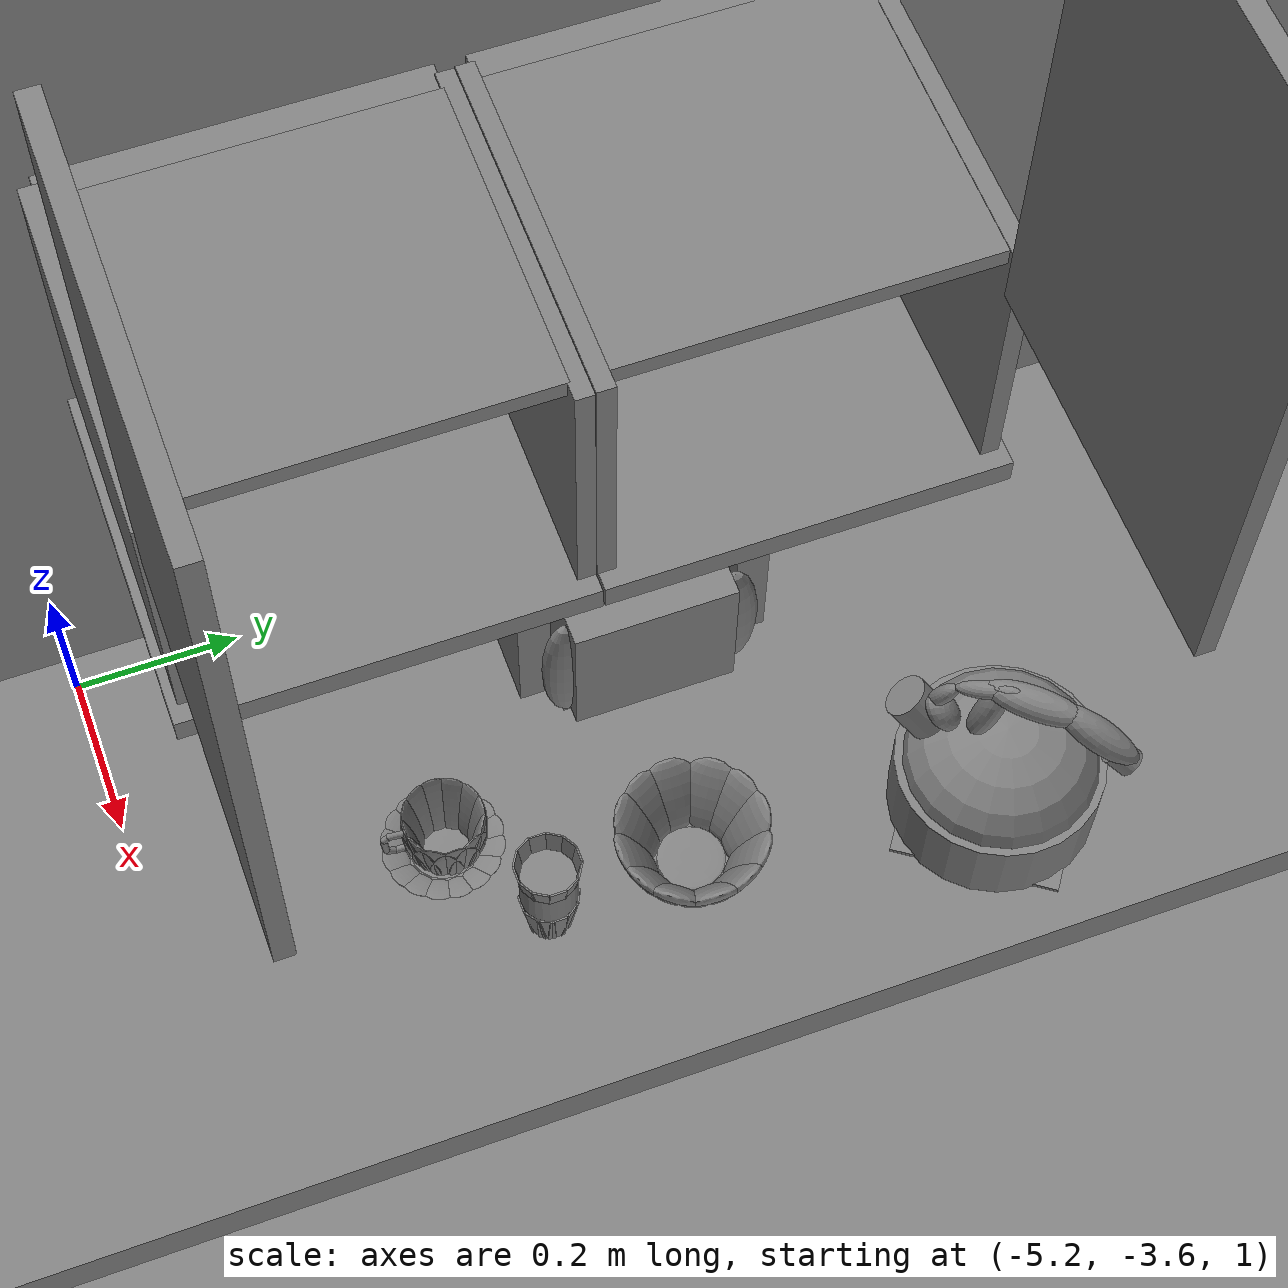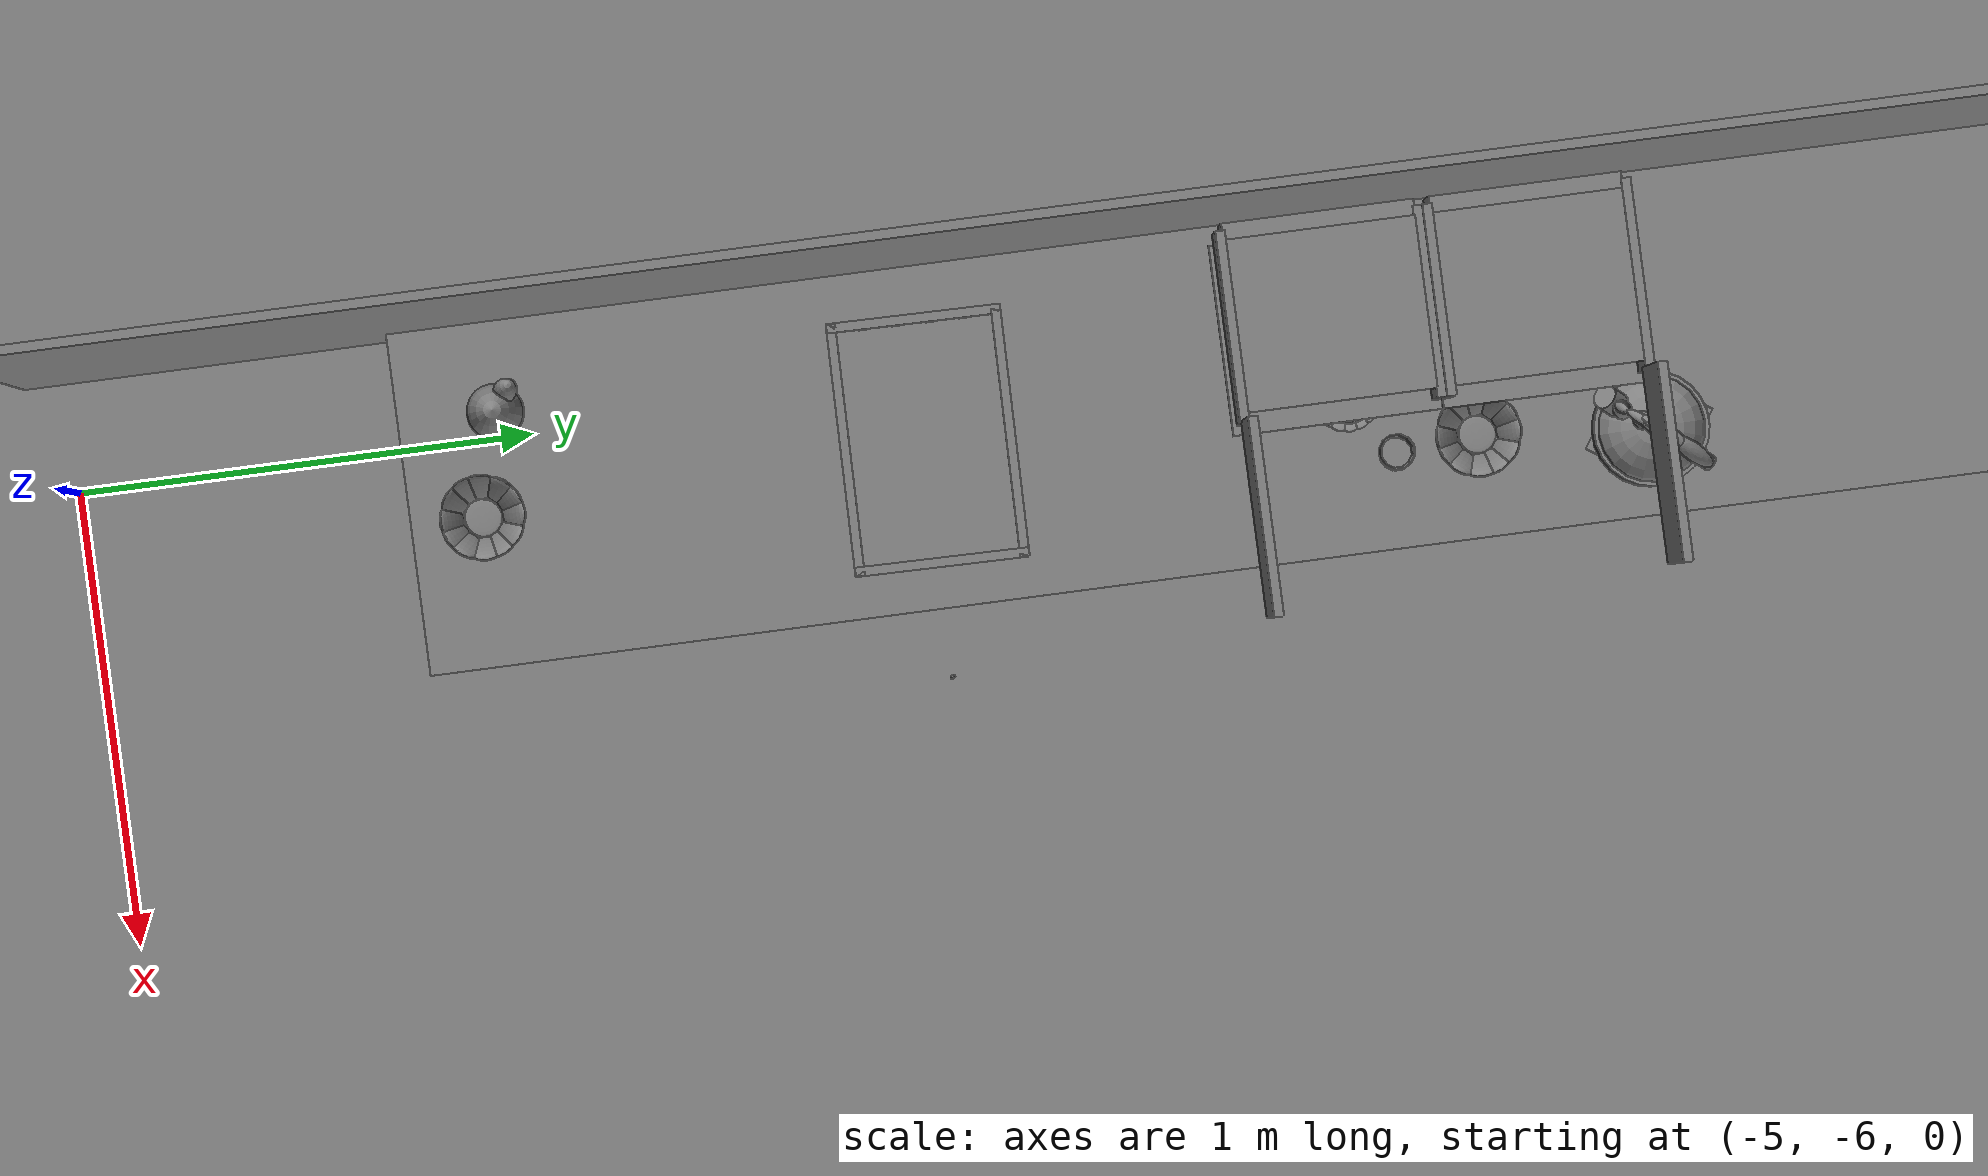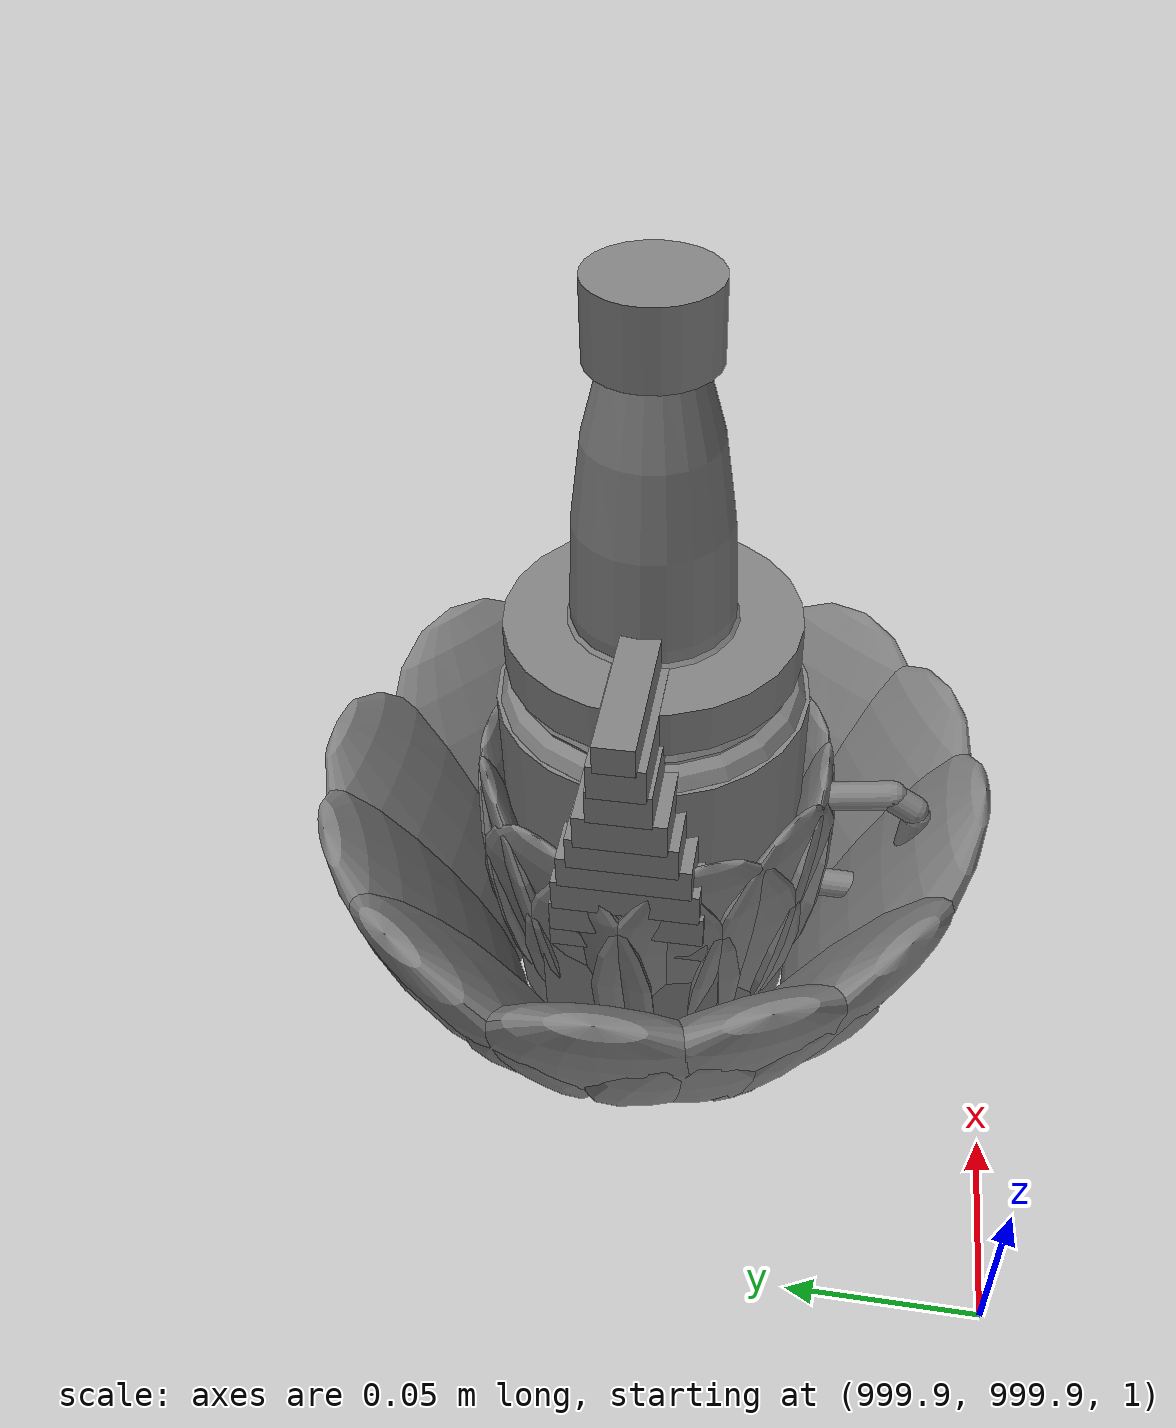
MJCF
<mujoco>
    <option gravity="0.000000000 0.000000000 -9.810000420" timestep="0.0049999999" integrator="implicitfast" density="9.8000002" viscosity="1.8000001e-05" noslip_iterations="10" iterations="100" sdf_iterations="50">
        <flag multiccd="disable"/>
    </option>
    <size memory="1000M"/>
    <compiler coordinate="local"/>
    <worldbody>
        <light cutoff="30" pos="0 1 1" dir="0 -1 -2"/>
        <light cutoff="30" pos="0 -1 1" dir="0 1 -2"/>
        <body pos="0.000000000 0.000000000 0.000000000" euler="0.000000000 0.000000000 0.000000000" name="Static Objcets_Static Objcets">
            <geom contype="1" conaffinity="1" density="1000" type="box" material="" rgba="0.500000000 0.500000000 0.500000000 1.000000000" solimp="0.899999976 0.949999988 0.001000000" friction="1.000000000 0.005000000 0.000100000" solref="0.020000000 1.000000000" margin="0" condim="3" group="0" pos="-5.189302921 -3.293644905 1.760152459" quat="0.707107067 0.707106471 0.000000000 0.000000000" size="0.025000000 0.159999996 0.200000003" name="Static Objcets_geom_988EC606_9CE6_4455_AD75_126E9105DDCF"/>
            <geom contype="1" conaffinity="1" density="1000" type="box" material="" rgba="0.500000000 0.500000000 0.500000000 1.000000000" solimp="0.899999976 0.949999988 0.001000000" friction="1.000000000 0.005000000 0.000100000" solref="0.020000000 1.000000000" margin="0" condim="3" group="0" pos="-4.999745846 -3.497932911 1.764780521" quat="0.707107067 0.707106471 0.000000000 0.000000000" size="0.200000003 0.159999996 0.010000000" name="Static Objcets_geom_621AEC19_6934_4DCD_8CF8_92520D5E41A5"/>
            <geom contype="1" conaffinity="1" density="1000" type="box" material="" rgba="0.500000000 0.500000000 0.500000000 1.000000000" solimp="0.899999976 0.949999988 0.001000000" friction="1.000000000 0.005000000 0.000100000" solref="0.020000000 1.000000000" margin="0" condim="3" group="0" pos="-4.979488373 -3.297635794 1.591412544" quat="0.707106829 0.707106709 0.000000000 0.000000000" size="0.200000003 0.015000000 0.219999999" name="Static Objcets_geom_B1B38490_DCCB_4912_B162_52A9C5FDA414"/>
            <geom contype="1" conaffinity="1" density="1000" type="box" material="" rgba="0.500000000 0.500000000 0.500000000 1.000000000" solimp="0.899999976 0.949999988 0.001000000" friction="1.000000000 0.005000000 0.000100000" solref="0.020000000 1.000000000" margin="0" condim="3" group="0" pos="-4.999745846 -3.087441683 1.763863802" quat="0.707107067 0.707106471 0.000000000 0.000000000" size="0.200000003 0.159999996 0.010000000" name="Static Objcets_geom_B393553F_F994_4DEC_BC99_1019E9FF38A8"/>
            <geom contype="1" conaffinity="1" density="1000" type="box" material="" rgba="0.500000000 0.500000000 0.500000000 1.000000000" solimp="0.899999976 0.949999988 0.001000000" friction="1.000000000 0.005000000 0.000100000" solref="0.020000000 1.000000000" margin="0" condim="3" group="0" pos="-5.000125408 -3.294431210 1.913951039" quat="0.707107067 0.707106471 0.000000000 0.000000000" size="0.180000007 0.010000000 0.200000003" name="Static Objcets_geom_1F99D7B4_4A3B_466B_A346_89608051F26C"/>
            <geom contype="1" conaffinity="1" density="1000" type="box" material="" rgba="0.500000000 0.500000000 0.500000000 1.000000000" solimp="0.899999976 0.949999988 0.001000000" friction="1.000000000 0.005000000 0.000100000" solref="0.020000000 1.000000000" margin="0" condim="3" group="0" pos="-4.873187065 -2.461376429 0.977675021" quat="0.707107067 0.707106471 0.000000000 0.000000000" size="0.370000005 0.029999999 2.799999952" name="Static Objcets_geom_BAC30788_EB73_40E6_9FEB_54CF23DEDB12"/>
            <geom contype="1" conaffinity="1" density="1000" type="box" material="" rgba="0.500000000 0.500000000 0.500000000 1.000000000" solimp="0.899999976 0.949999988 0.001000000" friction="1.000000000 0.005000000 0.000100000" solref="0.020000000 1.000000000" margin="0" condim="3" group="0" pos="-5.244853973 -2.375543594 1.820221663" quat="0.707107008 0.707106531 0.000000000 0.000000000" size="0.010000000 1.500000000 3.700000048" name="Static Objcets_geom_0E837666_7A92_4901_878C_0095ECA39692"/>
            <geom contype="1" conaffinity="1" density="1000" type="box" material="" rgba="0.500000000 0.500000000 0.500000000 1.000000000" solimp="0.899999976 0.949999988 0.001000000" friction="1.000000000 0.005000000 0.000100000" solref="0.020000000 1.000000000" margin="0" condim="3" group="0" pos="-0.720102787 0.222944975 -1.102830648" quat="0.000000954 1.000000000 0.000000000 0.000000000" size="8.000000000 8.000000000 0.010000000" name="Static Objcets_geom_D1538D0D_8282_4926_8DB3_EC2385A71027"/>
            <geom contype="1" conaffinity="1" density="1000" type="box" material="" rgba="0.500000000 0.500000000 0.500000000 1.000000000" solimp="0.899999976 0.949999988 0.001000000" friction="1.000000000 0.005000000 0.000100000" solref="0.020000000 1.000000000" margin="0" condim="3" group="0" pos="-4.999745846 -2.653569937 1.764779806" quat="0.707107067 0.707106471 0.000000000 0.000000000" size="0.200000003 0.159999996 0.010000000" name="Static Objcets_geom_DC40EEC1_0278_4F38_AAD8_A102B175EAEA"/>
            <geom contype="1" conaffinity="1" density="1000" type="box" material="" rgba="0.500000000 0.500000000 0.500000000 1.000000000" solimp="0.899999976 0.949999988 0.001000000" friction="1.000000000 0.005000000 0.000100000" solref="0.020000000 1.000000000" margin="0" condim="3" group="0" pos="-5.000125408 -2.861802340 1.913950682" quat="0.707107067 0.707106471 0.000000000 0.000000000" size="0.180000007 0.010000000 0.200000003" name="Static Objcets_geom_9D327266_9507_467B_B394_56C69BC239A4"/>
            <geom contype="1" conaffinity="1" density="1000" type="box" material="" rgba="0.500000000 0.500000000 0.500000000 1.000000000" solimp="0.899999976 0.949999988 0.001000000" friction="1.000000000 0.005000000 0.000100000" solref="0.020000000 1.000000000" margin="0" condim="3" group="0" pos="-5.189302921 -2.861564636 1.760152102" quat="0.707107067 0.707106471 0.000000000 0.000000000" size="0.025000000 0.159999996 0.200000003" name="Static Objcets_geom_CC9B4E68_BD0D_49C4_8AEB_1A179F09F49A"/>
            <geom contype="1" conaffinity="1" density="1000" type="box" material="" rgba="0.500000000 0.500000000 0.500000000 1.000000000" solimp="0.899999976 0.949999988 0.001000000" friction="1.000000000 0.005000000 0.000100000" solref="0.020000000 1.000000000" margin="0" condim="3" group="0" pos="-4.979488373 -2.855390549 1.591412187" quat="0.707106709 0.707106769 0.000000000 0.000000000" size="0.200000003 0.015000000 0.219999999" name="Static Objcets_geom_CCF045E2_6600_457B_A8EE_B31B6FC8F081"/>
            <geom contype="1" conaffinity="1" density="1000" type="box" material="" rgba="0.500000000 0.500000000 0.500000000 1.000000000" solimp="0.899999976 0.949999988 0.001000000" friction="1.000000000 0.005000000 0.000100000" solref="0.020000000 1.000000000" margin="0" condim="3" group="0" pos="-4.999745846 -3.066934109 1.765979409" quat="0.707107067 0.707106471 0.000000000 0.000000000" size="0.200000003 0.159999996 0.010000000" name="Static Objcets_geom_CDF17180_C1D3_4C58_8B24_470C578A5CB4"/>
        </body>
        <body pos="-4.367857456 -3.842065811 1.777402997" euler="99.923103333 -24.557859421 -119.334983826" mocap="true" name="spotlight3_SpotLight"/>
        <body pos="1000.000000000 1000.000000000 1.000000000" euler="0.000000000 0.000000000 0.000000000" name="openloong_gripper_2f85_fix_base_usda_jar_01">
            <geom contype="1" conaffinity="1" density="1000" type="box" material="" rgba="0.500000000 0.500000000 0.500000000 1.000000000" solimp="0.899999976 0.949999988 0.001000000" friction="1.000000000 0.005000000 0.000100000" solref="0.020000000 1.000000000" margin="0" condim="3" group="0" pos="0.000000000 0.000000000 0.006158113" quat="1.000000000 0.000000000 0.000000000 0.000000000" size="0.020000000 0.020000000 0.005000000" name="openloong_gripper_2f85_fix_base_usda_geom_860B8267_24BE_4708_8A00_1ADAA472A3F8"/>
            <geom contype="1" conaffinity="1" density="1000" type="cylinder" material="" rgba="0.500000000 0.500000000 0.500000000 1.000000000" solimp="0.899999976 0.949999988 0.001000000" friction="1.000000000 0.005000000 0.000100000" solref="0.020000000 1.000000000" margin="0" condim="3" group="0" pos="0.000000000 0.000000000 0.062744498" quat="1.000000000 0.000000000 0.000000000 0.000000000" size="0.041000001 0.052999999 1.000000000" name="openloong_gripper_2f85_fix_base_usda_geom_CF5AEDEA_7C81_49F7_9EC9_E2181CF2BC49"/>
            <geom contype="1" conaffinity="1" density="1000" type="ellipsoid" material="" rgba="0.500000000 0.500000000 0.500000000 1.000000000" solimp="0.899999976 0.949999988 0.001000000" friction="1.000000000 0.005000000 0.000100000" solref="0.020000000 1.000000000" margin="0" condim="3" group="0" pos="0.000000000 0.000000000 0.122252703" quat="1.000000000 0.000000000 0.000000000 0.000000000" size="0.035999998 0.035999998 0.010000000" name="openloong_gripper_2f85_fix_base_usda_geom_F7F58928_67B1_4FD2_AFFC_E9AA04ECEA83"/>
            <geom contype="1" conaffinity="1" density="1000" type="cylinder" material="" rgba="0.500000000 0.500000000 0.500000000 1.000000000" solimp="0.899999976 0.949999988 0.001000000" friction="1.000000000 0.005000000 0.000100000" solref="0.020000000 1.000000000" margin="0" condim="3" group="0" pos="0.000000000 0.000000000 0.015747190" quat="1.000000000 0.000000000 0.000000000 0.000000000" size="0.035000000 0.010000000 1.000000000" name="openloong_gripper_2f85_fix_base_usda_geom_7191F321_4D4C_41A3_8559_BC098DA21969"/>
            <geom contype="1" conaffinity="1" density="1000" type="ellipsoid" material="" rgba="0.500000000 0.500000000 0.500000000 1.000000000" solimp="0.899999976 0.949999988 0.001000000" friction="1.000000000 0.005000000 0.000100000" solref="0.020000000 1.000000000" margin="0" condim="3" group="0" pos="0.000000000 0.000000000 0.115815401" quat="1.000000000 0.000000000 0.000000000 0.000000000" size="0.039999999 0.039999999 0.010000000" name="openloong_gripper_2f85_fix_base_usda_geom_E4DE0641_933A_4B36_9355_6C7F95E030CE"/>
            <geom contype="1" conaffinity="1" density="1000" type="cylinder" material="" rgba="0.500000000 0.500000000 0.500000000 1.000000000" solimp="0.899999976 0.949999988 0.001000000" friction="1.000000000 0.005000000 0.000100000" solref="0.020000000 1.000000000" margin="0" condim="3" group="0" pos="0.000000000 0.000000000 0.133183479" quat="1.000000000 0.000000000 0.000000000 0.000000000" size="0.037999999 0.006500000 1.000000000" name="openloong_gripper_2f85_fix_base_usda_geom_FB705F4E_9755_4DA2_B27D_5EF58A416F5A"/>
            <freejoint name="openloong_gripper_2f85_fix_base_usda_jar_01_joint"/>
            <site size="0.005000000 0.005000000 0.005000000" rgba="0.500000000 0.500000000 0.500000000 1.000000000" pos="0.000000000 0.000000000 0.000000000" quat="1.000000000 0.000000000 0.000000000 0.000000000" group="0" type="sphere" name="openloong_gripper_2f85_fix_base_usda_jar_01site"/>
        </body>
        <body pos="1000.000000000 1000.000000000 1.000000000" euler="0.000000000 0.000000000 0.000000000" name="openloong_gripper_2f85_fix_base_usda_salt">
            <geom contype="1" conaffinity="1" density="1000" type="box" material="" rgba="0.500000000 0.500000000 0.500000000 1.000000000" solimp="0.899999976 0.949999988 0.001000000" friction="1.000000000 0.005000000 0.000100000" solref="0.020000000 1.000000000" margin="0" condim="3" group="0" pos="0.000305176 0.000000000 0.084862232" quat="1.000000000 0.000000000 0.000000000 0.000000000" size="0.048999999 0.018999999 0.005000000" name="openloong_gripper_2f85_fix_base_usda_geom_DB6C0F35_505B_4D2A_AACC_EA4618C598E0"/>
            <geom contype="1" conaffinity="1" density="1000" type="box" material="" rgba="0.500000000 0.500000000 0.500000000 1.000000000" solimp="0.899999976 0.949999988 0.001000000" friction="1.000000000 0.005000000 0.000100000" solref="0.020000000 1.000000000" margin="0" condim="3" group="0" pos="0.000305176 0.000000000 0.104564309" quat="1.000000000 0.000000000 0.000000000 0.000000000" size="0.052000001 0.014000000 0.005000000" name="openloong_gripper_2f85_fix_base_usda_geom_EA647089_BFFF_4EFC_BA4B_18F9A264A1B9"/>
            <geom contype="1" conaffinity="1" density="1000" type="box" material="" rgba="0.500000000 0.500000000 0.500000000 1.000000000" solimp="0.899999976 0.949999988 0.001000000" friction="1.000000000 0.005000000 0.000100000" solref="0.020000000 1.000000000" margin="0" condim="3" group="0" pos="0.000305176 0.000000000 0.114487171" quat="1.000000000 0.000000000 0.000000000 0.000000000" size="0.054000001 0.011500000 0.005000000" name="openloong_gripper_2f85_fix_base_usda_geom_8700A092_E014_4135_8E65_0B1FFC00B277"/>
            <geom contype="1" conaffinity="1" density="1000" type="box" material="" rgba="0.500000000 0.500000000 0.500000000 1.000000000" solimp="0.899999976 0.949999988 0.001000000" friction="1.000000000 0.005000000 0.000100000" solref="0.020000000 1.000000000" margin="0" condim="3" group="0" pos="0.000305176 0.000000000 0.075103164" quat="1.000000000 0.000000000 0.000000000 0.000000000" size="0.048000000 0.020000000 0.005000000" name="openloong_gripper_2f85_fix_base_usda_geom_41E15CAF_CA11_4BB8_9812_384E90D69B3E"/>
            <geom contype="1" conaffinity="1" density="1000" type="box" material="" rgba="0.500000000 0.500000000 0.500000000 1.000000000" solimp="0.899999976 0.949999988 0.001000000" friction="1.000000000 0.005000000 0.000100000" solref="0.020000000 1.000000000" margin="0" condim="3" group="0" pos="0.000305176 0.000000000 0.134892464" quat="1.000000000 0.000000000 0.000000000 0.000000000" size="0.057000000 0.007000000 0.005000000" name="openloong_gripper_2f85_fix_base_usda_geom_B39A6F22_9A89_4BF0_AB07_BE28B7EA97CD"/>
            <geom contype="1" conaffinity="1" density="1000" type="box" material="" rgba="0.500000000 0.500000000 0.500000000 1.000000000" solimp="0.899999976 0.949999988 0.001000000" friction="1.000000000 0.005000000 0.000100000" solref="0.020000000 1.000000000" margin="0" condim="3" group="0" pos="0.000305176 0.000000000 0.094920278" quat="1.000000000 0.000000000 0.000000000 0.000000000" size="0.050000001 0.017000001 0.005000000" name="openloong_gripper_2f85_fix_base_usda_geom_B57BFE12_D799_41F3_9FC0_5E230E47EE26"/>
            <geom contype="1" conaffinity="1" density="1000" type="box" material="" rgba="0.500000000 0.500000000 0.500000000 1.000000000" solimp="0.899999976 0.949999988 0.001000000" friction="1.000000000 0.005000000 0.000100000" solref="0.020000000 1.000000000" margin="0" condim="3" group="0" pos="0.000305176 0.000000000 0.065204859" quat="1.000000000 0.000000000 0.000000000 0.000000000" size="0.045000002 0.021000000 0.005000000" name="openloong_gripper_2f85_fix_base_usda_geom_CAEEE31E_6862_40E1_909D_B79A7BEC9C18"/>
            <geom contype="1" conaffinity="1" density="1000" type="box" material="" rgba="0.500000000 0.500000000 0.500000000 1.000000000" solimp="0.899999976 0.949999988 0.001000000" friction="1.000000000 0.005000000 0.000100000" solref="0.020000000 1.000000000" margin="0" condim="3" group="0" pos="0.000305176 0.000000000 0.144135714" quat="1.000000000 0.000000000 0.000000000 0.000000000" size="0.059000000 0.005000000 0.004000000" name="openloong_gripper_2f85_fix_base_usda_geom_64B60331_D931_43AB_A3D2_47001B5E7867"/>
            <geom contype="1" conaffinity="1" density="1000" type="box" material="" rgba="0.500000000 0.500000000 0.500000000 1.000000000" solimp="0.899999976 0.949999988 0.001000000" friction="1.000000000 0.005000000 0.000100000" solref="0.020000000 1.000000000" margin="0" condim="3" group="0" pos="0.000000000 0.000000000 0.031593561" quat="1.000000000 0.000000000 0.000000000 0.000000000" size="0.041999999 0.024000000 0.029999999" name="openloong_gripper_2f85_fix_base_usda_geom_CB6A3F90_D26F_49A1_9D1E_9FAF0CB12BB5"/>
            <geom contype="1" conaffinity="1" density="1000" type="box" material="" rgba="0.500000000 0.500000000 0.500000000 1.000000000" solimp="0.899999976 0.949999988 0.001000000" friction="1.000000000 0.005000000 0.000100000" solref="0.020000000 1.000000000" margin="0" condim="3" group="0" pos="0.000305176 0.000000000 0.124608755" quat="1.000000000 0.000000000 0.000000000 0.000000000" size="0.055000000 0.008000000 0.005000000" name="openloong_gripper_2f85_fix_base_usda_geom_19DCBA93_E1AB_4E62_BD61_DB25AEFBFF75"/>
            <freejoint name="openloong_gripper_2f85_fix_base_usda_salt_joint"/>
            <site size="0.005000000 0.005000000 0.005000000" rgba="0.500000000 0.500000000 0.500000000 1.000000000" pos="0.000000000 0.000000000 0.000000000" quat="1.000000000 0.000000000 0.000000000 0.000000000" group="0" type="sphere" name="openloong_gripper_2f85_fix_base_usda_saltsite"/>
        </body>
        <body pos="1000.000000000 1000.000000000 1.000000000" euler="0.000000000 0.000000000 0.000000000" name="openloong_gripper_2f85_fix_base_usda_bow_yellow_kps">
            <geom contype="1" conaffinity="1" density="1000" type="ellipsoid" material="" rgba="0.500000000 0.500000000 0.500000000 1.000000000" solimp="0.899999976 0.949999988 0.001000000" friction="1.000000000 0.005000000 0.000100000" solref="0.020000000 1.000000000" margin="0" condim="3" group="0" pos="-0.052185059 0.040283203 0.044118762" quat="0.919264615 -0.076883033 -0.225593656 -0.313287765" size="0.010000000 0.039999999 0.052000001" name="openloong_gripper_2f85_fix_base_usda_geom_77FA045A_B253_47C7_90A2_306E40801968"/>
            <geom contype="1" conaffinity="1" density="1000" type="ellipsoid" material="" rgba="0.500000000 0.500000000 0.500000000 1.000000000" solimp="0.899999976 0.949999988 0.001000000" friction="1.000000000 0.005000000 0.000100000" solref="0.020000000 1.000000000" margin="0" condim="3" group="0" pos="-0.000061035 0.065979004 0.044118762" quat="0.687598765 -0.168314874 -0.168741167 -0.685860336" size="0.010000000 0.039999999 0.052000001" name="openloong_gripper_2f85_fix_base_usda_geom_D6431670_D111_434E_89D5_E545F35FD6D0"/>
            <geom contype="1" conaffinity="1" density="1000" type="box" material="" rgba="0.500000000 0.500000000 0.500000000 1.000000000" solimp="0.899999976 0.949999988 0.001000000" friction="1.000000000 0.005000000 0.000100000" solref="0.020000000 1.000000000" margin="0" condim="3" group="0" pos="0.000061035 0.000000000 -0.002001643" quat="1.000000000 0.000000000 0.000000000 0.000000000" size="0.029999999 0.029999999 0.002000000" name="openloong_gripper_2f85_fix_base_usda_geom_BAD18E83_3D6A_470A_A620_AF17DAE9D6D6"/>
            <geom contype="1" conaffinity="1" density="1000" type="ellipsoid" material="" rgba="0.500000000 0.500000000 0.500000000 1.000000000" solimp="0.899999976 0.949999988 0.001000000" friction="1.000000000 0.005000000 0.000100000" solref="0.020000000 1.000000000" margin="0" condim="3" group="0" pos="0.029418945 -0.059082031 0.044118762" quat="0.825555861 0.125530601 0.202597082 -0.511521280" size="0.010000000 0.039999999 0.052000001" name="openloong_gripper_2f85_fix_base_usda_geom_782877C4_488F_4360_B429_0C7EA1A81C0E"/>
            <geom contype="1" conaffinity="1" density="1000" type="ellipsoid" material="" rgba="0.500000000 0.500000000 0.500000000 1.000000000" solimp="0.899999976 0.949999988 0.001000000" friction="1.000000000 0.005000000 0.000100000" solref="0.020000000 1.000000000" margin="0" condim="3" group="0" pos="0.000244141 -0.065979004 0.044118762" quat="0.687598765 0.168314651 0.168741375 -0.685860336" size="0.010000000 0.039999999 0.052000001" name="openloong_gripper_2f85_fix_base_usda_geom_946211FF_D818_4955_94D5_F49D9A816CBF"/>
            <geom contype="1" conaffinity="1" density="1000" type="ellipsoid" material="" rgba="0.500000000 0.500000000 0.500000000 1.000000000" solimp="0.899999976 0.949999988 0.001000000" friction="1.000000000 0.005000000 0.000100000" solref="0.020000000 1.000000000" margin="0" condim="3" group="0" pos="0.000061035 0.000000000 0.000446677" quat="1.000000000 0.000000000 0.000000000 0.000000000" size="0.039999999 0.039999999 0.002000000" name="openloong_gripper_2f85_fix_base_usda_geom_4E883A05_6011_4110_8012_4B25EDABDB90"/>
            <geom contype="1" conaffinity="1" density="1000" type="ellipsoid" material="" rgba="0.500000000 0.500000000 0.500000000 1.000000000" solimp="0.899999976 0.949999988 0.001000000" friction="1.000000000 0.005000000 0.000100000" solref="0.020000000 1.000000000" margin="0" condim="3" group="0" pos="0.059082031 0.029541016 0.044118762" quat="0.223252773 -0.231952220 -0.054787423 -0.945174456" size="0.010000000 0.039999999 0.052000001" name="openloong_gripper_2f85_fix_base_usda_geom_3A83C6A6_BC02_432B_B86A_515FBD4C9BAA"/>
            <geom contype="1" conaffinity="1" density="1000" type="ellipsoid" material="" rgba="0.500000000 0.500000000 0.500000000 1.000000000" solimp="0.899999976 0.949999988 0.001000000" friction="1.000000000 0.005000000 0.000100000" solref="0.020000000 1.000000000" margin="0" condim="3" group="0" pos="0.000061035 0.000000000 0.007335305" quat="1.000000000 0.000000000 0.000000000 0.000000000" size="0.039999999 0.039999999 0.002000000" name="openloong_gripper_2f85_fix_base_usda_geom_B4566490_E6AE_432D_83E9_14F36B1BEB68"/>
            <geom contype="1" conaffinity="1" density="1000" type="ellipsoid" material="" rgba="0.500000000 0.500000000 0.500000000 1.000000000" solimp="0.899999976 0.949999988 0.001000000" friction="1.000000000 0.005000000 0.000100000" solref="0.020000000 1.000000000" margin="0" condim="3" group="0" pos="-0.029296875 0.059082031 0.044118762" quat="0.825555861 -0.125530809 -0.202596918 -0.511521280" size="0.010000000 0.039999999 0.052000001" name="openloong_gripper_2f85_fix_base_usda_geom_93CBE0F8_0370_4684_A7CD_6317B29C2DA7"/>
            <geom contype="1" conaffinity="1" density="1000" type="ellipsoid" material="" rgba="0.500000000 0.500000000 0.500000000 1.000000000" solimp="0.899999976 0.949999988 0.001000000" friction="1.000000000 0.005000000 0.000100000" solref="0.020000000 1.000000000" margin="0" condim="3" group="0" pos="0.040222168 0.052368164 0.044118762" quat="0.429593176 -0.213750049 -0.105424821 -0.871002972" size="0.010000000 0.039999999 0.052000001" name="openloong_gripper_2f85_fix_base_usda_geom_D73D14B2_DFCB_4660_8F7B_AE5CC69C56F0"/>
            <geom contype="1" conaffinity="1" density="1000" type="ellipsoid" material="" rgba="0.500000000 0.500000000 0.500000000 1.000000000" solimp="0.899999976 0.949999988 0.001000000" friction="1.000000000 0.005000000 0.000100000" solref="0.020000000 1.000000000" margin="0" condim="3" group="0" pos="0.066040039 0.000000000 0.044118762" quat="0.971183062 -0.000000156 0.238334835 0.000000030" size="0.010000000 0.039999999 0.052000001" name="openloong_gripper_2f85_fix_base_usda_geom_5F646901_C9EF_46A7_A7AF_2BB7B69D5AA9"/>
            <geom contype="1" conaffinity="1" density="1000" type="ellipsoid" material="" rgba="0.500000000 0.500000000 0.500000000 1.000000000" solimp="0.899999976 0.949999988 0.001000000" friction="1.000000000 0.005000000 0.000100000" solref="0.020000000 1.000000000" margin="0" condim="3" group="0" pos="0.052307129 -0.040283203 0.044118762" quat="0.919264674 0.076882750 0.225593731 -0.313287705" size="0.010000000 0.039999999 0.052000001" name="openloong_gripper_2f85_fix_base_usda_geom_6A07ECF2_8507_4C7F_A112_BF74F47AD72A"/>
            <geom contype="1" conaffinity="1" density="1000" type="ellipsoid" material="" rgba="0.500000000 0.500000000 0.500000000 1.000000000" solimp="0.899999976 0.949999988 0.001000000" friction="1.000000000 0.005000000 0.000100000" solref="0.020000000 1.000000000" margin="0" condim="3" group="0" pos="-0.065917969 0.000000000 0.044118762" quat="0.971183062 -0.000000142 -0.238334835 0.000000030" size="0.010000000 0.039999999 0.052000001" name="openloong_gripper_2f85_fix_base_usda_geom_6530ADFC_796F_46E2_B9A9_DDAC8E6527E6"/>
            <geom contype="1" conaffinity="1" density="1000" type="ellipsoid" material="" rgba="0.500000000 0.500000000 0.500000000 1.000000000" solimp="0.899999976 0.949999988 0.001000000" friction="1.000000000 0.005000000 0.000100000" solref="0.020000000 1.000000000" margin="0" condim="3" group="0" pos="-0.058898926 -0.029541016 0.044118762" quat="0.223252758 0.231952101 0.054787733 -0.945174575" size="0.010000000 0.039999999 0.052000001" name="openloong_gripper_2f85_fix_base_usda_geom_F7433BB5_8051_46EC_B751_5E58EAFE2D2E"/>
            <geom contype="1" conaffinity="1" density="1000" type="ellipsoid" material="" rgba="0.500000000 0.500000000 0.500000000 1.000000000" solimp="0.899999976 0.949999988 0.001000000" friction="1.000000000 0.005000000 0.000100000" solref="0.020000000 1.000000000" margin="0" condim="3" group="0" pos="-0.040100098 -0.052368164 0.044118762" quat="0.429593235 0.213749886 0.105425082 -0.871003032" size="0.010000000 0.039999999 0.052000001" name="openloong_gripper_2f85_fix_base_usda_geom_8AE6C3B7_1FD8_4147_BB04_D7ACA3292964"/>
            <freejoint name="openloong_gripper_2f85_fix_base_usda_bow_yellow_kps_joint"/>
            <site size="0.005000000 0.005000000 0.005000000" rgba="0.500000000 0.500000000 0.500000000 1.000000000" pos="0.000000000 0.000000000 0.000000000" quat="0.999961913 0.008726534 0.000000000 0.000000000" group="0" type="sphere" name="openloong_gripper_2f85_fix_base_usda_bow_yellow_kps"/>
        </body>
        <body pos="-3.976314068 -3.723570824 1.743447661" euler="70.533096313 -75.089950562 3.498340130" mocap="true" name="spotlight2_SpotLight"/>
        <body pos="-4.032154560 -3.710449696 1.833721638" euler="179.405258179 -14.784882545 169.788162231" mocap="true" name="spotlight5_SpotLight"/>
        <body pos="1000.000000000 1000.000000000 1.000000000" euler="0.000000000 0.000000000 0.000000000" name="openloong_gripper_2f85_fix_base_usda_coffeecup_white_kps">
            <geom contype="1" conaffinity="1" density="1000" type="capsule" material="" rgba="0.500000000 0.500000000 0.500000000 1.000000000" solimp="0.899999976 0.949999988 0.001000000" friction="1.000000000 0.005000000 0.000100000" solref="0.020000000 1.000000000" margin="0" condim="3" group="0" pos="-0.000854492 -0.065795898 0.050029993" quat="0.343559504 -0.613204718 0.626912475 0.336047262" size="0.004000000 0.005000000 1.000000000" name="openloong_gripper_2f85_fix_base_usda_geom_F084BE43_CDB4_43DE_B2E2_B0B6F0641075"/>
            <geom contype="1" conaffinity="1" density="1000" type="ellipsoid" material="" rgba="0.500000000 0.500000000 0.500000000 1.000000000" solimp="0.899999976 0.949999988 0.001000000" friction="1.000000000 0.005000000 0.000100000" solref="0.020000000 1.000000000" margin="0" condim="3" group="0" pos="-0.000793457 -0.038452148 0.048040152" quat="0.711656272 0.066323131 -0.067805752 0.696095467" size="0.005000000 0.029999999 0.048999999" name="openloong_gripper_2f85_fix_base_usda_geom_BD075B0C_7721_4CB2_9169_3AA3087AF3D1"/>
            <geom contype="1" conaffinity="1" density="1000" type="ellipsoid" material="" rgba="0.500000000 0.500000000 0.500000000 1.000000000" solimp="0.899999976 0.949999988 0.001000000" friction="1.000000000 0.005000000 0.000100000" solref="0.020000000 1.000000000" margin="0" condim="3" group="0" pos="0.037719727 -0.001892090 0.048040152" quat="0.995387912 0.001371633 0.094835162 -0.014391154" size="0.005000000 0.029999999 0.048999999" name="openloong_gripper_2f85_fix_base_usda_geom_C7E0B1D3_6FF2_4826_94E9_5AB808DF5AD9"/>
            <geom contype="1" conaffinity="1" density="1000" type="ellipsoid" material="" rgba="0.500000000 0.500000000 0.500000000 1.000000000" solimp="0.899999976 0.949999988 0.001000000" friction="1.000000000 0.005000000 0.000100000" solref="0.020000000 1.000000000" margin="0" condim="3" group="0" pos="0.033996582 0.015502930 0.048040152" quat="0.970659733 -0.021051638 0.092478797 0.220962167" size="0.005000000 0.029999999 0.048999999" name="openloong_gripper_2f85_fix_base_usda_geom_4F27F86C_89EB_4499_8A53_819FDA6A6D34"/>
            <geom contype="1" conaffinity="1" density="1000" type="box" material="" rgba="0.500000000 0.500000000 0.500000000 1.000000000" solimp="0.899999976 0.949999988 0.001000000" friction="1.000000000 0.005000000 0.000100000" solref="0.020000000 1.000000000" margin="0" condim="3" group="0" pos="0.000793457 -0.000183105 0.000156164" quat="0.714879215 0.000000000 0.000000000 0.699247897" size="0.020000000 0.020000000 0.002000000" name="openloong_gripper_2f85_fix_base_usda_geom_DF1455EB_D2D4_4D50_B6E4_B79CDC73AED2"/>
            <geom contype="1" conaffinity="1" density="1000" type="ellipsoid" material="" rgba="0.500000000 0.500000000 0.500000000 1.000000000" solimp="0.899999976 0.949999988 0.001000000" friction="1.000000000 0.005000000 0.000100000" solref="0.020000000 1.000000000" margin="0" condim="3" group="0" pos="-0.019409180 -0.033081055 0.048040152" quat="0.866879702 0.046630561 -0.082595348 0.489411235" size="0.005000000 0.029999999 0.048999999" name="openloong_gripper_2f85_fix_base_usda_geom_1B7D3868_882D_4FBD_8B18_44E4C56B2A8A"/>
            <geom contype="1" conaffinity="1" density="1000" type="ellipsoid" material="" rgba="0.500000000 0.500000000 0.500000000 1.000000000" solimp="0.899999976 0.949999988 0.001000000" friction="1.000000000 0.005000000 0.000100000" solref="0.020000000 1.000000000" margin="0" condim="3" group="0" pos="-0.016052246 0.033264160 0.048040152" quat="0.840792537 -0.050782297 -0.080109790 -0.532983541" size="0.005000000 0.029999999 0.048999999" name="openloong_gripper_2f85_fix_base_usda_geom_17BE4854_5F7F_4845_B7AC_FB0437831E06"/>
            <geom contype="1" conaffinity="1" density="1000" type="capsule" material="" rgba="0.500000000 0.500000000 0.500000000 1.000000000" solimp="0.899999976 0.949999988 0.001000000" friction="1.000000000 0.005000000 0.000100000" solref="0.020000000 1.000000000" margin="0" condim="3" group="0" pos="-0.000549316 -0.053527832 0.046825886" quat="0.505496025 -0.494442940 0.505495846 0.494442940" size="0.004000000 0.005000000 1.000000000" name="openloong_gripper_2f85_fix_base_usda_geom_16C4FE19_D88F_4FF8_A51A_FEBCA78D8F62"/>
            <geom contype="1" conaffinity="1" density="1000" type="ellipsoid" material="" rgba="0.500000000 0.500000000 0.500000000 1.000000000" solimp="0.899999976 0.949999988 0.001000000" friction="1.000000000 0.005000000 0.000100000" solref="0.020000000 1.000000000" margin="0" condim="3" group="0" pos="-0.032104492 0.018920898 0.048040152" quat="0.958129764 -0.025742561 -0.091288343 -0.270168930" size="0.005000000 0.029999999 0.048999999" name="openloong_gripper_2f85_fix_base_usda_geom_71636DFC_C553_4D57_8AC7_0BC867706D20"/>
            <geom contype="1" conaffinity="1" density="1000" type="ellipsoid" material="" rgba="0.500000000 0.500000000 0.500000000 1.000000000" solimp="0.899999976 0.949999988 0.001000000" friction="1.000000000 0.005000000 0.000100000" solref="0.020000000 1.000000000" margin="0" condim="3" group="0" pos="-0.037597656 0.000305176 0.048040152" quat="0.995387554 -0.001371440 -0.094839431 -0.014389008" size="0.005000000 0.029999999 0.048999999" name="openloong_gripper_2f85_fix_base_usda_geom_097AC258_AF35_4CDE_8DAE_2F1CE7E415DB"/>
            <geom contype="1" conaffinity="1" density="1000" type="capsule" material="" rgba="0.500000000 0.500000000 0.500000000 1.000000000" solimp="0.899999976 0.949999988 0.001000000" friction="1.000000000 0.005000000 0.000100000" solref="0.020000000 1.000000000" margin="0" condim="3" group="0" pos="-0.000366211 -0.043762207 0.044118762" quat="0.260488123 -0.651174724 0.665731549 0.254792154" size="0.004000000 0.003000000 1.000000000" name="openloong_gripper_2f85_fix_base_usda_geom_48AF57D0_4885_40CC_8488_8F4C3CAABAF3"/>
            <geom contype="1" conaffinity="1" density="1000" type="capsule" material="" rgba="0.500000000 0.500000000 0.500000000 1.000000000" solimp="0.899999976 0.949999988 0.001000000" friction="1.000000000 0.005000000 0.000100000" solref="0.020000000 1.000000000" margin="0" condim="3" group="0" pos="-0.000915527 -0.068542480 0.082936406" quat="0.624995589 -0.339446366 0.347034454 0.611329615" size="0.004000000 0.004000000 1.000000000" name="openloong_gripper_2f85_fix_base_usda_geom_7886D9CA_68D1_4144_8D7F_9B5674CC59FF"/>
            <geom contype="1" conaffinity="1" density="1000" type="ellipsoid" material="" rgba="0.500000000 0.500000000 0.500000000 1.000000000" solimp="0.899999976 0.949999988 0.001000000" friction="1.000000000 0.005000000 0.000100000" solref="0.020000000 1.000000000" margin="0" condim="3" group="0" pos="0.016113281 -0.034851074 0.048040152" quat="0.840793252 0.050779939 0.080106191 -0.532983422" size="0.005000000 0.029999999 0.048999999" name="openloong_gripper_2f85_fix_base_usda_geom_285815B3_CDEC_484E_94EE_7943D78B06C7"/>
            <geom contype="1" conaffinity="1" density="1000" type="ellipsoid" material="" rgba="0.500000000 0.500000000 0.500000000 1.000000000" solimp="0.899999976 0.949999988 0.001000000" friction="1.000000000 0.005000000 0.000100000" solref="0.020000000 1.000000000" margin="0" condim="3" group="0" pos="0.000854492 0.036865234 0.048040152" quat="0.711656570 -0.066320375 0.067802906 0.696095705" size="0.005000000 0.029999999 0.048999999" name="openloong_gripper_2f85_fix_base_usda_geom_E4DF4621_0A37_4FA1_A733_8792BFB73447"/>
            <geom contype="1" conaffinity="1" density="1000" type="ellipsoid" material="" rgba="0.500000000 0.500000000 0.500000000 1.000000000" solimp="0.899999976 0.949999988 0.001000000" friction="1.000000000 0.005000000 0.000100000" solref="0.020000000 1.000000000" margin="0" condim="3" group="0" pos="-0.033935547 -0.017089844 0.048040152" quat="0.970659137 0.021052625 -0.092483103 0.220962465" size="0.005000000 0.029999999 0.048999999" name="openloong_gripper_2f85_fix_base_usda_geom_B017A086_4089_418E_8BA9_D0D60B377DF4"/>
            <geom contype="1" conaffinity="1" density="1000" type="ellipsoid" material="" rgba="0.500000000 0.500000000 0.500000000 1.000000000" solimp="0.899999976 0.949999988 0.001000000" friction="1.000000000 0.005000000 0.000100000" solref="0.020000000 1.000000000" margin="0" condim="3" group="0" pos="0.019531250 0.031494141 0.048040152" quat="0.866880119 -0.046628602 0.082591817 0.489411235" size="0.005000000 0.029999999 0.048999999" name="openloong_gripper_2f85_fix_base_usda_geom_13984026_6A83_4CEF_B1EC_93B85C11A54F"/>
            <geom contype="1" conaffinity="1" density="1000" type="ellipsoid" material="" rgba="0.500000000 0.500000000 0.500000000 1.000000000" solimp="0.899999976 0.949999988 0.001000000" friction="1.000000000 0.005000000 0.000100000" solref="0.020000000 1.000000000" margin="0" condim="3" group="0" pos="0.032165527 -0.020507812 0.048040152" quat="0.958128154 0.025740955 0.091285400 -0.270175666" size="0.005000000 0.029999999 0.048999999" name="openloong_gripper_2f85_fix_base_usda_geom_3734CA42_1930_4EB9_9865_3F4F8072D449"/>
            <geom contype="1" conaffinity="1" density="1000" type="capsule" material="" rgba="0.500000000 0.500000000 0.500000000 1.000000000" solimp="0.899999976 0.949999988 0.001000000" friction="1.000000000 0.005000000 0.000100000" solref="0.020000000 1.000000000" margin="0" condim="3" group="0" pos="-0.000610352 -0.056823730 0.083572865" quat="0.452654332 -0.541215360 0.553313971 0.442756712" size="0.004000000 0.009000000 1.000000000" name="openloong_gripper_2f85_fix_base_usda_geom_74348DA1_BC72_4137_91B9_95DADFC9D79D"/>
            <geom contype="1" conaffinity="1" density="1000" type="ellipsoid" material="" rgba="0.500000000 0.500000000 0.500000000 1.000000000" solimp="0.899999976 0.949999988 0.001000000" friction="1.000000000 0.005000000 0.000100000" solref="0.020000000 1.000000000" margin="0" condim="3" group="0" pos="0.000061035 -0.000183105 0.001848221" quat="0.714879215 0.000000000 0.000000000 0.699247897" size="0.029999999 0.029999999 0.001000000" name="openloong_gripper_2f85_fix_base_usda_geom_8259A45C_CD1F_488B_8DA6_1B172485149D"/>
            <geom contype="1" conaffinity="1" density="1000" type="capsule" material="" rgba="0.500000000 0.500000000 0.500000000 1.000000000" solimp="0.899999976 0.949999988 0.001000000" friction="1.000000000 0.005000000 0.000100000" solref="0.020000000 1.000000000" margin="0" condim="3" group="0" pos="-0.000976562 -0.071838379 0.066101432" quat="0.031849027 -0.698553741 0.714169443 0.031152546" size="0.004000000 0.012000000 1.000000000" name="openloong_gripper_2f85_fix_base_usda_geom_C3E298BF_2CFB_4455_8D0B_B4E474952C93"/>
            <freejoint name="openloong_gripper_2f85_fix_base_usda_coffeecup_white_kps_joint"/>
            <site size="0.005000000 0.005000000 0.005000000" rgba="0.500000000 0.500000000 0.500000000 1.000000000" pos="0.000000000 0.000000000 0.000000000" quat="0.999961913 0.008726534 0.000000000 0.000000000" group="0" type="sphere" name="openloong_gripper_2f85_fix_base_usda_coffeecup_white_kps"/>
        </body>
        <body pos="1000.000000000 1000.000000000 1.000000000" euler="0.000000000 0.000000000 0.000000000" name="openloong_gripper_2f85_fix_base_usda_bottle_red">
            <geom contype="1" conaffinity="1" density="1000" type="ellipsoid" material="" rgba="0.500000000 0.500000000 0.500000000 1.000000000" solimp="0.899999976 0.949999988 0.001000000" friction="1.000000000 0.005000000 0.000100000" solref="0.020000000 1.000000000" margin="0" condim="3" group="0" pos="0.000000000 0.000000000 0.144284487" quat="1.000000000 0.000000000 0.000000000 0.000000000" size="0.021000000 0.021000000 0.079999998" name="openloong_gripper_2f85_fix_base_usda_geom_D4CB37FB_CA65_4406_B29E_891023BB37F7"/>
            <geom contype="1" conaffinity="1" density="1000" type="cylinder" material="" rgba="0.500000000 0.500000000 0.500000000 1.000000000" solimp="0.899999976 0.949999988 0.001000000" friction="1.000000000 0.005000000 0.000100000" solref="0.020000000 1.000000000" margin="0" condim="3" group="0" pos="0.000000000 0.000000000 0.220618963" quat="1.000000000 0.000000000 0.000000000 0.000000000" size="0.016000001 0.010000000 1.000000000" name="openloong_gripper_2f85_fix_base_usda_geom_668E4BB4_8DF8_4923_88CE_48C7305BC69F"/>
            <geom contype="1" conaffinity="1" density="1000" type="ellipsoid" material="" rgba="0.500000000 0.500000000 0.500000000 1.000000000" solimp="0.899999976 0.949999988 0.001000000" friction="1.000000000 0.005000000 0.000100000" solref="0.020000000 1.000000000" margin="0" condim="3" group="0" pos="0.000000000 0.000000000 0.118945479" quat="1.000000000 0.000000000 0.000000000 0.000000000" size="0.030999999 0.030999999 0.029999999" name="openloong_gripper_2f85_fix_base_usda_geom_1DE366F2_5FE8_4988_90ED_AEA282C68A37"/>
            <geom contype="1" conaffinity="1" density="1000" type="box" material="" rgba="0.500000000 0.500000000 0.500000000 1.000000000" solimp="0.899999976 0.949999988 0.001000000" friction="1.000000000 0.005000000 0.000100000" solref="0.020000000 1.000000000" margin="0" condim="3" group="0" pos="0.000000000 0.000000000 0.002189159" quat="1.000000000 0.000000000 0.000000000 0.000000000" size="0.020000000 0.020000000 0.003000000" name="openloong_gripper_2f85_fix_base_usda_geom_6650E0EE_0957_4CC9_87A4_04D933E9287A"/>
            <geom contype="1" conaffinity="1" density="1000" type="cylinder" material="" rgba="0.500000000 0.500000000 0.500000000 1.000000000" solimp="0.899999976 0.949999988 0.001000000" friction="1.000000000 0.005000000 0.000100000" solref="0.020000000 1.000000000" margin="0" condim="3" group="0" pos="0.000000000 -0.000366211 0.060884237" quat="1.000000000 0.000000000 0.000000000 0.000000000" size="0.030999999 0.057999998 1.000000000" name="openloong_gripper_2f85_fix_base_usda_geom_675BEE2E_EC7C_45B0_88C1_7A0782D2C417"/>
            <freejoint name="openloong_gripper_2f85_fix_base_usda_bottle_red_joint"/>
            <site size="0.005000000 0.005000000 0.005000000" rgba="0.500000000 0.500000000 0.500000000 1.000000000" pos="0.000000000 0.000000000 0.000000000" quat="0.999961913 0.008726535 0.000000000 0.000000000" group="0" type="sphere" name="openloong_gripper_2f85_fix_base_usda_bottle_redsite"/>
        </body>
        <body pos="-4.860558510 -4.149443150 1.004824519" euler="0.000000000 0.000000000 -90.691101074" name="openloong_gripper_2f85_fix_base_usda_Basket_Kitchen_01">
            <geom contype="1" conaffinity="1" density="1000" type="box" material="" rgba="0.500000000 0.500000000 0.500000000 1.000000000" solimp="0.899999976 0.949999988 0.001000000" friction="1.000000000 0.005000000 0.000100000" solref="0.020000000 1.000000000" margin="0" condim="3" group="0" pos="-0.175679624 -0.000001907 0.109079957" quat="0.707106948 0.000000000 0.000000000 0.707106292" size="0.268999994 0.010000000 0.010500000" name="openloong_gripper_2f85_fix_base_usda_geom_41BD7552_BF3F_4452_83F9_0FC872DA75DB"/>
            <geom contype="1" conaffinity="1" density="1000" type="box" material="" rgba="0.500000000 0.500000000 0.500000000 1.000000000" solimp="0.899999976 0.949999988 0.001000000" friction="1.000000000 0.005000000 0.000100000" solref="0.020000000 1.000000000" margin="0" condim="3" group="0" pos="-0.176020086 0.002991676 0.059861541" quat="0.707106948 0.000000000 0.000000000 0.707106292" size="0.009500000 0.009500000 0.039999999" name="openloong_gripper_2f85_fix_base_usda_geom_9BD30AED_BF82_4F96_BF4E_4D8130AE8D29"/>
            <geom contype="1" conaffinity="1" density="1000" type="box" material="" rgba="0.500000000 0.500000000 0.500000000 1.000000000" solimp="0.899999976 0.949999988 0.001000000" friction="1.000000000 0.005000000 0.000100000" solref="0.020000000 1.000000000" margin="0" condim="3" group="0" pos="0.176000476 0.002991199 0.059860587" quat="0.707106948 0.000000000 0.000000000 0.707106292" size="0.009500000 0.009500000 0.039999999" name="openloong_gripper_2f85_fix_base_usda_geom_0E22A666_E1EE_42C9_B8A8_5D52F0A5BE4E"/>
            <geom contype="1" conaffinity="1" density="1000" type="box" material="" rgba="0.500000000 0.500000000 0.500000000 1.000000000" solimp="0.899999976 0.949999988 0.001000000" friction="1.000000000 0.005000000 0.000100000" solref="0.020000000 1.000000000" margin="0" condim="3" group="0" pos="0.176003337 0.259475470 0.059859991" quat="0.707106948 0.000000000 0.000000000 0.707106292" size="0.009500000 0.009500000 0.039999999" name="openloong_gripper_2f85_fix_base_usda_geom_A60D6D44_4228_46A4_9E30_DE5D6C4377A8"/>
            <geom contype="1" conaffinity="1" density="1000" type="box" material="" rgba="0.500000000 0.500000000 0.500000000 1.000000000" solimp="0.899999976 0.949999988 0.001000000" friction="1.000000000 0.005000000 0.000100000" solref="0.020000000 1.000000000" margin="0" condim="3" group="0" pos="-0.176020086 -0.088696003 0.059861422" quat="0.707106948 0.000000000 0.000000000 0.707106292" size="0.009500000 0.009500000 0.039999999" name="openloong_gripper_2f85_fix_base_usda_geom_AB12ACD8_A796_4EEE_AA3B_AD825DFCFB16"/>
            <geom contype="1" conaffinity="1" density="1000" type="box" material="" rgba="0.500000000 0.500000000 0.500000000 1.000000000" solimp="0.899999976 0.949999988 0.001000000" friction="1.000000000 0.005000000 0.000100000" solref="0.020000000 1.000000000" margin="0" condim="3" group="0" pos="0.000000000 0.259647608 0.109079957" quat="0.707106948 0.000000000 0.000000000 0.707106292" size="0.010000000 0.185000002 0.010500000" name="openloong_gripper_2f85_fix_base_usda_geom_E7FE5095_3B13_4C30_9533_24BAA7A331C5"/>
            <geom contype="1" conaffinity="1" density="1000" type="box" material="" rgba="0.500000000 0.500000000 0.500000000 1.000000000" solimp="0.899999976 0.949999988 0.001000000" friction="1.000000000 0.005000000 0.000100000" solref="0.020000000 1.000000000" margin="0" condim="3" group="0" pos="0.176001906 -0.259545803 0.059860349" quat="0.707106948 0.000000000 0.000000000 0.707106292" size="0.009500000 0.009500000 0.039999999" name="openloong_gripper_2f85_fix_base_usda_geom_ED740956_9284_4D46_A12F_0E58387A6124"/>
            <geom contype="1" conaffinity="1" density="1000" type="box" material="" rgba="0.500000000 0.500000000 0.500000000 1.000000000" solimp="0.899999976 0.949999988 0.001000000" friction="1.000000000 0.005000000 0.000100000" solref="0.020000000 1.000000000" margin="0" condim="3" group="0" pos="0.036305428 -0.259545326 0.059860587" quat="0.707106948 0.000000000 0.000000000 0.707106292" size="0.009500000 0.009500000 0.039999999" name="openloong_gripper_2f85_fix_base_usda_geom_DCBDCF2D_FB78_4885_BB81_AE59156F8BB6"/>
            <geom contype="1" conaffinity="1" density="1000" type="box" material="" rgba="0.500000000 0.500000000 0.500000000 1.000000000" solimp="0.899999976 0.949999988 0.001000000" friction="1.000000000 0.005000000 0.000100000" solref="0.020000000 1.000000000" margin="0" condim="3" group="0" pos="0.000000119 -0.259647369 0.109079957" quat="0.707106948 0.000000000 0.000000000 0.707106292" size="0.010000000 0.185000002 0.010500000" name="openloong_gripper_2f85_fix_base_usda_geom_62496C8E_3311_43A6_B4C4_999430433F9F"/>
            <geom contype="1" conaffinity="1" density="1000" type="box" material="" rgba="0.500000000 0.500000000 0.500000000 1.000000000" solimp="0.899999976 0.949999988 0.001000000" friction="1.000000000 0.005000000 0.000100000" solref="0.020000000 1.000000000" margin="0" condim="3" group="0" pos="-0.034950614 -0.259546280 0.059860826" quat="0.707106948 0.000000000 0.000000000 0.707106292" size="0.009500000 0.009500000 0.039999999" name="openloong_gripper_2f85_fix_base_usda_geom_6FFA21F0_10C2_4C42_84F1_7FE045F36BD7"/>
            <geom contype="1" conaffinity="1" density="1000" type="box" material="" rgba="0.500000000 0.500000000 0.500000000 1.000000000" solimp="0.899999976 0.949999988 0.001000000" friction="1.000000000 0.005000000 0.000100000" solref="0.020000000 1.000000000" margin="0" condim="3" group="0" pos="0.108178139 0.259475708 0.059860229" quat="0.707106948 0.000000000 0.000000000 0.707106292" size="0.009500000 0.009500000 0.039999999" name="openloong_gripper_2f85_fix_base_usda_geom_EEC6401C_1C7D_4C70_A9F8_D94FCC6C1026"/>
            <geom contype="1" conaffinity="1" density="1000" type="box" material="" rgba="0.500000000 0.500000000 0.500000000 1.000000000" solimp="0.899999976 0.949999988 0.001000000" friction="1.000000000 0.005000000 0.000100000" solref="0.020000000 1.000000000" margin="0" condim="3" group="0" pos="-0.106845737 0.259474993 0.059860826" quat="0.707106948 0.000000000 0.000000000 0.707106292" size="0.009500000 0.009500000 0.039999999" name="openloong_gripper_2f85_fix_base_usda_geom_4710E8FD_6D27_4EE8_BE73_9AA6F9C84C4F"/>
            <geom contype="1" conaffinity="1" density="1000" type="box" material="" rgba="0.500000000 0.500000000 0.500000000 1.000000000" solimp="0.899999976 0.949999988 0.001000000" friction="1.000000000 0.005000000 0.000100000" solref="0.020000000 1.000000000" margin="0" condim="3" group="0" pos="-0.176020563 0.179505825 0.059861779" quat="0.707106948 0.000000000 0.000000000 0.707106292" size="0.009500000 0.009500000 0.039999999" name="openloong_gripper_2f85_fix_base_usda_geom_FCF5147E_21F5_4A0C_BEEF_82F3D80A690A"/>
            <geom contype="1" conaffinity="1" density="1000" type="box" material="" rgba="0.500000000 0.500000000 0.500000000 1.000000000" solimp="0.899999976 0.949999988 0.001000000" friction="1.000000000 0.005000000 0.000100000" solref="0.020000000 1.000000000" margin="0" condim="3" group="0" pos="-0.034949303 0.259475708 0.059860587" quat="0.707106948 0.000000000 0.000000000 0.707106292" size="0.009500000 0.009500000 0.039999999" name="openloong_gripper_2f85_fix_base_usda_geom_38FE42BA_657A_4111_B3D9_6FF1D58B2AA2"/>
            <geom contype="1" conaffinity="1" density="1000" type="box" material="" rgba="0.500000000 0.500000000 0.500000000 1.000000000" solimp="0.899999976 0.949999988 0.001000000" friction="1.000000000 0.005000000 0.000100000" solref="0.020000000 1.000000000" margin="0" condim="3" group="0" pos="0.175792098 -0.000002384 0.109079838" quat="0.707106948 0.000000000 0.000000000 0.707106292" size="0.268999994 0.010000000 0.010500000" name="openloong_gripper_2f85_fix_base_usda_geom_37C388D5_503D_49D4_8093_C64834E16BC7"/>
            <geom contype="1" conaffinity="1" density="1000" type="box" material="" rgba="0.500000000 0.500000000 0.500000000 1.000000000" solimp="0.899999976 0.949999988 0.001000000" friction="1.000000000 0.005000000 0.000100000" solref="0.020000000 1.000000000" margin="0" condim="3" group="0" pos="-0.000015259 0.000000000 0.010667920" quat="0.707106948 0.000000000 0.000000000 0.707106292" size="0.268999994 0.186000004 0.010500000" name="openloong_gripper_2f85_fix_base_usda_geom_CBF95848_D8F9_4236_8C59_46396A0A21C7"/>
            <geom contype="1" conaffinity="1" density="1000" type="box" material="" rgba="0.500000000 0.500000000 0.500000000 1.000000000" solimp="0.899999976 0.949999988 0.001000000" friction="1.000000000 0.005000000 0.000100000" solref="0.020000000 1.000000000" margin="0" condim="3" group="0" pos="-0.176020026 0.094224930 0.059861660" quat="0.707106948 0.000000000 0.000000000 0.707106292" size="0.009500000 0.009500000 0.039999999" name="openloong_gripper_2f85_fix_base_usda_geom_1FFC4A98_DD59_4C1A_BC06_C1B06640ABFC"/>
            <geom contype="1" conaffinity="1" density="1000" type="box" material="" rgba="0.500000000 0.500000000 0.500000000 1.000000000" solimp="0.899999976 0.949999988 0.001000000" friction="1.000000000 0.005000000 0.000100000" solref="0.020000000 1.000000000" margin="0" condim="3" group="0" pos="0.108177185 -0.259545326 0.059860349" quat="0.707106948 0.000000000 0.000000000 0.707106292" size="0.009500000 0.009500000 0.039999999" name="openloong_gripper_2f85_fix_base_usda_geom_1A8AFF2E_259C_4357_8B89_313AE70EBCAA"/>
            <geom contype="1" conaffinity="1" density="1000" type="box" material="" rgba="0.500000000 0.500000000 0.500000000 1.000000000" solimp="0.899999976 0.949999988 0.001000000" friction="1.000000000 0.005000000 0.000100000" solref="0.020000000 1.000000000" margin="0" condim="3" group="0" pos="-0.176020026 -0.177031994 0.059861183" quat="0.707106948 0.000000000 0.000000000 0.707106292" size="0.009500000 0.009500000 0.039999999" name="openloong_gripper_2f85_fix_base_usda_geom_86606663_66A1_4A32_8161_9E498480BDB6"/>
            <geom contype="1" conaffinity="1" density="1000" type="box" material="" rgba="0.500000000 0.500000000 0.500000000 1.000000000" solimp="0.899999976 0.949999988 0.001000000" friction="1.000000000 0.005000000 0.000100000" solref="0.020000000 1.000000000" margin="0" condim="3" group="0" pos="-0.176020086 -0.259545803 0.059861183" quat="0.707106948 0.000000000 0.000000000 0.707106292" size="0.009500000 0.009500000 0.039999999" name="openloong_gripper_2f85_fix_base_usda_geom_E60A842D_5107_419D_9EA2_A5DEBDDE681C"/>
            <geom contype="1" conaffinity="1" density="1000" type="box" material="" rgba="0.500000000 0.500000000 0.500000000 1.000000000" solimp="0.899999976 0.949999988 0.001000000" friction="1.000000000 0.005000000 0.000100000" solref="0.020000000 1.000000000" margin="0" condim="3" group="0" pos="-0.106846333 -0.259545803 0.059861064" quat="0.707106948 0.000000000 0.000000000 0.707106292" size="0.009500000 0.009500000 0.039999999" name="openloong_gripper_2f85_fix_base_usda_geom_F5922B2B_F243_42DB_BC04_68B2297C7B49"/>
            <geom contype="1" conaffinity="1" density="1000" type="box" material="" rgba="0.500000000 0.500000000 0.500000000 1.000000000" solimp="0.899999976 0.949999988 0.001000000" friction="1.000000000 0.005000000 0.000100000" solref="0.020000000 1.000000000" margin="0" condim="3" group="0" pos="0.176000595 0.094224453 0.059860826" quat="0.707106948 0.000000000 0.000000000 0.707106292" size="0.009500000 0.009500000 0.039999999" name="openloong_gripper_2f85_fix_base_usda_geom_230B7DE7_4D3E_4875_8B17_9C8FD8081C22"/>
            <geom contype="1" conaffinity="1" density="1000" type="box" material="" rgba="0.500000000 0.500000000 0.500000000 1.000000000" solimp="0.899999976 0.949999988 0.001000000" friction="1.000000000 0.005000000 0.000100000" solref="0.020000000 1.000000000" margin="0" condim="3" group="0" pos="0.176001072 -0.088696480 0.059860587" quat="0.707106948 0.000000000 0.000000000 0.707106292" size="0.009500000 0.009500000 0.039999999" name="openloong_gripper_2f85_fix_base_usda_geom_D00486A6_029F_4950_B096_8916FA25737E"/>
            <geom contype="1" conaffinity="1" density="1000" type="box" material="" rgba="0.500000000 0.500000000 0.500000000 1.000000000" solimp="0.899999976 0.949999988 0.001000000" friction="1.000000000 0.005000000 0.000100000" solref="0.020000000 1.000000000" margin="0" condim="3" group="0" pos="0.036306858 0.259475946 0.059860349" quat="0.707106948 0.000000000 0.000000000 0.707106292" size="0.009500000 0.009500000 0.039999999" name="openloong_gripper_2f85_fix_base_usda_geom_47E703E7_CE00_47B6_9A40_CB51BC55ED28"/>
            <geom contype="1" conaffinity="1" density="1000" type="box" material="" rgba="0.500000000 0.500000000 0.500000000 1.000000000" solimp="0.899999976 0.949999988 0.001000000" friction="1.000000000 0.005000000 0.000100000" solref="0.020000000 1.000000000" margin="0" condim="3" group="0" pos="0.176001430 -0.177032471 0.059860349" quat="0.707106948 0.000000000 0.000000000 0.707106292" size="0.009500000 0.009500000 0.039999999" name="openloong_gripper_2f85_fix_base_usda_geom_E76F15D6_68FF_4866_ABBC_EEF69DBF3B26"/>
            <geom contype="1" conaffinity="1" density="1000" type="box" material="" rgba="0.500000000 0.500000000 0.500000000 1.000000000" solimp="0.899999976 0.949999988 0.001000000" friction="1.000000000 0.005000000 0.000100000" solref="0.020000000 1.000000000" margin="0" condim="3" group="0" pos="0.175999999 0.179504871 0.059860945" quat="0.707106948 0.000000000 0.000000000 0.707106292" size="0.009500000 0.009500000 0.039999999" name="openloong_gripper_2f85_fix_base_usda_geom_589200A4_9773_4C97_A0EB_18667D24D2E3"/>
            <geom contype="1" conaffinity="1" density="1000" type="box" material="" rgba="0.500000000 0.500000000 0.500000000 1.000000000" solimp="0.899999976 0.949999988 0.001000000" friction="1.000000000 0.005000000 0.000100000" solref="0.020000000 1.000000000" margin="0" condim="3" group="0" pos="-0.176020026 0.259474516 0.059860945" quat="0.707106948 0.000000000 0.000000000 0.707106292" size="0.009500000 0.009500000 0.039999999" name="openloong_gripper_2f85_fix_base_usda_geom_74D99FCA_8A5C_4E40_83FE_EBA0AF67E94C"/>
            <freejoint name="openloong_gripper_2f85_fix_base_usda_Basket_Kitchen_01_joint"/>
        </body>
        <body pos="-4.705342293 -3.169416904 1.103703976" euler="0.000000000 0.000000000 0.000000000" name="Interactive Objcets_cup_02">
            <geom contype="1" conaffinity="1" density="1000" type="box" material="" rgba="0.500000000 0.500000000 0.500000000 1.000000000" solimp="0.899999976 0.949999988 0.001000000" friction="1.000000000 0.005000000 0.000100000" solref="0.020000000 1.000000000" margin="0" condim="3" group="0" pos="0.022285938 0.016949892 -0.037281752" quat="0.893179297 -0.070051625 0.034732576 -0.442851186" size="0.010000000 0.001000000 0.035000000" name="Interactive Objcets_geom_D92999C7_61F0_4813_9B1F_AAC38F6E7BF8"/>
            <geom contype="1" conaffinity="1" density="1000" type="box" material="" rgba="0.500000000 0.500000000 0.500000000 1.000000000" solimp="0.899999976 0.949999988 0.001000000" friction="1.000000000 0.005000000 0.000100000" solref="0.020000000 1.000000000" margin="0" condim="3" group="0" pos="0.034549713 0.000000000 0.062637210" quat="0.704941988 -0.055288255 0.055288251 -0.704942048" size="0.010000000 0.001000000 0.015000000" name="Interactive Objcets_geom_B5527213_21E9_448B_A65C_53EBC034B9C3"/>
            <geom contype="1" conaffinity="1" density="1000" type="box" material="" rgba="0.500000000 0.500000000 0.500000000 1.000000000" solimp="0.899999976 0.949999988 0.001000000" friction="1.000000000 0.005000000 0.000100000" solref="0.020000000 1.000000000" margin="0" condim="3" group="0" pos="0.029378891 -0.018181801 0.062637210" quat="0.870895982 0.068302706 0.038053915 0.485208035" size="0.010000000 0.001000000 0.015000000" name="Interactive Objcets_geom_F9315019_B298_4A41_85B1_1D0060B96DAC"/>
            <geom contype="1" conaffinity="1" density="1000" type="box" material="" rgba="0.500000000 0.500000000 0.500000000 1.000000000" solimp="0.899999976 0.949999988 0.001000000" friction="1.000000000 0.005000000 0.000100000" solref="0.020000000 1.000000000" margin="0" condim="3" group="0" pos="0.000000000 -0.034549713 0.062637210" quat="0.996938646 0.078187965 0.000000000 0.000000000" size="0.010000000 0.001000000 0.015000000" name="Interactive Objcets_geom_40310F32_BCAD_4E90_A467_8C923CD10279"/>
            <geom contype="1" conaffinity="1" density="1000" type="cylinder" material="" rgba="0.500000000 0.500000000 0.500000000 1.000000000" solimp="0.899999976 0.949999988 0.001000000" friction="1.000000000 0.005000000 0.000100000" solref="0.020000000 1.000000000" margin="0" condim="3" group="0" pos="0.000000000 0.000000000 0.022491097" quat="1.000000000 0.000000030 0.000000000 0.000000000" size="0.033000000 0.025000000 1.000000000" name="Interactive Objcets_geom_D4F92FE9_341D_4AAC_9070_9753CD62184B"/>
            <geom contype="1" conaffinity="1" density="1000" type="box" material="" rgba="0.500000000 0.500000000 0.500000000 1.000000000" solimp="0.899999976 0.949999988 0.001000000" friction="1.000000000 0.005000000 0.000100000" solref="0.020000000 1.000000000" margin="0" condim="3" group="0" pos="0.000000000 0.034549713 0.062637210" quat="0.996938646 -0.078187965 0.000000000 0.000000000" size="0.010000000 0.001000000 0.015000000" name="Interactive Objcets_geom_A44B18FF_8244_48F1_BAB3_1244278CEA57"/>
            <geom contype="1" conaffinity="1" density="1000" type="box" material="" rgba="0.500000000 0.500000000 0.500000000 1.000000000" solimp="0.899999976 0.949999988 0.001000000" friction="1.000000000 0.005000000 0.000100000" solref="0.020000000 1.000000000" margin="0" condim="3" group="0" pos="0.011943817 0.025323629 -0.037281752" quat="0.972834349 -0.076298930 0.017089661 -0.217898533" size="0.010000000 0.001000000 0.035000000" name="Interactive Objcets_geom_51CAE269_D30C_4C96_A1FC_01171E2E16B4"/>
            <geom contype="1" conaffinity="1" density="1000" type="box" material="" rgba="0.500000000 0.500000000 0.500000000 1.000000000" solimp="0.899999976 0.949999988 0.001000000" friction="1.000000000 0.005000000 0.000100000" solref="0.020000000 1.000000000" margin="0" condim="3" group="0" pos="0.025214195 -0.011892319 -0.037281752" quat="0.841975451 0.066034243 0.041866414 0.533820212" size="0.010000000 0.001000000 0.035000000" name="Interactive Objcets_geom_E6DD8B70_1390_4B4A_97AA_651F0D28427F"/>
            <geom contype="1" conaffinity="1" density="1000" type="box" material="" rgba="0.500000000 0.500000000 0.500000000 1.000000000" solimp="0.899999976 0.949999988 0.001000000" friction="1.000000000 0.005000000 0.000100000" solref="0.020000000 1.000000000" margin="0" condim="3" group="0" pos="-0.027999878 0.000000000 -0.037281752" quat="0.704941988 0.055288255 -0.055288251 -0.704942048" size="0.010000000 0.001000000 0.035000000" name="Interactive Objcets_geom_9D2DB04B_A026_4689_8A32_7E7167017ED9"/>
            <geom contype="1" conaffinity="1" density="1000" type="box" material="" rgba="0.500000000 0.500000000 0.500000000 1.000000000" solimp="0.899999976 0.949999988 0.001000000" friction="1.000000000 0.005000000 0.000100000" solref="0.020000000 1.000000000" margin="0" condim="3" group="0" pos="0.017436981 -0.029826880 0.062637210" quat="0.962265730 0.075468659 0.020441191 0.260636479" size="0.010000000 0.001000000 0.015000000" name="Interactive Objcets_geom_32764993_4B89_413B_B5F5_EF0F35823299"/>
            <geom contype="1" conaffinity="1" density="1000" type="box" material="" rgba="0.500000000 0.500000000 0.500000000 1.000000000" solimp="0.899999976 0.949999988 0.001000000" friction="1.000000000 0.005000000 0.000100000" solref="0.020000000 1.000000000" margin="0" condim="3" group="0" pos="0.029827118 0.017437220 0.062637210" quat="0.864722252 -0.067819774 0.038910985 -0.496126890" size="0.010000000 0.001000000 0.015000000" name="Interactive Objcets_geom_26E14B05_D540_4EF2_9D1E_F17C3373813F"/>
            <geom contype="1" conaffinity="1" density="1000" type="box" material="" rgba="0.500000000 0.500000000 0.500000000 1.000000000" solimp="0.899999976 0.949999988 0.001000000" friction="1.000000000 0.005000000 0.000100000" solref="0.020000000 1.000000000" margin="0" condim="3" group="0" pos="0.000000000 0.027877331 -0.037281752" quat="0.996938646 -0.078187965 0.000000000 0.000000000" size="0.010000000 0.001000000 0.035000000" name="Interactive Objcets_geom_7DAA0760_6E3F_4970_A5D3_36F7305381F8"/>
            <geom contype="1" conaffinity="1" density="1000" type="box" material="" rgba="0.500000000 0.500000000 0.500000000 1.000000000" solimp="0.899999976 0.949999988 0.001000000" friction="1.000000000 0.005000000 0.000100000" solref="0.020000000 1.000000000" margin="0" condim="3" group="0" pos="-0.025214195 0.011891127 -0.037281752" quat="0.841975451 -0.066034243 -0.041866414 0.533820212" size="0.010000000 0.001000000 0.035000000" name="Interactive Objcets_geom_430C609F_FAF3_4736_AED1_2CABB650AB13"/>
            <geom contype="1" conaffinity="1" density="1000" type="box" material="" rgba="0.500000000 0.500000000 0.500000000 1.000000000" solimp="0.899999976 0.949999988 0.001000000" friction="1.000000000 0.005000000 0.000100000" solref="0.020000000 1.000000000" margin="0" condim="3" group="0" pos="-0.022286415 -0.016949654 -0.037281752" quat="0.893179297 0.070051625 -0.034732576 -0.442851186" size="0.010000000 0.001000000 0.035000000" name="Interactive Objcets_geom_BDB39B66_E6EE_46F3_B390_5404152D758B"/>
            <geom contype="1" conaffinity="1" density="1000" type="box" material="" rgba="0.500000000 0.500000000 0.500000000 1.000000000" solimp="0.899999976 0.949999988 0.001000000" friction="1.000000000 0.005000000 0.000100000" solref="0.020000000 1.000000000" margin="0" condim="3" group="0" pos="-0.016875744 0.022189617 -0.037281752" quat="0.944716334 -0.074092269 -0.024973858 0.318430305" size="0.010000000 0.001000000 0.035000000" name="Interactive Objcets_geom_CC45CC34_0255_4D39_A960_863BC455A8BC"/>
            <geom contype="1" conaffinity="1" density="1000" type="box" material="" rgba="0.500000000 0.500000000 0.500000000 1.000000000" solimp="0.899999976 0.949999988 0.001000000" friction="1.000000000 0.005000000 0.000100000" solref="0.020000000 1.000000000" margin="0" condim="3" group="0" pos="0.018182278 0.029379368 0.062637210" quat="0.958910167 -0.075206861 0.021389510 -0.272722572" size="0.010000000 0.001000000 0.015000000" name="Interactive Objcets_geom_EEF983D1_94D0_4A62_9CD7_B672C2FF8344"/>
            <geom contype="1" conaffinity="1" density="1000" type="box" material="" rgba="0.500000000 0.500000000 0.500000000 1.000000000" solimp="0.899999976 0.949999988 0.001000000" friction="1.000000000 0.005000000 0.000100000" solref="0.020000000 1.000000000" margin="0" condim="3" group="0" pos="0.000000000 0.000000000 -0.075536966" quat="1.000000000 0.000000000 0.000000000 0.000000000" size="0.015000000 0.015000000 0.002000000" name="Interactive Objcets_geom_1DA5760C_BEB0_4366_90F7_558729FF26BC"/>
            <geom contype="1" conaffinity="1" density="1000" type="box" material="" rgba="0.500000000 0.500000000 0.500000000 1.000000000" solimp="0.899999976 0.949999988 0.001000000" friction="1.000000000 0.005000000 0.000100000" solref="0.020000000 1.000000000" margin="0" condim="3" group="0" pos="-0.018181324 -0.029377937 0.062637210" quat="0.958910167 0.075206861 -0.021389510 -0.272722572" size="0.010000000 0.001000000 0.015000000" name="Interactive Objcets_geom_C79FF5CA_83BE_4D5A_8E5C_3E9B074CEDD5"/>
            <geom contype="1" conaffinity="1" density="1000" type="box" material="" rgba="0.500000000 0.500000000 0.500000000 1.000000000" solimp="0.899999976 0.949999988 0.001000000" friction="1.000000000 0.005000000 0.000100000" solref="0.020000000 1.000000000" margin="0" condim="3" group="0" pos="0.027999878 0.000000000 -0.037281752" quat="0.704941988 -0.055288255 0.055288251 -0.704942048" size="0.010000000 0.001000000 0.035000000" name="Interactive Objcets_geom_4B3DD015_67D5_432B_B0CC_F8361EED7461"/>
            <geom contype="1" conaffinity="1" density="1000" type="box" material="" rgba="0.500000000 0.500000000 0.500000000 1.000000000" solimp="0.899999976 0.949999988 0.001000000" friction="1.000000000 0.005000000 0.000100000" solref="0.020000000 1.000000000" margin="0" condim="3" group="0" pos="0.016875744 -0.022189379 -0.037281752" quat="0.944716334 0.074092269 0.024973858 0.318430305" size="0.010000000 0.001000000 0.035000000" name="Interactive Objcets_geom_EE6849F5_803E_4F9F_9D85_75D3876A7D62"/>
            <geom contype="1" conaffinity="1" density="1000" type="box" material="" rgba="0.500000000 0.500000000 0.500000000 1.000000000" solimp="0.899999976 0.949999988 0.001000000" friction="1.000000000 0.005000000 0.000100000" solref="0.020000000 1.000000000" margin="0" condim="3" group="0" pos="-0.029377937 0.018182278 0.062637210" quat="0.870895982 -0.068302706 -0.038053915 0.485208035" size="0.010000000 0.001000000 0.015000000" name="Interactive Objcets_geom_D79199BF_439D_4B95_A518_94174CD38EFD"/>
            <geom contype="1" conaffinity="1" density="1000" type="box" material="" rgba="0.500000000 0.500000000 0.500000000 1.000000000" solimp="0.899999976 0.949999988 0.001000000" friction="1.000000000 0.005000000 0.000100000" solref="0.020000000 1.000000000" margin="0" condim="3" group="0" pos="-0.017436504 0.029826880 0.062637210" quat="0.962265730 -0.075468659 -0.020441191 0.260636479" size="0.010000000 0.001000000 0.015000000" name="Interactive Objcets_geom_10B5A263_D330_4E65_8F5C_61B9A517C92A"/>
            <geom contype="1" conaffinity="1" density="1000" type="box" material="" rgba="0.500000000 0.500000000 0.500000000 1.000000000" solimp="0.899999976 0.949999988 0.001000000" friction="1.000000000 0.005000000 0.000100000" solref="0.020000000 1.000000000" margin="0" condim="3" group="0" pos="-0.034549713 0.000000000 0.062637210" quat="0.704941988 0.055288255 -0.055288251 -0.704942048" size="0.010000000 0.001000000 0.015000000" name="Interactive Objcets_geom_330B4C86_D09E_4F2E_B40D_738E357A8825"/>
            <geom contype="1" conaffinity="1" density="1000" type="box" material="" rgba="0.500000000 0.500000000 0.500000000 1.000000000" solimp="0.899999976 0.949999988 0.001000000" friction="1.000000000 0.005000000 0.000100000" solref="0.020000000 1.000000000" margin="0" condim="3" group="0" pos="-0.029826641 -0.017436504 0.062637210" quat="0.864722252 0.067819774 -0.038910985 -0.496126890" size="0.010000000 0.001000000 0.015000000" name="Interactive Objcets_geom_AFDBF0C1_9254_40D3_A40C_FCFF58594000"/>
            <geom contype="1" conaffinity="1" density="1000" type="box" material="" rgba="0.500000000 0.500000000 0.500000000 1.000000000" solimp="0.899999976 0.949999988 0.001000000" friction="1.000000000 0.005000000 0.000100000" solref="0.020000000 1.000000000" margin="0" condim="3" group="0" pos="0.000000000 -0.027877331 -0.037281752" quat="0.996938646 0.078187965 0.000000000 0.000000000" size="0.010000000 0.001000000 0.035000000" name="Interactive Objcets_geom_3FEAF517_53E2_416C_920A_4D047DA8C292"/>
            <freejoint name="Interactive Objcets_cup_02"/>
        </body>
        <body pos="-5.046103477 -5.051773071 1.001502514" euler="0.000000000 0.000000000 0.000000000" name="Interactive Objcets_huapen">
            <geom contype="1" conaffinity="1" density="1000" type="ellipsoid" material="" rgba="0.500000000 0.500000000 0.500000000 1.000000000" solimp="0.899999976 0.949999988 0.001000000" friction="1.000000000 0.005000000 0.000100000" solref="0.020000000 1.000000000" margin="0" condim="3" group="0" pos="0.008062840 0.004346371 0.205056787" quat="1.000000000 0.000000000 0.000000000 0.000000000" size="0.059999999 0.059999999 0.180000007" name="Interactive Objcets_huapen_hua_72307597_1062_4CF7_9D61_BFF009F84EA3"/>
            <geom contype="1" conaffinity="1" density="1000" type="ellipsoid" material="" rgba="0.500000000 0.500000000 0.500000000 1.000000000" solimp="0.899999976 0.949999988 0.001000000" friction="1.000000000 0.005000000 0.000100000" solref="0.020000000 1.000000000" margin="0" condim="3" group="0" pos="-0.029900074 0.033599377 0.321917295" quat="0.992658079 -0.083605267 -0.087364964 0.002748166" size="0.025000000 0.025000000 0.059999999" name="Interactive Objcets_huapen_hua_0D78A730_C318_4BFF_8143_494AE8CFA5B2"/>
            <geom contype="1" conaffinity="1" density="1000" type="box" material="" rgba="0.500000000 0.500000000 0.500000000 1.000000000" solimp="0.899999976 0.949999988 0.001000000" friction="1.000000000 0.005000000 0.000100000" solref="0.020000000 1.000000000" margin="0" condim="3" group="0" pos="0.008062840 0.003952503 0.020566106" quat="1.000000000 0.000000000 0.000000000 0.000000000" size="0.035000000 0.035000000 0.020000000" name="Interactive Objcets_huapen_hua_B58F6DF9_09A7_46B9_B9EA_F49E476FDA90"/>
            <geom contype="1" conaffinity="1" density="1000" type="cylinder" material="" rgba="0.500000000 0.500000000 0.500000000 1.000000000" solimp="0.899999976 0.949999988 0.001000000" friction="1.000000000 0.005000000 0.000100000" solref="0.020000000 1.000000000" margin="0" condim="3" group="0" pos="0.008062840 0.003952026 0.080107450" quat="1.000000000 0.000000000 0.000000000 0.000000000" size="0.057999998 0.039999999 1.000000000" name="Interactive Objcets_huapen_hua_E49E98C0_6147_4F4D_B4EC_9B4780F6D2FD"/>
            <freejoint name="Interactive Objcets_huapen"/>
        </body>
        <body pos="-4.721817970 -2.990536690 1.027358174" euler="0.000000000 0.000000000 89.999946594" name="Interactive Objcets_bow_02">
            <geom contype="1" conaffinity="1" density="1000" type="ellipsoid" material="" rgba="0.500000000 0.500000000 0.500000000 1.000000000" solimp="0.899999976 0.949999988 0.001000000" friction="1.000000000 0.005000000 0.000100000" solref="0.020000000 1.000000000" margin="0" condim="3" group="0" pos="0.052321676 -0.040297508 0.044118762" quat="0.919264674 0.076882742 0.225593731 -0.313287675" size="0.010000000 0.039999999 0.052000001" name="Interactive Objcets_geom_19620D49_8D56_41D7_9248_FD2D3DA02248"/>
            <geom contype="1" conaffinity="1" density="1000" type="ellipsoid" material="" rgba="0.500000000 0.500000000 0.500000000 1.000000000" solimp="0.899999976 0.949999988 0.001000000" friction="1.000000000 0.005000000 0.000100000" solref="0.020000000 1.000000000" margin="0" condim="3" group="0" pos="0.040234569 0.052338600 0.044118762" quat="0.429593176 -0.213750035 -0.105424814 -0.871002913" size="0.010000000 0.039999999 0.052000001" name="Interactive Objcets_geom_1799F607_2E57_4542_AC2D_0C5609C15C13"/>
            <geom contype="1" conaffinity="1" density="1000" type="ellipsoid" material="" rgba="0.500000000 0.500000000 0.500000000 1.000000000" solimp="0.899999976 0.949999988 0.001000000" friction="1.000000000 0.005000000 0.000100000" solref="0.020000000 1.000000000" margin="0" condim="3" group="0" pos="0.029448029 -0.059084892 0.044118762" quat="0.825555801 0.125530601 0.202597082 -0.511521280" size="0.010000000 0.039999999 0.052000001" name="Interactive Objcets_geom_C9762B16_9814_40B6_A9F1_CF9D18DAFCD4"/>
            <geom contype="1" conaffinity="1" density="1000" type="ellipsoid" material="" rgba="0.500000000 0.500000000 0.500000000 1.000000000" solimp="0.899999976 0.949999988 0.001000000" friction="1.000000000 0.005000000 0.000100000" solref="0.020000000 1.000000000" margin="0" condim="3" group="0" pos="-0.058925860 -0.029528141 0.044118762" quat="0.223252773 0.231952101 0.054787740 -0.945174515" size="0.010000000 0.039999999 0.052000001" name="Interactive Objcets_geom_5063E5AC_E6EA_4054_A4EE_96A7E1626A62"/>
            <geom contype="1" conaffinity="1" density="1000" type="ellipsoid" material="" rgba="0.500000000 0.500000000 0.500000000 1.000000000" solimp="0.899999976 0.949999988 0.001000000" friction="1.000000000 0.005000000 0.000100000" solref="0.020000000 1.000000000" margin="0" condim="3" group="0" pos="-0.040080305 -0.052354336 0.044118762" quat="0.429593205 0.213749886 0.105425082 -0.871003032" size="0.010000000 0.039999999 0.052000001" name="Interactive Objcets_geom_8923645B_B395_4A03_8FD1_2E3296259117"/>
            <geom contype="1" conaffinity="1" density="1000" type="ellipsoid" material="" rgba="0.500000000 0.500000000 0.500000000 1.000000000" solimp="0.899999976 0.949999988 0.001000000" friction="1.000000000 0.005000000 0.000100000" solref="0.020000000 1.000000000" margin="0" condim="3" group="0" pos="0.000082973 0.000000000 0.005656481" quat="1.000000000 0.000000000 0.000000000 0.000000000" size="0.039999999 0.039999999 0.002000000" name="Interactive Objcets_geom_8A80B876_F4DF_43E8_BA17_95909C455129"/>
            <geom contype="1" conaffinity="1" density="1000" type="ellipsoid" material="" rgba="0.500000000 0.500000000 0.500000000 1.000000000" solimp="0.899999976 0.949999988 0.001000000" friction="1.000000000 0.005000000 0.000100000" solref="0.020000000 1.000000000" margin="0" condim="3" group="0" pos="-0.065898418 -0.000007629 0.044118762" quat="0.971183062 -0.000000142 -0.238334835 0.000000030" size="0.010000000 0.039999999 0.052000001" name="Interactive Objcets_geom_5496FBCB_F9C1_4DC1_AD69_23A2472D94AD"/>
            <geom contype="1" conaffinity="1" density="1000" type="ellipsoid" material="" rgba="0.500000000 0.500000000 0.500000000 1.000000000" solimp="0.899999976 0.949999988 0.001000000" friction="1.000000000 0.005000000 0.000100000" solref="0.020000000 1.000000000" margin="0" condim="3" group="0" pos="-0.000090118 0.065967560 0.044118762" quat="0.687598705 -0.168314859 -0.168741152 -0.685860336" size="0.010000000 0.039999999 0.052000001" name="Interactive Objcets_geom_037577B9_A2B2_4B1D_9A9F_6BD27753129D"/>
            <geom contype="1" conaffinity="1" density="1000" type="ellipsoid" material="" rgba="0.500000000 0.500000000 0.500000000 1.000000000" solimp="0.899999976 0.949999988 0.001000000" friction="1.000000000 0.005000000 0.000100000" solref="0.020000000 1.000000000" margin="0" condim="3" group="0" pos="-0.052167647 0.040282249 0.044118762" quat="0.919264615 -0.076883025 -0.225593641 -0.313287735" size="0.010000000 0.039999999 0.052000001" name="Interactive Objcets_geom_B5842606_C5C9_4E47_9DFE_0EFA28F47395"/>
            <geom contype="1" conaffinity="1" density="1000" type="ellipsoid" material="" rgba="0.500000000 0.500000000 0.500000000 1.000000000" solimp="0.899999976 0.949999988 0.001000000" friction="1.000000000 0.005000000 0.000100000" solref="0.020000000 1.000000000" margin="0" condim="3" group="0" pos="0.059080135 0.029512405 0.044118762" quat="0.223252743 -0.231952220 -0.054787420 -0.945174456" size="0.010000000 0.039999999 0.052000001" name="Interactive Objcets_geom_3DBBE7B7_9B18_4457_A7CF_BAA4CBDE95B1"/>
            <geom contype="1" conaffinity="1" density="1000" type="ellipsoid" material="" rgba="0.500000000 0.500000000 0.500000000 1.000000000" solimp="0.899999976 0.949999988 0.001000000" friction="1.000000000 0.005000000 0.000100000" solref="0.020000000 1.000000000" margin="0" condim="3" group="0" pos="0.000243668 -0.065982819 0.044118762" quat="0.687598705 0.168314636 0.168741375 -0.685860336" size="0.010000000 0.039999999 0.052000001" name="Interactive Objcets_geom_898F9952_C1A5_4E2E_95D5_CB11B2568147"/>
            <geom contype="1" conaffinity="1" density="1000" type="ellipsoid" material="" rgba="0.500000000 0.500000000 0.500000000 1.000000000" solimp="0.899999976 0.949999988 0.001000000" friction="1.000000000 0.005000000 0.000100000" solref="0.020000000 1.000000000" margin="0" condim="3" group="0" pos="0.066052437 -0.000007629 0.044118762" quat="0.971183062 -0.000000156 0.238334835 0.000000030" size="0.010000000 0.039999999 0.052000001" name="Interactive Objcets_geom_FE00296D_3672_4BAE_90F8_2AF31C4EAEC8"/>
            <geom contype="1" conaffinity="1" density="1000" type="ellipsoid" material="" rgba="0.500000000 0.500000000 0.500000000 1.000000000" solimp="0.899999976 0.949999988 0.001000000" friction="1.000000000 0.005000000 0.000100000" solref="0.020000000 1.000000000" margin="0" condim="3" group="0" pos="0.000082973 0.000000000 0.000446677" quat="1.000000000 0.000000000 0.000000000 0.000000000" size="0.039999999 0.039999999 0.002000000" name="Interactive Objcets_geom_8C6A7C8F_72D5_456A_872B_50085BAAA719"/>
            <geom contype="1" conaffinity="1" density="1000" type="ellipsoid" material="" rgba="0.500000000 0.500000000 0.500000000 1.000000000" solimp="0.899999976 0.949999988 0.001000000" friction="1.000000000 0.005000000 0.000100000" solref="0.020000000 1.000000000" margin="0" condim="3" group="0" pos="-0.029293532 0.059069633 0.044118762" quat="0.825555801 -0.125530809 -0.202596903 -0.511521280" size="0.010000000 0.039999999 0.052000001" name="Interactive Objcets_geom_5C8F70CA_9AC8_4C46_B5E7_87731259F3CB"/>
            <freejoint name="Interactive Objcets_bow_02"/>
        </body>
        <body pos="-4.835184574 -3.254794121 1.033557892" euler="0.000000000 0.000000000 0.000000000" name="Interactive Objcets_cupplate_01">
            <geom contype="1" conaffinity="1" density="1000" type="ellipsoid" material="" rgba="0.500000000 0.500000000 0.500000000 1.000000000" solimp="0.899999976 0.949999988 0.001000000" friction="1.000000000 0.005000000 0.000100000" solref="0.020000000 1.000000000" margin="0" condim="3" group="0" pos="0.022432804 0.052464008 0.000154614" quat="0.455865860 -0.467545629 -0.308059722 -0.691871881" size="0.002000000 0.020000000 0.017000001" name="Interactive Objcets_geom_8B368281_EA39_4058_84BB_062D52931054"/>
            <geom contype="1" conaffinity="1" density="1000" type="ellipsoid" material="" rgba="0.500000000 0.500000000 0.500000000 1.000000000" solimp="0.899999976 0.949999988 0.001000000" friction="1.000000000 0.005000000 0.000100000" solref="0.020000000 1.000000000" margin="0" condim="3" group="0" pos="-0.052522659 0.022613287 0.000154614" quat="0.811438143 -0.113215551 -0.548344791 -0.167535841" size="0.002000000 0.020000000 0.017000001" name="Interactive Objcets_geom_0BF0F473_FCFC_4B50_8034_7EFDDAED8E7D"/>
            <geom contype="1" conaffinity="1" density="1000" type="ellipsoid" material="" rgba="0.500000000 0.500000000 0.500000000 1.000000000" solimp="0.899999976 0.949999988 0.001000000" friction="1.000000000 0.005000000 0.000100000" solref="0.020000000 1.000000000" margin="0" condim="3" group="0" pos="0.052457333 0.022318602 0.000154614" quat="0.165263638 -0.548659503 -0.111679509 -0.811904132" size="0.002000000 0.020000000 0.017000001" name="Interactive Objcets_geom_A227C3B2_70F3_418C_968B_0A8A371E2CFF"/>
            <geom contype="1" conaffinity="1" density="1000" type="ellipsoid" material="" rgba="0.500000000 0.500000000 0.500000000 1.000000000" solimp="0.899999976 0.949999988 0.001000000" friction="1.000000000 0.005000000 0.000100000" solref="0.020000000 1.000000000" margin="0" condim="3" group="0" pos="0.057000160 0.000000477 0.000000000" quat="0.828553081 0.000000000 0.559910476 0.000000000" size="0.002000000 0.020000000 0.017000001" name="Interactive Objcets_geom_78B3E332_C6DA_44AB_AD09_65778405BF36"/>
            <geom contype="1" conaffinity="1" density="1000" type="ellipsoid" material="" rgba="0.500000000 0.500000000 0.500000000 1.000000000" solimp="0.899999976 0.949999988 0.001000000" friction="1.000000000 0.005000000 0.000100000" solref="0.020000000 1.000000000" margin="0" condim="3" group="0" pos="-0.000003815 -0.057095528 0.000000000" quat="0.586347640 0.395597160 0.396235406 -0.585402966" size="0.002000000 0.020000000 0.017000001" name="Interactive Objcets_geom_E9201B51_322E_4556_B564_06EA1DB691F2"/>
            <geom contype="1" conaffinity="1" density="1000" type="ellipsoid" material="" rgba="0.500000000 0.500000000 0.500000000 1.000000000" solimp="0.899999976 0.949999988 0.001000000" friction="1.000000000 0.005000000 0.000100000" solref="0.020000000 1.000000000" margin="0" condim="3" group="0" pos="-0.041719437 -0.039082766 0.000000000" quat="0.304989874 0.520597219 0.206102297 -0.770377457" size="0.002000000 0.020000000 0.017000001" name="Interactive Objcets_geom_20D93801_9E12_441B_9980_8CB860ED6F40"/>
            <geom contype="1" conaffinity="1" density="1000" type="ellipsoid" material="" rgba="0.500000000 0.500000000 0.500000000 1.000000000" solimp="0.899999976 0.949999988 0.001000000" friction="1.000000000 0.005000000 0.000100000" solref="0.020000000 1.000000000" margin="0" condim="3" group="0" pos="0.041527748 0.039082766 0.000154614" quat="0.304989874 -0.520597219 -0.206102297 -0.770377457" size="0.002000000 0.020000000 0.017000001" name="Interactive Objcets_geom_C36EEB50_89C2_450F_B16C_0CCE6F389E3A"/>
            <geom contype="1" conaffinity="1" density="1000" type="ellipsoid" material="" rgba="0.500000000 0.500000000 0.500000000 1.000000000" solimp="0.899999976 0.949999988 0.001000000" friction="1.000000000 0.005000000 0.000100000" solref="0.020000000 1.000000000" margin="0" condim="3" group="0" pos="-0.057191849 0.000000477 0.000154614" quat="0.828553081 0.000000000 -0.559910476 0.000000000" size="0.002000000 0.020000000 0.017000001" name="Interactive Objcets_geom_55CF337F_A8DB_4185_979F_5EA74A9B3678"/>
            <geom contype="1" conaffinity="1" density="1000" type="ellipsoid" material="" rgba="0.500000000 0.500000000 0.500000000 1.000000000" solimp="0.899999976 0.949999988 0.001000000" friction="1.000000000 0.005000000 0.000100000" solref="0.020000000 1.000000000" margin="0" condim="3" group="0" pos="0.000000000 0.000000000 -0.007192612" quat="1.000000000 0.000000000 0.000000000 0.000000000" size="0.039999999 0.039999999 0.001000000" name="Interactive Objcets_geom_736E506D_7693_4B43_97CE_4F2578BF0FCA"/>
            <geom contype="1" conaffinity="1" density="1000" type="ellipsoid" material="" rgba="0.500000000 0.500000000 0.500000000 1.000000000" solimp="0.899999976 0.949999988 0.001000000" friction="1.000000000 0.005000000 0.000100000" solref="0.020000000 1.000000000" margin="0" condim="3" group="0" pos="0.022139072 -0.052588940 0.000000119" quat="0.690592766 0.309367865 0.466681093 -0.457801163" size="0.002000000 0.020000000 0.017000001" name="Interactive Objcets_geom_8458F420_6CED_4B5F_9FB5_DD986E6ED87C"/>
            <geom contype="1" conaffinity="1" density="1000" type="ellipsoid" material="" rgba="0.500000000 0.500000000 0.500000000 1.000000000" solimp="0.899999976 0.949999988 0.001000000" friction="1.000000000 0.005000000 0.000100000" solref="0.020000000 1.000000000" margin="0" condim="3" group="0" pos="-0.052649021 -0.022319317 0.000000119" quat="0.165263638 0.548659503 0.111679509 -0.811904132" size="0.002000000 0.020000000 0.017000001" name="Interactive Objcets_geom_7D600FA4_38FD_43F9_84E4_F7EF6C1DE394"/>
            <geom contype="1" conaffinity="1" density="1000" type="ellipsoid" material="" rgba="0.500000000 0.500000000 0.500000000 1.000000000" solimp="0.899999976 0.949999988 0.001000000" friction="1.000000000 0.005000000 0.000100000" solref="0.020000000 1.000000000" margin="0" condim="3" group="0" pos="0.052331448 -0.022612572 0.000000000" quat="0.811438143 0.113215551 0.548344791 -0.167535841" size="0.002000000 0.020000000 0.017000001" name="Interactive Objcets_geom_7A2FB8E3_F96D_4CC6_86A0_6AA2D2747719"/>
            <geom contype="1" conaffinity="1" density="1000" type="ellipsoid" material="" rgba="0.500000000 0.500000000 0.500000000 1.000000000" solimp="0.899999976 0.949999988 0.001000000" friction="1.000000000 0.005000000 0.000100000" solref="0.020000000 1.000000000" margin="0" condim="3" group="0" pos="-0.000187874 0.057096481 0.000154614" quat="0.586347640 -0.395597160 -0.396235406 -0.585402966" size="0.002000000 0.020000000 0.017000001" name="Interactive Objcets_geom_B04CCDF9_C44A_4AFD_8FE7_96B9A356F023"/>
            <geom contype="1" conaffinity="1" density="1000" type="ellipsoid" material="" rgba="0.500000000 0.500000000 0.500000000 1.000000000" solimp="0.899999976 0.949999988 0.001000000" friction="1.000000000 0.005000000 0.000100000" solref="0.020000000 1.000000000" margin="0" condim="3" group="0" pos="-0.039110661 0.041686535 0.000154614" quat="0.760133922 -0.222795680 -0.513674736 -0.329691947" size="0.002000000 0.020000000 0.017000001" name="Interactive Objcets_geom_24CCEEF9_1275_49CC_9AC1_C44A0E12343A"/>
            <geom contype="1" conaffinity="1" density="1000" type="ellipsoid" material="" rgba="0.500000000 0.500000000 0.500000000 1.000000000" solimp="0.899999976 0.949999988 0.001000000" friction="1.000000000 0.005000000 0.000100000" solref="0.020000000 1.000000000" margin="0" condim="3" group="0" pos="-0.022624493 -0.052463770 0.000000000" quat="0.455865860 0.467545629 0.308059722 -0.691871881" size="0.002000000 0.020000000 0.017000001" name="Interactive Objcets_geom_04464492_B776_4D18_AF03_3E2FAEA4CEFE"/>
            <geom contype="1" conaffinity="1" density="1000" type="ellipsoid" material="" rgba="0.500000000 0.500000000 0.500000000 1.000000000" solimp="0.899999976 0.949999988 0.001000000" friction="1.000000000 0.005000000 0.000100000" solref="0.020000000 1.000000000" margin="0" condim="3" group="0" pos="0.000000000 0.000000000 -0.006308794" quat="1.000000000 0.000000000 0.000000000 0.000000000" size="0.035000000 0.035000000 0.001000000" name="Interactive Objcets_geom_C1FAC344_D1AE_48B3_8AA3_E992E415F2EC"/>
            <geom contype="1" conaffinity="1" density="1000" type="ellipsoid" material="" rgba="0.500000000 0.500000000 0.500000000 1.000000000" solimp="0.899999976 0.949999988 0.001000000" friction="1.000000000 0.005000000 0.000100000" solref="0.020000000 1.000000000" margin="0" condim="3" group="0" pos="-0.022329807 0.052588463 0.000154614" quat="0.690592766 -0.309367865 -0.466681093 -0.457801163" size="0.002000000 0.020000000 0.017000001" name="Interactive Objcets_geom_7D051230_2CD2_4FEC_9875_D375F1B0E531"/>
            <geom contype="1" conaffinity="1" density="1000" type="ellipsoid" material="" rgba="0.500000000 0.500000000 0.500000000 1.000000000" solimp="0.899999976 0.949999988 0.001000000" friction="1.000000000 0.005000000 0.000100000" solref="0.020000000 1.000000000" margin="0" condim="3" group="0" pos="0.038919926 -0.041685820 0.000000000" quat="0.760133922 0.222795680 0.513674736 -0.329691947" size="0.002000000 0.020000000 0.017000001" name="Interactive Objcets_geom_84C1FE04_5791_4BF3_B3B8_9D4E4332E6D1"/>
            <freejoint name="Interactive Objcets_cupplate_01"/>
        </body>
        <body pos="-4.685121059 -2.618872881 1.139834642" euler="-89.999885559 -75.046211243 -179.999633789" name="Interactive Objcets_shuihu">
            <geom contype="1" conaffinity="1" density="1000" type="ellipsoid" material="" rgba="0.500000000 0.500000000 0.500000000 1.000000000" solimp="0.899999976 0.949999988 0.001000000" friction="1.000000000 0.005000000 0.000100000" solref="0.020000000 1.000000000" margin="0" condim="3" group="0" pos="0.076839805 0.041928887 0.028444767" quat="0.777403057 0.260122687 0.543099582 -0.181723833" size="0.020000000 0.029999999 0.015000000" name="Interactive Objcets_geom_D747C9DF_769C_4B6D_A9ED_C1D3A2AD302D"/>
            <geom contype="1" conaffinity="1" density="1000" type="cylinder" material="" rgba="0.500000000 0.500000000 0.500000000 1.000000000" solimp="0.899999976 0.949999988 0.001000000" friction="1.000000000 0.005000000 0.000100000" solref="0.020000000 1.000000000" margin="0" condim="3" group="0" pos="0.006719470 -0.083229184 -0.000185013" quat="0.579664290 -0.579662681 0.404957741 0.404956520" size="0.123000003 0.050000001 1.000000000" name="Interactive Objcets_geom_62EF775C_35A1_4149_A6CD_D20E10641F06"/>
            <geom contype="1" conaffinity="1" density="1000" type="cylinder" material="" rgba="0.500000000 0.500000000 0.500000000 1.000000000" solimp="0.899999976 0.949999988 0.001000000" friction="1.000000000 0.005000000 0.000100000" solref="0.020000000 1.000000000" margin="0" condim="3" group="0" pos="0.097564876 0.019223809 0.042538166" quat="0.757945418 -0.330064029 0.507527351 0.242883876" size="0.027000001 0.032499999 1.000000000" name="Interactive Objcets_geom_50C898A1_7076_4A4C_94EF_C69F1922A300"/>
            <geom contype="1" conaffinity="1" density="1000" type="ellipsoid" material="" rgba="0.500000000 0.500000000 0.500000000 1.000000000" solimp="0.899999976 0.949999988 0.001000000" friction="1.000000000 0.005000000 0.000100000" solref="0.020000000 1.000000000" margin="0" condim="3" group="0" pos="0.006307602 -0.038442492 -0.000561237" quat="0.579664290 -0.579662681 0.404957741 0.404956520" size="0.115000002 0.115000002 0.079999998" name="Interactive Objcets_geom_220F5277_F54C_4CB2_80F6_9B450CA5C316"/>
            <geom contype="1" conaffinity="1" density="1000" type="ellipsoid" material="" rgba="0.500000000 0.500000000 0.500000000 1.000000000" solimp="0.899999976 0.949999988 0.001000000" friction="1.000000000 0.005000000 0.000100000" solref="0.020000000 1.000000000" margin="0" condim="3" group="0" pos="0.079775751 0.074323297 0.032407284" quat="0.807211578 -0.212389767 0.536951303 0.122406662" size="0.011000000 0.029999999 0.010000000" name="Interactive Objcets_geom_1424EFC3_17FC_49D1_A87B_325A45C12F5D"/>
            <geom contype="1" conaffinity="1" density="1000" type="cylinder" material="" rgba="0.500000000 0.500000000 0.500000000 1.000000000" solimp="0.899999976 0.949999988 0.001000000" friction="1.000000000 0.005000000 0.000100000" solref="0.020000000 1.000000000" margin="0" condim="3" group="0" pos="-0.109747589 0.061178923 -0.054180622" quat="0.791120291 -0.252390862 0.522301614 0.193980843" size="0.017000001 0.015000000 1.000000000" name="Interactive Objcets_geom_A543C775_4DE6_4F58_AD92_7D7790C13B01"/>
            <geom contype="1" conaffinity="1" density="1000" type="box" material="" rgba="0.500000000 0.500000000 0.500000000 1.000000000" solimp="0.899999976 0.949999988 0.001000000" friction="1.000000000 0.005000000 0.000100000" solref="0.020000000 1.000000000" margin="0" condim="3" group="0" pos="0.006720424 -0.132364750 -0.000183582" quat="0.579664230 -0.579662681 0.404957652 0.404956520" size="0.100000001 0.100000001 0.005000000" name="Interactive Objcets_geom_71018299_218C_4E5E_8A8D_B7C143FFA831"/>
            <geom contype="1" conaffinity="1" density="1000" type="ellipsoid" material="" rgba="0.500000000 0.500000000 0.500000000 1.000000000" solimp="0.899999976 0.949999988 0.001000000" friction="1.000000000 0.005000000 0.000100000" solref="0.020000000 1.000000000" margin="0" condim="3" group="0" pos="-0.012925148 0.115441918 -0.008463383" quat="0.573223114 -0.617213011 0.363985062 0.397464871" size="0.020000000 0.059999999 0.017999999" name="Interactive Objcets_geom_8F8C1167_5EA5_43BA_A20D_34065AD597FD"/>
            <geom contype="1" conaffinity="1" density="1000" type="ellipsoid" material="" rgba="0.500000000 0.500000000 0.500000000 1.000000000" solimp="0.899999976 0.949999988 0.001000000" friction="1.000000000 0.005000000 0.000100000" solref="0.020000000 1.000000000" margin="0" condim="3" group="0" pos="0.036164403 0.116219044 0.012343884" quat="0.691036344 -0.468154669 0.465933800 0.293608427" size="0.011000000 0.039999999 0.010000000" name="Interactive Objcets_geom_EE52FC07_C78D_4FA2_A850_9FE72743B7C8"/>
            <geom contype="1" conaffinity="1" density="1000" type="ellipsoid" material="" rgba="0.500000000 0.500000000 0.500000000 1.000000000" solimp="0.899999976 0.949999988 0.001000000" friction="1.000000000 0.005000000 0.000100000" solref="0.020000000 1.000000000" margin="0" condim="3" group="0" pos="-0.081469536 0.090929627 -0.040654182" quat="0.423473954 -0.728255510 0.250199795 0.477193654" size="0.020000000 0.059999999 0.017999999" name="Interactive Objcets_geom_A6681D33_06F0_4078_B05C_4D1517A38F62"/>
            <geom contype="1" conaffinity="1" density="1000" type="ellipsoid" material="" rgba="0.500000000 0.500000000 0.500000000 1.000000000" solimp="0.899999976 0.949999988 0.001000000" friction="1.000000000 0.005000000 0.000100000" solref="0.020000000 1.000000000" margin="0" condim="3" group="0" pos="0.031587839 0.066336274 0.011863232" quat="0.813834965 -0.098448642 0.568551302 0.068776846" size="0.020000000 0.059999999 0.015000000" name="Interactive Objcets_geom_4E042AC2_D0A8_47F6_9C58_64FE59BEBEFD"/>
            <freejoint name="Interactive Objcets_shuihu"/>
        </body>
        <body pos="-4.821335316 -5.105734825 1.007418752" euler="0.000000000 0.000000000 89.999946594" name="Interactive Objcets_bow_04">
            <geom contype="1" conaffinity="1" density="1000" type="ellipsoid" material="" rgba="0.500000000 0.500000000 0.500000000 1.000000000" solimp="0.899999976 0.949999988 0.001000000" friction="1.000000000 0.005000000 0.000100000" solref="0.020000000 1.000000000" margin="0" condim="3" group="0" pos="0.052321672 -0.040297985 0.044118762" quat="0.919264674 0.076882720 0.225593746 -0.313287675" size="0.010000000 0.039999999 0.052000001" name="Interactive Objcets_geom_53DD9DE6_32E2_4DD7_96A1_123C5360C611"/>
            <geom contype="1" conaffinity="1" density="1000" type="ellipsoid" material="" rgba="0.500000000 0.500000000 0.500000000 1.000000000" solimp="0.899999976 0.949999988 0.001000000" friction="1.000000000 0.005000000 0.000100000" solref="0.020000000 1.000000000" margin="0" condim="3" group="0" pos="0.059080124 0.029511929 0.044118762" quat="0.223252952 -0.231952190 -0.054787360 -0.945174456" size="0.010000000 0.039999999 0.052000001" name="Interactive Objcets_geom_B2F40D40_3F06_478B_A0E7_BE1DEA9868DA"/>
            <geom contype="1" conaffinity="1" density="1000" type="ellipsoid" material="" rgba="0.500000000 0.500000000 0.500000000 1.000000000" solimp="0.899999976 0.949999988 0.001000000" friction="1.000000000 0.005000000 0.000100000" solref="0.020000000 1.000000000" margin="0" condim="3" group="0" pos="0.000082970 0.000000000 0.003118873" quat="1.000000000 0.000000000 0.000000000 0.000000000" size="0.039999999 0.039999999 0.002000000" name="Interactive Objcets_geom_32AD94E7_1A95_43A0_97C4_8937AD3DEE96"/>
            <geom contype="1" conaffinity="1" density="1000" type="ellipsoid" material="" rgba="0.500000000 0.500000000 0.500000000 1.000000000" solimp="0.899999976 0.949999988 0.001000000" friction="1.000000000 0.005000000 0.000100000" solref="0.020000000 1.000000000" margin="0" condim="3" group="0" pos="-0.040080309 -0.052354813 0.044118762" quat="0.429593146 0.213749856 0.105425127 -0.871003032" size="0.010000000 0.039999999 0.052000001" name="Interactive Objcets_geom_87E0E52A_F301_45D9_9F67_54B8D3B46B9F"/>
            <geom contype="1" conaffinity="1" density="1000" type="ellipsoid" material="" rgba="0.500000000 0.500000000 0.500000000 1.000000000" solimp="0.899999976 0.949999988 0.001000000" friction="1.000000000 0.005000000 0.000100000" solref="0.020000000 1.000000000" margin="0" condim="3" group="0" pos="0.000243664 -0.065983295 0.044118762" quat="0.687598884 0.168314576 0.168741226 -0.685860336" size="0.010000000 0.039999999 0.052000001" name="Interactive Objcets_geom_CC3A804A_6035_4902_9E95_A084D2BF78A3"/>
            <geom contype="1" conaffinity="1" density="1000" type="ellipsoid" material="" rgba="0.500000000 0.500000000 0.500000000 1.000000000" solimp="0.899999976 0.949999988 0.001000000" friction="1.000000000 0.005000000 0.000100000" solref="0.020000000 1.000000000" margin="0" condim="3" group="0" pos="-0.065898657 -0.000007629 0.044118762" quat="0.971183062 -0.000000142 -0.238334835 0.000000030" size="0.010000000 0.039999999 0.052000001" name="Interactive Objcets_geom_42EFD25F_D406_42A7_9592_FD945C9C0D01"/>
            <geom contype="1" conaffinity="1" density="1000" type="ellipsoid" material="" rgba="0.500000000 0.500000000 0.500000000 1.000000000" solimp="0.899999976 0.949999988 0.001000000" friction="1.000000000 0.005000000 0.000100000" solref="0.020000000 1.000000000" margin="0" condim="3" group="0" pos="-0.052167892 0.040281773 0.044118762" quat="0.919264615 -0.076883025 -0.225593626 -0.313287735" size="0.010000000 0.039999999 0.052000001" name="Interactive Objcets_geom_577563CC_9300_40EA_8364_ED310D02F244"/>
            <geom contype="1" conaffinity="1" density="1000" type="ellipsoid" material="" rgba="0.500000000 0.500000000 0.500000000 1.000000000" solimp="0.899999976 0.949999988 0.001000000" friction="1.000000000 0.005000000 0.000100000" solref="0.020000000 1.000000000" margin="0" condim="3" group="0" pos="-0.029293537 0.059069157 0.044118762" quat="0.825556040 -0.125530839 -0.202596709 -0.511521041" size="0.010000000 0.039999999 0.052000001" name="Interactive Objcets_geom_503D763B_5DB5_4DE0_835A_AE6141357770"/>
            <geom contype="1" conaffinity="1" density="1000" type="ellipsoid" material="" rgba="0.500000000 0.500000000 0.500000000 1.000000000" solimp="0.899999976 0.949999988 0.001000000" friction="1.000000000 0.005000000 0.000100000" solref="0.020000000 1.000000000" margin="0" condim="3" group="0" pos="0.000082970 0.000000000 0.000446677" quat="1.000000000 0.000000000 0.000000000 0.000000000" size="0.039999999 0.039999999 0.002000000" name="Interactive Objcets_geom_E9B19E9F_AD64_4FE4_8394_6087B9E383CD"/>
            <geom contype="1" conaffinity="1" density="1000" type="ellipsoid" material="" rgba="0.500000000 0.500000000 0.500000000 1.000000000" solimp="0.899999976 0.949999988 0.001000000" friction="1.000000000 0.005000000 0.000100000" solref="0.020000000 1.000000000" margin="0" condim="3" group="0" pos="0.029448032 -0.059085369 0.044118762" quat="0.825555801 0.125530601 0.202597082 -0.511521280" size="0.010000000 0.039999999 0.052000001" name="Interactive Objcets_geom_DED235A8_625F_4BE5_AD05_1F04F0D9384B"/>
            <geom contype="1" conaffinity="1" density="1000" type="ellipsoid" material="" rgba="0.500000000 0.500000000 0.500000000 1.000000000" solimp="0.899999976 0.949999988 0.001000000" friction="1.000000000 0.005000000 0.000100000" solref="0.020000000 1.000000000" margin="0" condim="3" group="0" pos="0.066051960 -0.000007629 0.044118762" quat="0.971183062 -0.000000156 0.238334835 0.000000030" size="0.010000000 0.039999999 0.052000001" name="Interactive Objcets_geom_E2195A15_8354_44FD_A4AB_0FD9D0C848C2"/>
            <geom contype="1" conaffinity="1" density="1000" type="ellipsoid" material="" rgba="0.500000000 0.500000000 0.500000000 1.000000000" solimp="0.899999976 0.949999988 0.001000000" friction="1.000000000 0.005000000 0.000100000" solref="0.020000000 1.000000000" margin="0" condim="3" group="0" pos="-0.058925867 -0.029528618 0.044118762" quat="0.223252863 0.231952116 0.054787725 -0.945174456" size="0.010000000 0.039999999 0.052000001" name="Interactive Objcets_geom_0501DF48_5F36_4B74_9372_35C981367179"/>
            <geom contype="1" conaffinity="1" density="1000" type="ellipsoid" material="" rgba="0.500000000 0.500000000 0.500000000 1.000000000" solimp="0.899999976 0.949999988 0.001000000" friction="1.000000000 0.005000000 0.000100000" solref="0.020000000 1.000000000" margin="0" condim="3" group="0" pos="0.040234327 0.052339077 0.044118762" quat="0.429593533 -0.213750005 -0.105424747 -0.871002972" size="0.010000000 0.039999999 0.052000001" name="Interactive Objcets_geom_DC728B6B_AAF0_49EF_945B_1F6426076012"/>
            <geom contype="1" conaffinity="1" density="1000" type="ellipsoid" material="" rgba="0.500000000 0.500000000 0.500000000 1.000000000" solimp="0.899999976 0.949999988 0.001000000" friction="1.000000000 0.005000000 0.000100000" solref="0.020000000 1.000000000" margin="0" condim="3" group="0" pos="-0.000090122 0.065967083 0.044118762" quat="0.687598825 -0.168314755 -0.168741047 -0.685860395" size="0.010000000 0.039999999 0.052000001" name="Interactive Objcets_geom_CF513869_3264_46E0_BAF1_B7C130A78898"/>
            <freejoint name="Interactive Objcets_bow_04"/>
        </body>
        <body pos="-5.020127296 -2.953741550 1.135127425" euler="89.999946594 0.000000000 0.000000000" name="Interactive Objcets_Bread">
            <geom contype="1" conaffinity="1" density="1000" type="box" material="" rgba="0.500000000 0.500000000 0.500000000 1.000000000" solimp="0.899999976 0.949999988 0.001000000" friction="1.000000000 0.005000000 0.000100000" solref="0.020000000 1.000000000" margin="0" condim="3" group="0" pos="-0.008702755 -0.017670274 -0.135069147" quat="0.707107067 -0.707106471 0.000000021 -0.000000021" size="0.045000002 0.020000000 0.079999998" name="Interactive Objcets_geom_9447E6DF_6530_4F4C_A565_0BA511BEFB83"/>
            <geom contype="1" conaffinity="1" density="1000" type="box" material="" rgba="0.500000000 0.500000000 0.500000000 1.000000000" solimp="0.899999976 0.949999988 0.001000000" friction="1.000000000 0.005000000 0.000100000" solref="0.020000000 1.000000000" margin="0" condim="3" group="0" pos="0.033925056 -0.123201847 0.086778767" quat="0.707107067 -0.707106471 0.000000021 -0.000000021" size="0.020000000 0.020000000 0.005000000" name="Interactive Objcets_geom_7E187883_59AD_48E3_B1FE_C89567A95466"/>
            <geom contype="1" conaffinity="1" density="1000" type="box" material="" rgba="0.500000000 0.500000000 0.500000000 1.000000000" solimp="0.899999976 0.949999988 0.001000000" friction="1.000000000 0.005000000 0.000100000" solref="0.020000000 1.000000000" margin="0" condim="3" group="0" pos="-0.008702755 -0.016588926 0.000174277" quat="0.707107067 -0.707106471 0.000000021 -0.000000021" size="0.090000004 0.100000001 0.094999999" name="Interactive Objcets_geom_5A545D2D_CFB2_450C_AE5E_CF15DB80182F"/>
            <geom contype="1" conaffinity="1" density="1000" type="ellipsoid" material="" rgba="0.500000000 0.500000000 0.500000000 1.000000000" solimp="0.899999976 0.949999988 0.001000000" friction="1.000000000 0.005000000 0.000100000" solref="0.020000000 1.000000000" margin="0" condim="3" group="0" pos="-0.067312241 -0.026057482 -0.101716787" quat="0.707107067 -0.707106471 0.000000021 -0.000000021" size="0.020000000 0.029999999 0.094999999" name="Interactive Objcets_geom_CFCC0A56_0CEE_414A_B5B8_A9418DEA9772"/>
            <geom contype="1" conaffinity="1" density="1000" type="ellipsoid" material="" rgba="0.500000000 0.500000000 0.500000000 1.000000000" solimp="0.899999976 0.949999988 0.001000000" friction="1.000000000 0.005000000 0.000100000" solref="0.020000000 1.000000000" margin="0" condim="3" group="0" pos="0.052222252 -0.026057363 0.101459242" quat="0.707107067 -0.707106471 0.000000021 -0.000000021" size="0.020000000 0.029999999 0.094999999" name="Interactive Objcets_geom_52F55B9A_3D6C_468B_811B_F999B4F295AC"/>
            <geom contype="1" conaffinity="1" density="1000" type="box" material="" rgba="0.500000000 0.500000000 0.500000000 1.000000000" solimp="0.899999976 0.949999988 0.001000000" friction="1.000000000 0.005000000 0.000100000" solref="0.020000000 1.000000000" margin="0" condim="3" group="0" pos="-0.050020695 -0.123201847 0.086778767" quat="0.707107067 -0.707106471 0.000000021 -0.000000021" size="0.020000000 0.020000000 0.005000000" name="Interactive Objcets_geom_F62953D4_FE23_4148_94AC_CE58E37D82CA"/>
            <geom contype="1" conaffinity="1" density="1000" type="box" material="" rgba="0.500000000 0.500000000 0.500000000 1.000000000" solimp="0.899999976 0.949999988 0.001000000" friction="1.000000000 0.005000000 0.000100000" solref="0.020000000 1.000000000" margin="0" condim="3" group="0" pos="0.033925056 -0.123201728 -0.092369899" quat="0.707107067 -0.707106471 0.000000021 -0.000000021" size="0.020000000 0.020000000 0.005000000" name="Interactive Objcets_geom_FB931529_F5C0_4D8D_BBED_FE766F0289E5"/>
            <geom contype="1" conaffinity="1" density="1000" type="ellipsoid" material="" rgba="0.500000000 0.500000000 0.500000000 1.000000000" solimp="0.899999976 0.949999988 0.001000000" friction="1.000000000 0.005000000 0.000100000" solref="0.020000000 1.000000000" margin="0" condim="3" group="0" pos="-0.069190502 -0.026057363 0.101458766" quat="0.707107067 -0.707106471 0.000000021 -0.000000021" size="0.020000000 0.029999999 0.094999999" name="Interactive Objcets_geom_FDA74D5F_FECE_450B_8385_9B3EDCA59DDA"/>
            <geom contype="1" conaffinity="1" density="1000" type="box" material="" rgba="0.500000000 0.500000000 0.500000000 1.000000000" solimp="0.899999976 0.949999988 0.001000000" friction="1.000000000 0.005000000 0.000100000" solref="0.020000000 1.000000000" margin="0" condim="3" group="0" pos="-0.008702755 -0.017670155 0.134585604" quat="0.707107067 -0.707106471 0.000000021 -0.000000021" size="0.045000002 0.020000000 0.079999998" name="Interactive Objcets_geom_0D4C6F55_D7DF_4FC1_8A6F_2B170CF3FFDC"/>
            <geom contype="1" conaffinity="1" density="1000" type="box" material="" rgba="0.500000000 0.500000000 0.500000000 1.000000000" solimp="0.899999976 0.949999988 0.001000000" friction="1.000000000 0.005000000 0.000100000" solref="0.020000000 1.000000000" margin="0" condim="3" group="0" pos="-0.050020695 -0.123201728 -0.092370376" quat="0.707107067 -0.707106471 0.000000021 -0.000000021" size="0.020000000 0.020000000 0.005000000" name="Interactive Objcets_geom_BD0D35AE_A7D6_4EE4_AB01_376C42CA38FD"/>
            <geom contype="1" conaffinity="1" density="1000" type="box" material="" rgba="0.500000000 0.500000000 0.500000000 1.000000000" solimp="0.899999976 0.949999988 0.001000000" friction="1.000000000 0.005000000 0.000100000" solref="0.020000000 1.000000000" margin="0" condim="3" group="0" pos="-0.008702755 0.104617000 -0.003706597" quat="0.707107067 -0.707106471 0.000000021 -0.000000021" size="0.039999999 0.119999997 0.030999999" name="Interactive Objcets_geom_0C039815_9DC9_48FE_984B_46EF874C24AA"/>
            <geom contype="1" conaffinity="1" density="1000" type="ellipsoid" material="" rgba="0.500000000 0.500000000 0.500000000 1.000000000" solimp="0.899999976 0.949999988 0.001000000" friction="1.000000000 0.005000000 0.000100000" solref="0.020000000 1.000000000" margin="0" condim="3" group="0" pos="0.052222252 -0.026057243 -0.106481344" quat="0.707107067 -0.707106471 0.000000021 -0.000000021" size="0.020000000 0.029999999 0.094999999" name="Interactive Objcets_geom_8E5EA1B3_638A_4E7F_BF95_B01B0B0250B8"/>
            <freejoint name="Interactive Objcets_Bread"/>
        </body>
        <body pos="-4.827295780 -3.287638187 1.074643731" euler="0.000000000 0.000000000 89.999992371" name="Interactive Objcets_coffeecup_01">
            <geom contype="1" conaffinity="1" density="1000" type="ellipsoid" material="" rgba="0.500000000 0.500000000 0.500000000 1.000000000" solimp="0.899999976 0.949999988 0.001000000" friction="1.000000000 0.005000000 0.000100000" solref="0.020000000 1.000000000" margin="0" condim="3" group="0" pos="0.035336256 0.000558376 -0.043215394" quat="0.999999881 0.000000000 0.000000000 0.000000000" size="0.029999999 0.029999999 0.001000000" name="Interactive Objcets_geom_94980A41_2DBF_4DF7_9A71_CE20B2A64EAE"/>
            <geom contype="1" conaffinity="1" density="1000" type="ellipsoid" material="" rgba="0.500000000 0.500000000 0.500000000 1.000000000" solimp="0.899999976 0.949999988 0.001000000" friction="1.000000000 0.005000000 0.000100000" solref="0.020000000 1.000000000" margin="0" condim="3" group="0" pos="0.067416430 -0.018191338 0.002976775" quat="0.961934388 0.024418317 0.091648072 -0.256293803" size="0.005000000 0.029999999 0.048999999" name="Interactive Objcets_geom_E5E7F669_7D05_4832_9ABA_FD51EBDEBC69"/>
            <geom contype="1" conaffinity="1" density="1000" type="ellipsoid" material="" rgba="0.500000000 0.500000000 0.500000000 1.000000000" solimp="0.899999976 0.949999988 0.001000000" friction="1.000000000 0.005000000 0.000100000" solref="0.020000000 1.000000000" margin="0" condim="3" group="0" pos="0.034471050 -0.037125111 0.002976775" quat="0.701517045 0.067293778 0.066836871 -0.706313014" size="0.005000000 0.029999999 0.048999999" name="Interactive Objcets_geom_12DF30AC_34D4_427C_9D76_EB934EE7AF86"/>
            <geom contype="1" conaffinity="1" density="1000" type="ellipsoid" material="" rgba="0.500000000 0.500000000 0.500000000 1.000000000" solimp="0.899999976 0.949999988 0.001000000" friction="1.000000000 0.005000000 0.000100000" solref="0.020000000 1.000000000" margin="0" condim="3" group="0" pos="0.035336256 0.000558376 -0.045152068" quat="0.999999881 0.000000000 0.000000000 0.000000000" size="0.029999999 0.029999999 0.001000000" name="Interactive Objcets_geom_C293AF50_51FB_411E_906F_4943F362155C"/>
            <geom contype="1" conaffinity="1" density="1000" type="ellipsoid" material="" rgba="0.500000000 0.500000000 0.500000000 1.000000000" solimp="0.899999976 0.949999988 0.001000000" friction="1.000000000 0.005000000 0.000100000" solref="0.020000000 1.000000000" margin="0" condim="3" group="0" pos="0.001010895 -0.016271591 0.002976775" quat="0.228377163 0.092315644 0.021758538 -0.968941689" size="0.005000000 0.029999999 0.048999999" name="Interactive Objcets_geom_1866D0F5_950F_4D8A_ACCF_DCF4BF098688"/>
            <geom contype="1" conaffinity="1" density="1000" type="capsule" material="" rgba="0.500000000 0.500000000 0.500000000 1.000000000" solimp="0.899999976 0.949999988 0.001000000" friction="1.000000000 0.005000000 0.000100000" solref="0.020000000 1.000000000" margin="0" condim="3" group="0" pos="-0.021276474 0.000000000 0.038509369" quat="0.633189917 0.000000000 0.773996413 0.000000000" size="0.004000000 0.009000000 1.000000000" name="Interactive Objcets_geom_9B3C15BD_A231_4368_B9B5_3CB48589B96B"/>
            <geom contype="1" conaffinity="1" density="1000" type="capsule" material="" rgba="0.500000000 0.500000000 0.500000000 1.000000000" solimp="0.899999976 0.949999988 0.001000000" friction="1.000000000 0.005000000 0.000100000" solref="0.020000000 1.000000000" margin="0" condim="3" group="0" pos="-0.018014431 0.000000000 0.001762271" quat="0.707106769 -0.000000004 0.707106709 -0.000000088" size="0.004000000 0.005000000 1.000000000" name="Interactive Objcets_geom_32C7A59A_9FD4_4F97_8885_406CAB43E443"/>
            <geom contype="1" conaffinity="1" density="1000" type="ellipsoid" material="" rgba="0.500000000 0.500000000 0.500000000 1.000000000" solimp="0.899999976 0.949999988 0.001000000" friction="1.000000000 0.005000000 0.000100000" solref="0.020000000 1.000000000" margin="0" condim="3" group="0" pos="0.068445444 0.017385960 0.002976775" quat="0.228377223 -0.092319682 -0.021759447 -0.968941331" size="0.005000000 0.029999999 0.048999999" name="Interactive Objcets_geom_C1EA31E9_BF1F_43D5_9D4C_D908E57C512C"/>
            <geom contype="1" conaffinity="1" density="1000" type="ellipsoid" material="" rgba="0.500000000 0.500000000 0.500000000 1.000000000" solimp="0.899999976 0.949999988 0.001000000" friction="1.000000000 0.005000000 0.000100000" solref="0.020000000 1.000000000" margin="0" condim="3" group="0" pos="0.002039194 0.019308567 0.002976775" quat="0.961933970 -0.024419386 -0.091652036 -0.256293654" size="0.005000000 0.029999999 0.048999999" name="Interactive Objcets_geom_B251D356_D475_4BB8_A37F_AD7A3F0B5070"/>
            <geom contype="1" conaffinity="1" density="1000" type="ellipsoid" material="" rgba="0.500000000 0.500000000 0.500000000 1.000000000" solimp="0.899999976 0.949999988 0.001000000" friction="1.000000000 0.005000000 0.000100000" solref="0.020000000 1.000000000" margin="0" condim="3" group="0" pos="0.034984604 0.038240910 0.002976775" quat="0.701516926 -0.067296736 -0.066839755 -0.706312656" size="0.005000000 0.029999999 0.048999999" name="Interactive Objcets_geom_1358F66D_1A73_4AC7_8303_54053AACCC75"/>
            <geom contype="1" conaffinity="1" density="1000" type="ellipsoid" material="" rgba="0.500000000 0.500000000 0.500000000 1.000000000" solimp="0.899999976 0.949999988 0.001000000" friction="1.000000000 0.005000000 0.000100000" solref="0.020000000 1.000000000" margin="0" condim="3" group="0" pos="0.017669693 0.034160614 0.002976775" quat="0.848410904 -0.049618516 -0.080835648 -0.520770907" size="0.005000000 0.029999999 0.048999999" name="Interactive Objcets_geom_1AEA470A_3E71_4982_A13E_231A8C2257CC"/>
            <geom contype="1" conaffinity="1" density="1000" type="ellipsoid" material="" rgba="0.500000000 0.500000000 0.500000000 1.000000000" solimp="0.899999976 0.949999988 0.001000000" friction="1.000000000 0.005000000 0.000100000" solref="0.020000000 1.000000000" margin="0" condim="3" group="0" pos="-0.002956629 0.000558376 0.002976775" quat="0.995491505 0.000000004 -0.094849378 -0.000000089" size="0.005000000 0.029999999 0.048999999" name="Interactive Objcets_geom_F7CC45E2_33BB_4705_B9CD_CB60EB8F172A"/>
            <geom contype="1" conaffinity="1" density="1000" type="ellipsoid" material="" rgba="0.500000000 0.500000000 0.500000000 1.000000000" solimp="0.899999976 0.949999988 0.001000000" friction="1.000000000 0.005000000 0.000100000" solref="0.020000000 1.000000000" margin="0" condim="3" group="0" pos="0.051787138 -0.033043861 0.002976775" quat="0.848411202 0.049616337 0.080832161 -0.520771146" size="0.005000000 0.029999999 0.048999999" name="Interactive Objcets_geom_FBBE2911_5CD2_49B0_9E78_B947168CE927"/>
            <geom contype="1" conaffinity="1" density="1000" type="capsule" material="" rgba="0.500000000 0.500000000 0.500000000 1.000000000" solimp="0.899999976 0.949999988 0.001000000" friction="1.000000000 0.005000000 0.000100000" solref="0.020000000 1.000000000" margin="0" condim="3" group="0" pos="-0.030251026 0.000000000 0.004966617" quat="0.480583906 -0.000000000 0.876948774 -0.000000126" size="0.004000000 0.005000000 1.000000000" name="Interactive Objcets_geom_8E6D3F2F_3A46_4587_A2FF_EE49371C70DD"/>
            <geom contype="1" conaffinity="1" density="1000" type="capsule" material="" rgba="0.500000000 0.500000000 0.500000000 1.000000000" solimp="0.899999976 0.949999988 0.001000000" friction="1.000000000 0.005000000 0.000100000" solref="0.020000000 1.000000000" margin="0" condim="3" group="0" pos="-0.036300898 0.000000000 0.021037936" quat="0.044551343 -0.000000000 0.999007046 -0.000000126" size="0.004000000 0.012000000 1.000000000" name="Interactive Objcets_geom_A9B73E7B_EB57_4EBC_89BD_052B6360EE3D"/>
            <geom contype="1" conaffinity="1" density="1000" type="capsule" material="" rgba="0.500000000 0.500000000 0.500000000 1.000000000" solimp="0.899999976 0.949999988 0.001000000" friction="1.000000000 0.005000000 0.000100000" solref="0.020000000 1.000000000" margin="0" condim="3" group="0" pos="-0.008219719 0.000000000 -0.000944734" quat="0.364379913 0.000000063 0.931250274 -0.000000063" size="0.004000000 0.003000000 1.000000000" name="Interactive Objcets_geom_A222347E_0770_4ABF_A70C_E0F3017DAE4F"/>
            <geom contype="1" conaffinity="1" density="1000" type="capsule" material="" rgba="0.500000000 0.500000000 0.500000000 1.000000000" solimp="0.899999976 0.949999988 0.001000000" friction="1.000000000 0.005000000 0.000100000" solref="0.020000000 1.000000000" margin="0" condim="3" group="0" pos="-0.033022881 0.000000000 0.037873149" quat="0.874267220 0.000000042 0.485444903 -0.000000084" size="0.004000000 0.004000000 1.000000000" name="Interactive Objcets_geom_292A18E6_23AC_4D85_A781_A0907CC830BD"/>
            <geom contype="1" conaffinity="1" density="1000" type="ellipsoid" material="" rgba="0.500000000 0.500000000 0.500000000 1.000000000" solimp="0.899999976 0.949999988 0.001000000" friction="1.000000000 0.005000000 0.000100000" solref="0.020000000 1.000000000" margin="0" condim="3" group="0" pos="0.015755907 -0.032001972 0.002976775" quat="0.496025920 0.082232773 0.047258731 -0.863112032" size="0.005000000 0.029999999 0.048999999" name="Interactive Objcets_geom_E8CC90BC_B99A_4B72_A511_8BCA54712387"/>
            <geom contype="1" conaffinity="1" density="1000" type="ellipsoid" material="" rgba="0.500000000 0.500000000 0.500000000 1.000000000" solimp="0.899999976 0.949999988 0.001000000" friction="1.000000000 0.005000000 0.000100000" solref="0.020000000 1.000000000" margin="0" condim="3" group="0" pos="0.072411790 0.000558376 0.002976775" quat="0.995491922 -0.000000019 0.094845265 -0.000000089" size="0.005000000 0.029999999 0.048999999" name="Interactive Objcets_geom_40C309B6_58FC_4FCB_AE9B_890255257804"/>
            <geom contype="1" conaffinity="1" density="1000" type="ellipsoid" material="" rgba="0.500000000 0.500000000 0.500000000 1.000000000" solimp="0.899999976 0.949999988 0.001000000" friction="1.000000000 0.005000000 0.000100000" solref="0.020000000 1.000000000" margin="0" condim="3" group="0" pos="0.053700209 0.033117294 0.002976775" quat="0.496025741 -0.082236379 -0.047260769 -0.863111615" size="0.005000000 0.029999999 0.048999999" name="Interactive Objcets_geom_C8B02CD3_D7E5_40DA_B9DD_DE2C7A055FE6"/>
            <freejoint name="Interactive Objcets_coffeecup_01"/>
        </body>
        <body pos="-4.805274963 -2.665403366 1.876015186" euler="89.999877930 89.999969482 0.000000000" name="Interactive Objcets_guimen_02">
            <geom contype="1" conaffinity="1" density="1000" type="box" material="" rgba="0.500000000 0.500000000 0.500000000 1.000000000" solimp="0.899999976 0.949999988 0.001000000" friction="1.000000000 0.005000000 0.000100000" solref="0.020000000 1.000000000" margin="0" condim="3" group="0" pos="0.006727815 0.314709663 0.203009367" quat="0.999999940 0.000000000 0.000000000 0.000000000" size="0.010000000 0.317999989 0.204999998" name="Interactive Objcets_geom_15DF2CBD_04F3_4766_B568_9324F808A49C"/>
            <joint armature="0" stiffness="0" damping="1" axis="0.000000 1.000000 0.000000" type="hinge" name="Interactive Objcets_guimen_02"/>
        </body>
        <body pos="-4.802892208 -3.488179445 1.876015186" euler="89.999992371 -89.999946594 0.000000000" name="Interactive Objcets_guimen_01">
            <geom contype="1" conaffinity="1" density="1000" type="box" material="" rgba="0.500000000 0.500000000 0.500000000 1.000000000" solimp="0.899999976 0.949999988 0.001000000" friction="1.000000000 0.005000000 0.000100000" solref="0.020000000 1.000000000" margin="0" condim="3" group="0" pos="0.006727934 0.314709902 -0.203009605" quat="1.000000000 0.000000119 -0.000000119 0.000000000" size="0.010000000 0.317999989 0.204999998" name="Interactive Objcets_geom_A18052CD_656D_4D86_BD01_9FF3E503A1C9"/>
            <joint armature="0" stiffness="0" damping="1" axis="0.000000 1.000000 0.000000" type="hinge" name="Interactive Objcets_guimen_01"/>
        </body>
        <body pos="-4.356668472 -4.161190033 -0.097664952" euler="0.000000000 0.000000000 180.000000000" mocap="true" name="openloong_gripper_2f85_fix_base_usda_leftHandMocap"/>
        <body pos="-4.356668472 -4.161190033 -0.097664952" euler="0.000000000 0.000000000 180.000000000" mocap="true" name="openloong_gripper_2f85_fix_base_usda_rightHandMocap"/>
        <body pos="-4.356668472 -4.161190033 1.102335095" euler="0.000000000 0.000000000 180.000000000" name="openloong_gripper_2f85_fix_base_usda_base_link">
            <geom contype="1" conaffinity="1" density="1000" type="mesh" material="" rgba="0.783999979 0.783999979 0.783999979 1.000000000" solimp="0.899999976 0.949999988 0.001000000" friction="1.000000000 0.005000000 0.000100000" solref="0.020000000 1.000000000" margin="0" condim="3" group="3" mesh="base_link" pos="0.000000000 0.000000000 0.000000000" quat="1.000000000 0.000000000 0.000000000 0.000000000" size="1.000000000 1.000000000 1.000000000" name="openloong_gripper_2f85_fix_base_usda__geom_7_09C9E2E4_78D6_4715_9922_3D0746C6821E"/>
            <site size="0.005000000 0.005000000 0.005000000" rgba="0.500000000 0.500000000 0.500000000 1.000000000" pos="0.000000000 0.000000000 0.000000000" quat="1.000000000 0.000000000 0.000000000 0.000000000" group="0" type="sphere" name="openloong_gripper_2f85_fix_base_usda_imu"/>
            <inertial mass="22.447001" pos="-0.005664100 -0.001336700 0.238289997" diaginertia="0.374352545 0.277180195 0.220617250" quat="0.999247074 0.035235517 -0.015086859 0.006023135"/>
            <body pos="0.000000000 0.000000000 0.300000072" euler="0.000000000 0.000000000 0.000000000" name="openloong_gripper_2f85_fix_base_usda_dummy_body">
                <geom contype="1" conaffinity="1" density="1000" type="sphere" material="" rgba="0.783999979 0.783999979 0.783999979 1.000000000" solimp="0.899999976 0.949999988 0.001000000" friction="1.000000000 0.005000000 0.000100000" solref="0.020000000 1.000000000" margin="0" condim="3" group="3" pos="0.000000000 0.000000000 0.000000000" quat="1.000000000 0.000000000 0.000000000 0.000000000" size="0.010000000 0.000000000 0.000000000" name="openloong_gripper_2f85_fix_base_usda__geom_8_4D489DF6_39D0_40AC_B7FD_2DF778BF89CA"/>
                <joint armature="0.0099999998" stiffness="0" damping="0.1" axis="0.000000 0.000000 1.000000" type="hinge" name="openloong_gripper_2f85_fix_base_usda_dummy_joint"/>
                <site size="0.010000000 0.005000000 0.005000000" rgba="0.500000000 0.500000000 0.500000000 1.000000000" pos="0.000000000 0.000000000 0.000000000" quat="1.000000000 0.000000000 0.000000000 0.000000000" group="3" type="sphere" name="openloong_gripper_2f85_fix_base_usda_dummy_site"/>
            </body>
            <body pos="0.009000063 0.000000000 0.406399965" euler="0.000000000 0.000000000 0.000000000" name="openloong_gripper_2f85_fix_base_usda_Link_head_yaw">
                <geom contype="1" conaffinity="1" density="1000" type="mesh" material="" rgba="0.783999979 0.783999979 0.783999979 1.000000000" solimp="0.899999976 0.949999988 0.001000000" friction="1.000000000 0.005000000 0.000100000" solref="0.020000000 1.000000000" margin="0" condim="3" group="3" mesh="Link_head_yaw" pos="0.000000000 0.000000000 0.000000000" quat="1.000000000 0.000000000 0.000000000 0.000000000" size="1.000000000 1.000000000 1.000000000" name="openloong_gripper_2f85_fix_base_usda__geom_10_28D80D7E_E16A_42CF_93C5_2177758D4E53"/>
                <inertial mass="0.84249002" pos="0.000000000 -0.002081400 0.044801001" diaginertia="0.000700588 0.000629000 0.000553812" quat="0.706933022 -0.015675601 0.015677100 0.706933022"/>
                <body pos="0.000000000 -0.034600019 0.048499942" euler="0.000000000 0.000000000 0.000000000" name="openloong_gripper_2f85_fix_base_usda_Link_head_pitch">
                    <geom contype="1" conaffinity="1" density="1000" type="mesh" material="" rgba="0.783999979 0.783999979 0.783999979 1.000000000" solimp="0.899999976 0.949999988 0.001000000" friction="1.000000000 0.005000000 0.000100000" solref="0.020000000 1.000000000" margin="0" condim="3" group="3" mesh="Link_head_pitch" pos="0.000000000 0.000000000 0.000000000" quat="1.000000000 0.000000000 0.000000000 0.000000000" size="1.000000000 1.000000000 1.000000000" name="openloong_gripper_2f85_fix_base_usda__geom_12_F455A0BA_3C7E_4562_A6B3_F42B2F1143BE"/>
                    <inertial mass="1.3943" pos="0.020569000 0.033004001 0.125000000" diaginertia="0.006381400 0.006289940 0.004481460" quat="0.973390222 0.008406822 0.228157058 0.019624906"/>
                    <body pos="0.000000000 0.029999971 0.000000000" euler="0.000000000 0.000000000 0.000000000" name="openloong_gripper_2f85_fix_base_usda_neck_center_body">
                        <site size="0.010000000 0.005000000 0.005000000" rgba="0.500000000 0.500000000 0.500000000 1.000000000" pos="0.000000000 0.000000000 0.000000000" quat="1.000000000 0.000000000 0.000000000 0.000000000" group="3" type="sphere" name="openloong_gripper_2f85_fix_base_usda_neck_center_site"/>
                        <body pos="0.019999981 0.000000000 0.149999976" euler="-0.000002229 39.998176575 -90.000205994" name="openloong_gripper_2f85_fix_base_usda_camera_head">
                            <site size="0.010000000 0.005000000 0.005000000" rgba="0.500000000 0.500000000 0.500000000 1.000000000" pos="0.000000000 0.000000000 0.000000000" quat="1.000000000 0.000000000 0.000000000 0.000000000" group="3" type="sphere" name="openloong_gripper_2f85_fix_base_usda_camera_head_site"/>
                        </body>
                    </body>
                </body>
            </body>
            <body pos="0.003999949 -0.161599994 0.392199993" euler="0.000000000 0.000000000 0.000000000" name="openloong_gripper_2f85_fix_base_usda_Link_arm_r_01">
                <geom contype="1" conaffinity="1" density="1000" type="mesh" material="" rgba="0.783999979 0.783999979 0.783999979 1.000000000" solimp="0.899999976 0.949999988 0.001000000" friction="1.000000000 0.005000000 0.000100000" solref="0.020000000 1.000000000" margin="0" condim="3" group="3" mesh="Link_arm_r_01" pos="0.000000000 0.000000000 0.000000000" quat="1.000000000 0.000000000 0.000000000 0.000000000" size="1.000000000 1.000000000 1.000000000" name="openloong_gripper_2f85_fix_base_usda__geom_14_2A274156_0141_4485_80EE_370C45D52CD7"/>
                <joint armature="0.0099999998" stiffness="0" damping="1" axis="0.000000 -1.000000 0.000000" limited="true" range="-170.000015259 170.000015259" type="hinge" name="openloong_gripper_2f85_fix_base_usda_J_arm_r_01"/>
                <inertial mass="0.75641" pos="0.004494600 -0.038293999 -0.000001874" diaginertia="0.000842990 0.000803050 0.000587120" quat="-0.000163502 0.707098067 0.000812463 0.707115054"/>
                <body pos="-0.042000055 -0.041000009 0.000000000" euler="0.000000000 0.000000000 0.000000000" name="openloong_gripper_2f85_fix_base_usda_Link_arm_r_02">
                    <geom contype="1" conaffinity="1" density="1000" type="mesh" material="" rgba="0.783999979 0.783999979 0.783999979 1.000000000" solimp="0.899999976 0.949999988 0.001000000" friction="1.000000000 0.005000000 0.000100000" solref="0.020000000 1.000000000" margin="0" condim="3" group="3" mesh="Link_arm_r_02" pos="0.000000000 0.000000000 0.000000000" quat="1.000000000 0.000000000 0.000000000 0.000000000" size="1.000000000 1.000000000 1.000000000" name="openloong_gripper_2f85_fix_base_usda__geom_16_38CDE939_BA04_4EEC_A4B0_05ED19EC3B31"/>
                    <joint armature="0.0099999998" stiffness="0" damping="1" axis="-1.000000 0.000000 0.000000" limited="true" range="-105.000244141 105.000244141" type="hinge" name="openloong_gripper_2f85_fix_base_usda_J_arm_r_02"/>
                    <inertial mass="0.98500001" pos="0.041999999 -0.067430697 0.000000000" diaginertia="0.002262690 0.001730990 0.001154020" quat="0.500000000 0.500000000 -0.500000000 0.500000000"/>
                    <body pos="0.042000055 -0.122600019 0.000000000" euler="0.000000000 0.000000000 0.000000000" name="openloong_gripper_2f85_fix_base_usda_Link_arm_r_03">
                        <geom contype="1" conaffinity="1" density="1000" type="mesh" material="" rgba="0.783999979 0.783999979 0.783999979 1.000000000" solimp="0.899999976 0.949999988 0.001000000" friction="1.000000000 0.005000000 0.000100000" solref="0.020000000 1.000000000" margin="0" condim="3" group="3" mesh="Link_arm_r_03" pos="0.000000000 0.000000000 0.000000000" quat="1.000000000 0.000000000 0.000000000 0.000000000" size="1.000000000 1.000000000 1.000000000" name="openloong_gripper_2f85_fix_base_usda__geom_18_09600FED_DFDC_4E10_B4F6_C6E0693F003D"/>
                        <joint armature="0.0099999998" stiffness="0" damping="1" axis="0.000000 -1.000000 0.000000" limited="true" range="-170.000015259 170.000015259" type="hinge" name="openloong_gripper_2f85_fix_base_usda_J_arm_r_03"/>
                        <inertial mass="0.95899999" pos="-0.001413580 -0.164663002 0.020757901" diaginertia="0.002101340 0.002064590 0.000754802" quat="0.560480952 0.454391927 -0.443732947 0.531497955"/>
                        <body pos="0.035300016 -0.177399993 0.024000049" euler="0.000000000 0.000000000 0.000000000" name="openloong_gripper_2f85_fix_base_usda_Link_arm_r_04">
                            <geom contype="1" conaffinity="1" density="1000" type="mesh" material="" rgba="0.783999979 0.783999979 0.783999979 1.000000000" solimp="0.899999976 0.949999988 0.001000000" friction="1.000000000 0.005000000 0.000100000" solref="0.020000000 1.000000000" margin="0" condim="3" group="3" mesh="Link_arm_r_04" pos="0.000000000 0.000000000 0.000000000" quat="1.000000000 0.000000000 0.000000000 0.000000000" size="1.000000000 1.000000000 1.000000000" name="openloong_gripper_2f85_fix_base_usda__geom_20_D26F25F9_4FD0_4293_A457_EA06A48287A9"/>
                            <joint armature="0.0099999998" stiffness="0" damping="1" axis="-1.000000 0.000000 0.000000" limited="true" range="0.000000000 170.000015259" type="hinge" name="openloong_gripper_2f85_fix_base_usda_J_arm_r_04"/>
                            <inertial mass="0.60000002" pos="-0.038727000 -0.060766999 -0.021003000" diaginertia="0.001092610 0.000712422 0.000645102" quat="0.327701002 0.632602990 -0.467366993 0.523443997"/>
                            <body pos="-0.035300016 -0.103500009 -0.024000049" euler="0.000000000 0.000000000 0.000000000" name="openloong_gripper_2f85_fix_base_usda_Link_arm_r_05">
                                <geom contype="1" conaffinity="1" density="1000" type="mesh" material="" rgba="0.783999979 0.783999979 0.783999979 1.000000000" solimp="0.899999976 0.949999988 0.001000000" friction="1.000000000 0.005000000 0.000100000" solref="0.020000000 1.000000000" margin="0" condim="3" group="3" mesh="Link_arm_r_05" pos="0.000000000 0.000000000 0.000000000" quat="1.000000000 0.000000000 0.000000000 0.000000000" size="1.000000000 1.000000000 1.000000000" name="openloong_gripper_2f85_fix_base_usda__geom_22_A3ABB893_21C8_404E_92C0_0AE342530196"/>
                                <joint armature="0.0099999998" stiffness="0" damping="1" axis="0.000000 -1.000000 0.000000" limited="true" range="-170.000015259 170.000015259" type="hinge" name="openloong_gripper_2f85_fix_base_usda_J_arm_r_05"/>
                                <inertial mass="0.68976003" pos="0.000032712 -0.068658002 -0.000111780" diaginertia="0.002522510 0.002411100 0.000448695" quat="0.707660973 0.706543028 -0.002603360 0.002470550"/>
                                <body pos="-0.026499987 -0.196500003 0.000000000" euler="0.000000000 0.000000000 0.000000000" name="openloong_gripper_2f85_fix_base_usda_Link_arm_r_06">
                                    <geom contype="1" conaffinity="1" density="1000" type="mesh" material="" rgba="0.783999979 0.783999979 0.783999979 1.000000000" solimp="0.899999976 0.949999988 0.001000000" friction="1.000000000 0.005000000 0.000100000" solref="0.020000000 1.000000000" margin="0" condim="3" group="3" mesh="Link_arm_r_06" pos="0.000000000 0.000000000 0.000000000" quat="1.000000000 0.000000000 0.000000000 0.000000000" size="1.000000000 1.000000000 1.000000000" name="openloong_gripper_2f85_fix_base_usda__geom_24_56AF0823_62B0_4719_959C_9886219CD130"/>
                                    <joint armature="0.0099999998" stiffness="0" damping="1" axis="1.000000 0.000000 0.000000" limited="true" range="-105.000244141 105.000244141" type="hinge" name="openloong_gripper_2f85_fix_base_usda_J_arm_r_06"/>
                                    <inertial mass="0.28" pos="0.026078001 -0.000000896 0.001663700" diaginertia="0.000156930 0.000145601 0.000104979" quat="0.707080841 0.001851080 0.001883810 0.707127810"/>
                                    <body pos="0.026499987 0.000000000 0.031800032" euler="0.000000000 0.000000000 0.000000000" name="openloong_gripper_2f85_fix_base_usda_Link_arm_r_07">
                                        <geom contype="1" conaffinity="1" density="1000" type="mesh" material="" rgba="0.783999979 0.783999979 0.783999979 1.000000000" solimp="0.899999976 0.949999988 0.001000000" friction="1.000000000 0.005000000 0.000100000" solref="0.020000000 1.000000000" margin="0" condim="3" group="3" mesh="Link_arm_r_07" pos="0.000000000 0.000000000 0.000000000" quat="1.000000000 0.000000000 0.000000000 0.000000000" size="1.000000000 1.000000000 1.000000000" name="openloong_gripper_2f85_fix_base_usda__geom_26_BFB59AAF_4A89_4EBC_97DF_939860669527"/>
                                        <joint armature="0.0099999998" stiffness="0" damping="1" axis="0.000000 0.000000 1.000000" limited="true" range="-60.000133514 60.000133514" type="hinge" name="openloong_gripper_2f85_fix_base_usda_J_arm_r_07"/>
                                        <inertial mass="0.61353999" pos="-0.007859000 -0.158170000 -0.027736001" diaginertia="0.003037610 0.002570910 0.000729379" quat="0.427542925 0.443532884 -0.553093910 0.560867906"/>
                                        <body pos="0.000000000 0.000000000 -0.149999976" euler="150.000350952 0.000000000 0.000000000" name="openloong_gripper_2f85_fix_base_usda_camera_wrist_r">
                                            <site size="0.010000000 0.005000000 0.005000000" rgba="0.500000000 0.500000000 0.500000000 1.000000000" pos="0.000000000 0.000000000 0.000000000" quat="1.000000000 0.000000000 0.000000000 0.000000000" group="3" type="sphere" name="openloong_gripper_2f85_fix_base_usda_camera_wrist_r_site"/>
                                        </body>
                                        <body pos="0.000000000 -0.219999999 -0.032999992" euler="0.000000000 0.000000000 179.999969482" name="openloong_gripper_2f85_fix_base_usda_ee_center_body_r">
                                            <site size="0.010000000 0.005000000 0.005000000" rgba="0.500000000 0.500000000 0.500000000 1.000000000" pos="0.000000000 0.000000000 0.000000000" quat="1.000000000 0.000000000 0.000000000 0.000000000" group="3" type="sphere" name="openloong_gripper_2f85_fix_base_usda_ee_center_site_r"/>
                                        </body>
                                        <body pos="0.000000000 -0.065999985 -0.031000018" euler="89.999984741 0.000000000 180.000000000" name="openloong_gripper_2f85_fix_base_usda_zbr_base_link">
                                            <geom contype="1" conaffinity="1" density="1000" type="mesh" material="" rgba="0.783999979 0.783999979 0.783999979 1.000000000" solimp="0.899999976 0.949999988 0.001000000" friction="1.000000000 0.005000000 0.000100000" solref="0.020000000 1.000000000" margin="0" condim="3" group="3" mesh="base" pos="0.000000238 0.000000000 0.000000000" quat="1.000000000 0.000000000 0.000000000 0.000000000" size="1.000000238 1.000000238 1.000000238" name="openloong_gripper_2f85_fix_base_usda__geom_30_99C22E8F_B0C2_4E1A_97AB_6A8E93E1B564"/>
                                            <inertial mass="0.77744102" pos="0.000000000 -0.000027039 0.035467502" diaginertia="0.000260285 0.000225381 0.000152708" quat="0.999998808 -0.001528488 0.000000000 0.000000000"/>
                                            <body pos="-0.030600794 0.004750014 0.065704525" euler="-89.999977112 0.000000000 0.000000000" name="openloong_gripper_2f85_fix_base_usda_r_left_driver">
                                                <geom contype="1" conaffinity="1" density="1000" type="mesh" material="" rgba="0.783999979 0.783999979 0.783999979 1.000000000" solimp="0.899999976 0.949999988 0.001000000" friction="1.000000000 0.005000000 0.000100000" solref="0.020000000 1.000000000" margin="0" condim="3" group="3" mesh="driver" pos="0.030601032 0.054904506 -0.004699946" quat="0.707106709 0.707106590 0.000000000 0.000000000" size="1.000000238 1.000000238 1.000000238" name="openloong_gripper_2f85_fix_base_usda__geom_32_172B1832_1532_4927_AA32_9D808DC8A74F"/>
                                                <joint armature="0.0049999999" stiffness="0" damping="0.1" axis="0.000000 0.000000 1.000000" limited="true" range="0.000000000 51.566200256" type="hinge" name="openloong_gripper_2f85_fix_base_usda_r_left_driver_joint"/>
                                                <inertial mass="0.0089956298" pos="0.000000000 0.017754700 0.001073140" diaginertia="0.000001724 0.000001609 0.000000322" quat="0.681301236 0.732003212 0.000000000 0.000000000"/>
                                                <body pos="-0.031425007 0.004532234 -0.010199907" euler="0.000000000 0.000000000 180.000000000" name="openloong_gripper_2f85_fix_base_usda_r_left_coupler">
                                                    <geom contype="1" conaffinity="1" density="1000" type="mesh" material="" rgba="0.783999979 0.783999979 0.783999979 1.000000000" solimp="0.899999976 0.949999988 0.001000000" friction="1.000000000 0.005000000 0.000100000" solref="0.020000000 1.000000000" margin="0" condim="3" group="3" mesh="coupler" pos="-0.062026039 -0.050372269 0.005499841" quat="0.707106709 -0.707106590 0.000000000 0.000000000" size="1.000000238 1.000000238 1.000000238" name="openloong_gripper_2f85_fix_base_usda__geom_34_E1090960_96E7_442D_9095_5FE316A90FB6"/>
                                                    <inertial mass="0.0140974" pos="0.000000000 0.003012090 0.023217499" diaginertia="0.000004162 0.000003522 0.000000888" quat="0.705635548 -0.045590367 0.045590367 0.705635548"/>
                                                </body>
                                            </body>
                                            <body pos="-0.012699845 -0.011999848 0.072220027" euler="-89.999977112 0.000000000 0.000000000" name="openloong_gripper_2f85_fix_base_usda_r_left_spring_link">
                                                <geom contype="1" conaffinity="1" density="1000" type="mesh" material="" rgba="0.783999979 0.783999979 0.783999979 1.000000000" solimp="0.899999976 0.949999988 0.001000000" friction="1.000000000 0.005000000 0.000100000" solref="0.020000000 1.000000000" margin="0" condim="3" group="3" mesh="spring_link" pos="0.012700084 0.061420009 0.012049797" quat="0.707106709 0.707106590 0.000000000 0.000000000" size="1.000000238 1.000000238 1.000000238" name="openloong_gripper_2f85_fix_base_usda__geom_36_04CCC0CB_C13D_4BFA_8A91_BCB0AA0FA806"/>
                                                <joint armature="0.001" stiffness="0.050000001" damping="0.00125" axis="0.000000 0.000000 1.000000" limited="true" range="-17.000000000 51.566200256" type="hinge" name="openloong_gripper_2f85_fix_base_usda_r_left_spring_link_joint"/>
                                                <inertial mass="0.0221642" pos="-0.000000009 0.018162400 0.021265799" diaginertia="0.000008969 0.000006717 0.000002639" quat="0.663403213 -0.244737089 0.244737089 0.663403213"/>
                                                <body pos="-0.038208015 -0.042500284 0.002949954" euler="180.000000000 0.000000000 -0.002179886" name="openloong_gripper_2f85_fix_base_usda_r_left_follower">
                                                    <geom contype="1" conaffinity="1" density="1000" type="mesh" material="" rgba="0.783999979 0.783999979 0.783999979 1.000000000" solimp="0.899999976 0.949999988 0.001000000" friction="1.000000000 0.005000000 0.000100000" solref="0.020000000 1.000000000" margin="0" condim="3" group="3" mesh="tongue" pos="0.050908100 -0.103919990 -0.009099843" quat="0.707106709 -0.707106590 0.000000000 -0.000000000" size="1.000000238 1.000000238 1.000000238" name="openloong_gripper_2f85_fix_base_usda__geom_40_ACB0BFBF_43F3_4342_9D14_7210A9C920CD"/>
                                                    <geom contype="1" conaffinity="1" density="1000" type="mesh" material="" rgba="0.783999979 0.783999979 0.783999979 1.000000000" solimp="0.899999976 0.949999988 0.001000000" friction="1.000000000 0.005000000 0.000100000" solref="0.020000000 1.000000000" margin="0" condim="3" group="3" mesh="follower" pos="0.050908100 -0.103919990 -0.009099843" quat="0.707106709 -0.707106590 0.000000000 -0.000000000" size="1.000000238 1.000000238 1.000000238" name="openloong_gripper_2f85_fix_base_usda__geom_39_CE001652_0D11_4630_8254_AE39F1639475"/>
                                                    <joint armature="0.001" stiffness="0" damping="0.1" axis="0.000000 0.000000 1.000000" limited="true" range="-49.999961853 51.566200256" type="hinge" name="openloong_gripper_2f85_fix_base_usda_r_left_follower"/>
                                                    <inertial mass="0.0125222" pos="0.000000000 -0.011046000 0.012478600" diaginertia="0.000002674 0.000002456 0.000000602" quat="0.986436546 0.164143041 0.000000000 0.000000000"/>
                                                    <body pos="-0.037789591 -0.103915967 -0.009099843" euler="-89.999961853 0.000000000 -0.000000000" name="openloong_gripper_2f85_fix_base_usda_r_left_pad">
                                                        <geom contype="1" conaffinity="1" density="1000" type="box" material="" rgba="0.550000012 0.550000012 0.550000012 1.000000000" solimp="0.949999988 0.990000010 0.001000000" friction="0.699999988 0.005000000 0.000100000" solref="0.020000000 1.000000000" margin="0" condim="3" group="3" mass="1e-06" pos="0.043258440 0.000000000 0.120000005" quat="0.999999821 0.000000000 0.000000000 0.000000000" size="0.002000001 0.011000003 0.009375002" name="openloong_gripper_2f85_fix_base_usda_r_left_pad1_44CCC8A7_74E9_4820_BB78_B9AEE25B6C32"/>
                                                        <geom contype="1" conaffinity="1" density="1000" type="box" material="" rgba="0.449999988 0.449999988 0.449999988 1.000000000" solimp="0.949999988 0.990000010 0.001000000" friction="0.600000024 0.005000000 0.000100000" solref="0.020000000 1.000000000" margin="0" condim="3" group="3" mass="1e-06" pos="0.043258201 0.000000000 0.138750002" quat="0.999999821 0.000000000 0.000000000 0.000000000" size="0.002000001 0.011000003 0.009375002" name="openloong_gripper_2f85_fix_base_usda_r_left_pad2_F15E74B7_B16F_40BD_9CB2_36054DF5DCCD"/>
                                                    </body>
                                                </body>
                                            </body>
                                            <body pos="0.030601032 -0.004749895 0.065704525" euler="89.999984741 0.000000000 180.000000000" name="openloong_gripper_2f85_fix_base_usda_r_right_driver">
                                                <geom contype="1" conaffinity="1" density="1000" type="mesh" material="" rgba="0.783999979 0.783999979 0.783999979 1.000000000" solimp="0.899999976 0.949999988 0.001000000" friction="1.000000000 0.005000000 0.000100000" solref="0.020000000 1.000000000" margin="0" condim="3" group="3" mesh="driver" pos="0.030601032 0.054904506 -0.004699946" quat="0.707106829 0.707106709 0.000000000 0.000000000" size="1.000000238 1.000000238 1.000000238" name="openloong_gripper_2f85_fix_base_usda__geom_42_67155D80_6E03_4374_AB8E_2951E99F8025"/>
                                                <joint armature="0.0049999999" stiffness="0" damping="0.1" axis="0.000000 0.000000 1.000000" limited="true" range="0.000000000 51.566200256" type="hinge" name="openloong_gripper_2f85_fix_base_usda_r_right_driver_joint"/>
                                                <inertial mass="0.0089956298" pos="0.000000000 0.017754700 0.001073140" diaginertia="0.000001724 0.000001609 0.000000322" quat="0.681301236 0.732003212 0.000000000 0.000000000"/>
                                                <body pos="-0.031425007 0.004532234 -0.010200026" euler="0.000000000 0.000000000 180.000000000" name="openloong_gripper_2f85_fix_base_usda_r_right_coupler">
                                                    <geom contype="1" conaffinity="1" density="1000" type="mesh" material="" rgba="0.783999979 0.783999979 0.783999979 1.000000000" solimp="0.899999976 0.949999988 0.001000000" friction="1.000000000 0.005000000 0.000100000" solref="0.020000000 1.000000000" margin="0" condim="3" group="3" mesh="coupler" pos="-0.062026039 -0.050372299 0.005499960" quat="0.707106829 -0.707106709 0.000000000 0.000000000" size="1.000000238 1.000000238 1.000000238" name="openloong_gripper_2f85_fix_base_usda__geom_44_F33A3E88_F6F2_481B_B1A0_D63259A124DB"/>
                                                    <inertial mass="0.0140974" pos="0.000000000 0.003012090 0.023217499" diaginertia="0.000004162 0.000003522 0.000000888" quat="0.705635548 -0.045590367 0.045590367 0.705635548"/>
                                                </body>
                                            </body>
                                            <body pos="0.012700084 0.012000087 0.072220027" euler="89.999984741 0.000000000 180.000000000" name="openloong_gripper_2f85_fix_base_usda_r_right_spring_link">
                                                <geom contype="1" conaffinity="1" density="1000" type="mesh" material="" rgba="0.783999979 0.783999979 0.783999979 1.000000000" solimp="0.899999976 0.949999988 0.001000000" friction="1.000000000 0.005000000 0.000100000" solref="0.020000000 1.000000000" margin="0" condim="3" group="3" mesh="spring_link" pos="0.012700084 0.061420009 0.012050035" quat="0.707106829 0.707106709 0.000000000 0.000000000" size="1.000000238 1.000000238 1.000000238" name="openloong_gripper_2f85_fix_base_usda__geom_46_735F23B2_45A5_445E_BD95_723A546D78FC"/>
                                                <joint armature="0.001" stiffness="0.050000001" damping="0.00125" axis="0.000000 0.000000 1.000000" limited="true" range="-17.000000000 51.566200256" type="hinge" name="openloong_gripper_2f85_fix_base_usda_r_right_spring_link_joint"/>
                                                <inertial mass="0.0221642" pos="-0.000000009 0.018162400 0.021265799" diaginertia="0.000008969 0.000006717 0.000002639" quat="0.663403213 -0.244737089 0.244737089 0.663403213"/>
                                                <body pos="-0.038208015 -0.042500298 0.002949954" euler="180.000000000 0.000000000 0.000000000" name="openloong_gripper_2f85_fix_base_usda_r_right_follower">
                                                    <geom contype="1" conaffinity="1" density="1000" type="mesh" material="" rgba="0.783999979 0.783999979 0.783999979 1.000000000" solimp="0.899999976 0.949999988 0.001000000" friction="1.000000000 0.005000000 0.000100000" solref="0.020000000 1.000000000" margin="0" condim="3" group="3" mesh="follower" pos="0.050907861 -0.103920005 -0.009099962" quat="0.707106829 -0.707106709 0.000000000 0.000000000" size="1.000000238 1.000000238 1.000000238" name="openloong_gripper_2f85_fix_base_usda__geom_50_D2103106_E5E1_4E3D_A311_7E871167FE72"/>
                                                    <geom contype="1" conaffinity="1" density="1000" type="mesh" material="" rgba="0.783999979 0.783999979 0.783999979 1.000000000" solimp="0.899999976 0.949999988 0.001000000" friction="1.000000000 0.005000000 0.000100000" solref="0.020000000 1.000000000" margin="0" condim="3" group="3" mesh="tongue" pos="0.050907861 -0.103920005 -0.009099962" quat="0.707106829 -0.707106709 0.000000000 0.000000000" size="1.000000238 1.000000238 1.000000238" name="openloong_gripper_2f85_fix_base_usda__geom_49_2770B4EF_FD16_4194_A762_E0EE1053A588"/>
                                                    <joint armature="0.001" stiffness="0" damping="0.1" axis="0.000000 0.000000 1.000000" limited="true" range="-49.999961853 51.566200256" type="hinge" name="openloong_gripper_2f85_fix_base_usda_r_right_follower_joint"/>
                                                    <inertial mass="0.0125222" pos="0.000000000 -0.011046000 0.012478600" diaginertia="0.000002674 0.000002456 0.000000602" quat="0.986436546 0.164143041 0.000000000 0.000000000"/>
                                                    <body pos="-0.037789829 -0.103916012 -0.009099962" euler="-89.999984741 0.000000000 0.000000000" name="openloong_gripper_2f85_fix_base_usda_r_right_pad">
                                                        <geom contype="1" conaffinity="1" density="1000" type="box" material="" rgba="0.550000012 0.550000012 0.550000012 1.000000000" solimp="0.949999988 0.990000010 0.001000000" friction="0.699999988 0.005000000 0.000100000" solref="0.020000000 1.000000000" margin="0" condim="3" group="3" mass="1e-06" pos="0.043257963 0.000000000 0.119999975" quat="1.000000000 0.000000000 0.000000000 0.000000000" size="0.002000001 0.011000003 0.009375002" name="openloong_gripper_2f85_fix_base_usda_r_right_pad1_8032FA80_2ABC_4183_9AFD_F2447AEF792B"/>
                                                        <geom contype="1" conaffinity="1" density="1000" type="box" material="" rgba="0.449999988 0.449999988 0.449999988 1.000000000" solimp="0.949999988 0.990000010 0.001000000" friction="0.600000024 0.005000000 0.000100000" solref="0.020000000 1.000000000" margin="0" condim="3" group="3" mass="1e-06" pos="0.043257963 0.000000000 0.138750046" quat="1.000000000 0.000000000 0.000000000 0.000000000" size="0.002000001 0.011000003 0.009375002" name="openloong_gripper_2f85_fix_base_usda_r_right_pad2_1F01695D_8543_4BCF_9D7F_68EA8CDA71A8"/>
                                                    </body>
                                                </body>
                                            </body>
                                        </body>
                                    </body>
                                </body>
                            </body>
                        </body>
                    </body>
                </body>
            </body>
            <body pos="0.003999949 0.161599994 0.392199993" euler="0.000000000 0.000000000 0.000000000" name="openloong_gripper_2f85_fix_base_usda_Link_arm_l_01">
                <geom contype="1" conaffinity="1" density="1000" type="mesh" material="" rgba="0.783999979 0.783999979 0.783999979 1.000000000" solimp="0.899999976 0.949999988 0.001000000" friction="1.000000000 0.005000000 0.000100000" solref="0.020000000 1.000000000" margin="0" condim="3" group="3" mesh="Link_arm_l_01" pos="0.000000000 0.000000000 0.000000000" quat="1.000000000 0.000000000 0.000000000 0.000000000" size="1.000000000 1.000000000 1.000000000" name="openloong_gripper_2f85_fix_base_usda__geom_52_C258372C_A605_4D26_9714_FE8CAB2E0BB0"/>
                <joint armature="0.0099999998" stiffness="0" damping="1" axis="0.000000 1.000000 0.000000" limited="true" range="-170.000015259 170.000015259" type="hinge" name="openloong_gripper_2f85_fix_base_usda_J_arm_l_01"/>
                <inertial mass="0.75640601" pos="-0.004494650 0.038294200 -0.000001874" diaginertia="0.000842986 0.000803053 0.000587115" quat="-0.000812496 0.707115054 0.000163424 0.707098067"/>
                <body pos="0.042000055 0.041000009 0.000000000" euler="0.000000000 0.000000000 0.000000000" name="openloong_gripper_2f85_fix_base_usda_Link_arm_l_02">
                    <geom contype="1" conaffinity="1" density="1000" type="mesh" material="" rgba="0.783999979 0.783999979 0.783999979 1.000000000" solimp="0.899999976 0.949999988 0.001000000" friction="1.000000000 0.005000000 0.000100000" solref="0.020000000 1.000000000" margin="0" condim="3" group="3" mesh="Link_arm_l_02" pos="0.000000000 0.000000000 0.000000000" quat="1.000000000 0.000000000 0.000000000 0.000000000" size="1.000000000 1.000000000 1.000000000" name="openloong_gripper_2f85_fix_base_usda__geom_54_7F6E2360_A5F3_4153_9D84_FE46B65EEC94"/>
                    <joint armature="0.0099999998" stiffness="0" damping="1" axis="-1.000000 0.000000 0.000000" limited="true" range="-105.000244141 105.000244141" type="hinge" name="openloong_gripper_2f85_fix_base_usda_J_arm_l_02"/>
                    <inertial mass="0.98500001" pos="-0.041999999 0.067430697 0.000000000" diaginertia="0.002262690 0.001730990 0.001154020" quat="0.500000000 0.500000000 -0.500000000 0.500000000"/>
                    <body pos="-0.042000055 0.122599959 0.000000000" euler="0.000000000 0.000000000 0.000000000" name="openloong_gripper_2f85_fix_base_usda_Link_arm_l_03">
                        <geom contype="1" conaffinity="1" density="1000" type="mesh" material="" rgba="0.783999979 0.783999979 0.783999979 1.000000000" solimp="0.899999976 0.949999988 0.001000000" friction="1.000000000 0.005000000 0.000100000" solref="0.020000000 1.000000000" margin="0" condim="3" group="3" mesh="Link_arm_l_03" pos="0.000000000 0.000000000 0.000000000" quat="1.000000000 0.000000000 0.000000000 0.000000000" size="1.000000000 1.000000000 1.000000000" name="openloong_gripper_2f85_fix_base_usda__geom_56_BA043FCD_BB1F_4E2A_88AB_E77B85E89C3A"/>
                        <joint armature="0.0099999998" stiffness="0" damping="1" axis="0.000000 1.000000 0.000000" limited="true" range="-170.000015259 170.000015259" type="hinge" name="openloong_gripper_2f85_fix_base_usda_J_arm_l_03"/>
                        <inertial mass="0.95899999" pos="0.001413580 0.164663002 0.020757901" diaginertia="0.002101340 0.002064590 0.000754802" quat="0.443732947 0.531497955 -0.560480952 0.454391927"/>
                        <body pos="-0.035300016 0.177399993 0.024000049" euler="0.000000000 0.000000000 0.000000000" name="openloong_gripper_2f85_fix_base_usda_Link_arm_l_04">
                            <geom contype="1" conaffinity="1" density="1000" type="mesh" material="" rgba="0.783999979 0.783999979 0.783999979 1.000000000" solimp="0.899999976 0.949999988 0.001000000" friction="1.000000000 0.005000000 0.000100000" solref="0.020000000 1.000000000" margin="0" condim="3" group="3" mesh="Link_arm_l_04" pos="0.000000000 0.000000000 0.000000000" quat="1.000000000 0.000000000 0.000000000 0.000000000" size="1.000000000 1.000000000 1.000000000" name="openloong_gripper_2f85_fix_base_usda__geom_58_20380252_BDAC_48BF_B61B_1B73FDC9938B"/>
                            <joint armature="0.0099999998" stiffness="0" damping="1" axis="1.000000 0.000000 0.000000" limited="true" range="0.000000000 170.000015259" type="hinge" name="openloong_gripper_2f85_fix_base_usda_J_arm_l_04"/>
                            <inertial mass="0.60000002" pos="0.038727000 0.060767200 -0.021003200" diaginertia="0.001092570 0.000712419 0.000645098" quat="0.467370987 0.523440003 -0.327692002 0.632607996"/>
                            <body pos="0.035300016 0.103500009 -0.024000049" euler="0.000000000 0.000000000 0.000000000" name="openloong_gripper_2f85_fix_base_usda_Link_arm_l_05">
                                <geom contype="1" conaffinity="1" density="1000" type="mesh" material="" rgba="0.783999979 0.783999979 0.783999979 1.000000000" solimp="0.899999976 0.949999988 0.001000000" friction="1.000000000 0.005000000 0.000100000" solref="0.020000000 1.000000000" margin="0" condim="3" group="3" mesh="Link_arm_l_05" pos="0.000000000 0.000000000 0.000000000" quat="1.000000000 0.000000000 0.000000000 0.000000000" size="1.000000000 1.000000000 1.000000000" name="openloong_gripper_2f85_fix_base_usda__geom_60_9F755185_639A_4EC1_B049_7B1BD28DF4E4"/>
                                <joint armature="0.0099999998" stiffness="0" damping="1" axis="0.000000 1.000000 0.000000" limited="true" range="-170.000015259 170.000015259" type="hinge" name="openloong_gripper_2f85_fix_base_usda_J_arm_l_05"/>
                                <inertial mass="0.68976003" pos="-0.000032712 0.068658002 -0.000111780" diaginertia="0.002522510 0.002411100 0.000448695" quat="0.706543028 0.707660973 0.002470550 -0.002603360"/>
                                <body pos="0.026499987 0.196499944 0.000000000" euler="0.000000000 0.000000000 0.000000000" name="openloong_gripper_2f85_fix_base_usda_Link_arm_l_06">
                                    <geom contype="1" conaffinity="1" density="1000" type="mesh" material="" rgba="0.783999979 0.783999979 0.783999979 1.000000000" solimp="0.899999976 0.949999988 0.001000000" friction="1.000000000 0.005000000 0.000100000" solref="0.020000000 1.000000000" margin="0" condim="3" group="3" mesh="Link_arm_l_06" pos="0.000000000 0.000000000 0.000000000" quat="1.000000000 0.000000000 0.000000000 0.000000000" size="1.000000000 1.000000000 1.000000000" name="openloong_gripper_2f85_fix_base_usda__geom_62_80F22384_3D1D_4603_998D_18D4266C6872"/>
                                    <joint armature="0.0099999998" stiffness="0" damping="1" axis="-1.000000 0.000000 0.000000" limited="true" range="-105.000244141 105.000244141" type="hinge" name="openloong_gripper_2f85_fix_base_usda_J_arm_l_06"/>
                                    <inertial mass="0.28" pos="-0.026077701 0.000000896 0.001663730" diaginertia="0.000156927 0.000145598 0.000104981" quat="0.707080841 -0.001851280 -0.001884020 0.707127810"/>
                                    <body pos="-0.026499987 0.000000000 0.031800032" euler="0.000000000 0.000000000 0.000000000" name="openloong_gripper_2f85_fix_base_usda_Link_arm_l_07">
                                        <geom contype="1" conaffinity="1" density="1000" type="mesh" material="" rgba="0.783999979 0.783999979 0.783999979 1.000000000" solimp="0.899999976 0.949999988 0.001000000" friction="1.000000000 0.005000000 0.000100000" solref="0.020000000 1.000000000" margin="0" condim="3" group="3" mesh="Link_arm_l_07" pos="0.000000000 0.000000000 0.000000000" quat="1.000000000 0.000000000 0.000000000 0.000000000" size="1.000000000 1.000000000 1.000000000" name="openloong_gripper_2f85_fix_base_usda__geom_64_07AE310C_31FB_4FAA_84D6_161DCE519398"/>
                                        <joint armature="0.0099999998" stiffness="0" damping="1" axis="0.000000 0.000000 1.000000" limited="true" range="-60.000133514 60.000133514" type="hinge" name="openloong_gripper_2f85_fix_base_usda_J_arm_l_07"/>
                                        <inertial mass="0.61353999" pos="-0.007787200 0.157049999 -0.027733000" diaginertia="0.003037200 0.002570420 0.000729374" quat="0.443562120 0.427539080 -0.560871124 0.553070128"/>
                                        <body pos="0.000000000 0.000000000 -0.149999976" euler="-150.000350952 -0.000000000 -179.999572754" name="openloong_gripper_2f85_fix_base_usda_camera_wrist_l">
                                            <site size="0.010000000 0.005000000 0.005000000" rgba="0.500000000 0.500000000 0.500000000 1.000000000" pos="0.000000000 0.000000000 0.000000000" quat="1.000000000 0.000000000 0.000000000 0.000000000" group="3" type="sphere" name="openloong_gripper_2f85_fix_base_usda_camera_wrist_l_site"/>
                                        </body>
                                        <body pos="0.000000000 0.220000029 -0.032999992" euler="0.000000000 0.000000000 0.000000000" name="openloong_gripper_2f85_fix_base_usda_ee_center_body">
                                            <site size="0.010000000 0.005000000 0.005000000" rgba="0.500000000 0.500000000 0.500000000 1.000000000" pos="0.000000000 0.000000000 0.000000000" quat="1.000000000 0.000000000 0.000000000 0.000000000" group="3" type="sphere" name="openloong_gripper_2f85_fix_base_usda_ee_center_site"/>
                                        </body>
                                        <body pos="0.000000000 0.065999985 -0.031000018" euler="-90.000007629 0.000000000 0.000000000" name="openloong_gripper_2f85_fix_base_usda_zbll_base_link">
                                            <geom contype="1" conaffinity="1" density="1000" type="mesh" material="" rgba="0.783999979 0.783999979 0.783999979 1.000000000" solimp="0.899999976 0.949999988 0.001000000" friction="1.000000000 0.005000000 0.000100000" solref="0.020000000 1.000000000" margin="0" condim="3" group="3" mesh="base" pos="0.000000000 0.000000000 0.000000000" quat="1.000000000 0.000000000 0.000000000 0.000000000" size="1.000000000 1.000000000 1.000000000" name="openloong_gripper_2f85_fix_base_usda__geom_68_A759C20B_0819_4386_98A4_5BA5B0B31772"/>
                                            <inertial mass="0.77744102" pos="0.000000000 -0.000027039 0.035467502" diaginertia="0.000260285 0.000225381 0.000152708" quat="0.999998808 -0.001528488 0.000000000 0.000000000"/>
                                            <body pos="-0.030601025 0.004750252 0.065704346" euler="-89.999992371 0.000000000 0.000000000" name="openloong_gripper_2f85_fix_base_usda_l_left_driver">
                                                <geom contype="1" conaffinity="1" density="1000" type="mesh" material="" rgba="0.783999979 0.783999979 0.783999979 1.000000000" solimp="0.899999976 0.949999988 0.001000000" friction="1.000000000 0.005000000 0.000100000" solref="0.020000000 1.000000000" margin="0" condim="3" group="3" mesh="driver" pos="0.030601025 0.054904461 -0.004699945" quat="0.707106829 0.707106709 0.000000000 0.000000000" size="1.000000000 1.000000000 1.000000000" name="openloong_gripper_2f85_fix_base_usda__geom_70_A4064161_F7C4_4481_9E32_8E3B50B0A7C4"/>
                                                <joint armature="0.0049999999" stiffness="0" damping="0.1" axis="0.000000 0.000000 1.000000" limited="true" range="0.000000000 51.566200256" type="hinge" name="openloong_gripper_2f85_fix_base_usda_l_left_driver_joint"/>
                                                <inertial mass="0.0089956298" pos="0.000000000 0.017754700 0.001073140" diaginertia="0.000001724 0.000001609 0.000000322" quat="0.681301236 0.732003212 0.000000000 0.000000000"/>
                                                <body pos="-0.031424999 0.004532337 -0.010200024" euler="0.000000000 0.000000000 180.000000000" name="openloong_gripper_2f85_fix_base_usda_l_left_coupler">
                                                    <geom contype="1" conaffinity="1" density="1000" type="mesh" material="" rgba="0.783999979 0.783999979 0.783999979 1.000000000" solimp="0.899999976 0.949999988 0.001000000" friction="1.000000000 0.005000000 0.000100000" solref="0.020000000 1.000000000" margin="0" condim="3" group="3" mesh="coupler" pos="-0.062026024 -0.050372362 0.005499959" quat="0.707106829 -0.707106709 0.000000000 0.000000000" size="1.000000000 1.000000000 1.000000000" name="openloong_gripper_2f85_fix_base_usda__geom_72_57539B6A_2C6B_4935_B193_423650AEB907"/>
                                                    <inertial mass="0.0140974" pos="0.000000000 0.003012090 0.023217499" diaginertia="0.000004162 0.000003522 0.000000888" quat="0.705635548 -0.045590367 0.045590367 0.705635548"/>
                                                </body>
                                            </body>
                                            <body pos="-0.012700081 -0.011999846 0.072219849" euler="-89.999992371 0.000000000 0.000000000" name="openloong_gripper_2f85_fix_base_usda_l_left_spring_link">
                                                <geom contype="1" conaffinity="1" density="1000" type="mesh" material="" rgba="0.783999979 0.783999979 0.783999979 1.000000000" solimp="0.899999976 0.949999988 0.001000000" friction="1.000000000 0.005000000 0.000100000" solref="0.020000000 1.000000000" margin="0" condim="3" group="3" mesh="spring_link" pos="0.012700081 0.061419964 0.012050033" quat="0.707106829 0.707106709 0.000000000 0.000000000" size="1.000000000 1.000000000 1.000000000" name="openloong_gripper_2f85_fix_base_usda__geom_74_AFDA75C2_263A_4579_A6FE_D6932C869528"/>
                                                <joint armature="0.001" stiffness="0.050000001" damping="0.00125" axis="0.000000 0.000000 1.000000" limited="true" range="-17.000000000 51.566200256" type="hinge" name="openloong_gripper_2f85_fix_base_usda_l_left_spring_link_joint"/>
                                                <inertial mass="0.0221642" pos="-0.000000009 0.018162400 0.021265799" diaginertia="0.000008969 0.000006717 0.000002639" quat="0.663403213 -0.244737089 0.244737089 0.663403213"/>
                                                <body pos="-0.038208008 -0.042500257 0.002949953" euler="180.000000000 0.000000000 -0.002179887" name="openloong_gripper_2f85_fix_base_usda_l_left_follower">
                                                    <geom contype="1" conaffinity="1" density="1000" type="mesh" material="" rgba="0.783999979 0.783999979 0.783999979 1.000000000" solimp="0.899999976 0.949999988 0.001000000" friction="1.000000000 0.005000000 0.000100000" solref="0.020000000 1.000000000" margin="0" condim="3" group="3" mesh="follower" pos="0.050907850 -0.103919983 -0.009099960" quat="0.707106829 -0.707106709 0.000000000 -0.000000000" size="1.000000000 1.000000000 1.000000000" name="openloong_gripper_2f85_fix_base_usda__geom_77_753F9B16_853F_4F7E_9358_B6EA580FAC5C"/>
                                                    <geom contype="1" conaffinity="1" density="1000" type="mesh" material="" rgba="0.783999979 0.783999979 0.783999979 1.000000000" solimp="0.899999976 0.949999988 0.001000000" friction="1.000000000 0.005000000 0.000100000" solref="0.020000000 1.000000000" margin="0" condim="3" group="3" mesh="tongue" pos="0.050907850 -0.103919983 -0.009099960" quat="0.707106829 -0.707106709 0.000000000 -0.000000000" size="1.000000000 1.000000000 1.000000000" name="openloong_gripper_2f85_fix_base_usda__geom_78_1789035C_AB4E_4853_BAE8_93CC25C630CE"/>
                                                    <joint armature="0.001" stiffness="0" damping="0.1" axis="0.000000 0.000000 1.000000" limited="true" range="-49.999961853 51.566200256" type="hinge" name="openloong_gripper_2f85_fix_base_usda_l_left_follower"/>
                                                    <inertial mass="0.0125222" pos="0.000000000 -0.011046000 0.012478600" diaginertia="0.000002674 0.000002456 0.000000602" quat="0.986436546 0.164143041 0.000000000 0.000000000"/>
                                                    <body pos="-0.037789822 -0.103915930 -0.009099960" euler="-89.999984741 0.000000000 -0.000000000" name="openloong_gripper_2f85_fix_base_usda_l_left_pad">
                                                        <geom contype="1" conaffinity="1" density="1000" type="box" material="" rgba="0.449999988 0.449999988 0.449999988 1.000000000" solimp="0.949999988 0.990000010 0.001000000" friction="0.600000024 0.005000000 0.000100000" solref="0.020000000 1.000000000" margin="0" condim="3" group="3" mass="1e-06" pos="0.043257713 0.000000000 0.138749838" quat="1.000000000 0.000000000 0.000000000 0.000000000" size="0.002000000 0.011000000 0.009375000" name="openloong_gripper_2f85_fix_base_usda_l_left_pad2_91B7BF1F_5DFD_4DB9_80DF_008831110615"/>
                                                        <geom contype="1" conaffinity="1" density="1000" type="box" material="" rgba="0.550000012 0.550000012 0.550000012 1.000000000" solimp="0.949999988 0.990000010 0.001000000" friction="0.699999988 0.005000000 0.000100000" solref="0.020000000 1.000000000" margin="0" condim="3" group="3" mass="1e-06" pos="0.043257713 0.000000000 0.119999647" quat="1.000000000 0.000000000 0.000000000 0.000000000" size="0.002000000 0.011000000 0.009375000" name="openloong_gripper_2f85_fix_base_usda_l_left_pad1_E9F1A967_5F07_4CA8_B821_A0F26F10F46B"/>
                                                    </body>
                                                </body>
                                            </body>
                                            <body pos="0.030601025 -0.004749775 0.065704346" euler="89.999992371 0.000000000 180.000000000" name="openloong_gripper_2f85_fix_base_usda_l_right_driver">
                                                <geom contype="1" conaffinity="1" density="1000" type="mesh" material="" rgba="0.783999979 0.783999979 0.783999979 1.000000000" solimp="0.899999976 0.949999988 0.001000000" friction="1.000000000 0.005000000 0.000100000" solref="0.020000000 1.000000000" margin="0" condim="3" group="3" mesh="driver" pos="0.030601025 0.054904222 -0.004699945" quat="0.707106829 0.707106709 0.000000000 0.000000000" size="1.000000000 1.000000000 1.000000000" name="openloong_gripper_2f85_fix_base_usda__geom_80_D25998A4_E5CF_4A8C_A269_ADC3D586B4AC"/>
                                                <joint armature="0.0049999999" stiffness="0" damping="0.1" axis="0.000000 0.000000 1.000000" limited="true" range="0.000000000 51.566200256" type="hinge" name="openloong_gripper_2f85_fix_base_usda_l_right_driver_joint"/>
                                                <inertial mass="0.0089956298" pos="0.000000000 0.017754700 0.001073140" diaginertia="0.000001724 0.000001609 0.000000322" quat="0.681301236 0.732003212 0.000000000 0.000000000"/>
                                                <body pos="-0.031424999 0.004532099 -0.010200024" euler="0.000000000 0.000000000 180.000000000" name="openloong_gripper_2f85_fix_base_usda_l_right_coupler">
                                                    <geom contype="1" conaffinity="1" density="1000" type="mesh" material="" rgba="0.783999979 0.783999979 0.783999979 1.000000000" solimp="0.899999976 0.949999988 0.001000000" friction="1.000000000 0.005000000 0.000100000" solref="0.020000000 1.000000000" margin="0" condim="3" group="3" mesh="coupler" pos="-0.062026024 -0.050372362 0.005499959" quat="0.707106829 -0.707106709 0.000000000 0.000000000" size="1.000000000 1.000000000 1.000000000" name="openloong_gripper_2f85_fix_base_usda__geom_82_D832475C_F4F7_4BB1_9E11_745248B604DE"/>
                                                    <inertial mass="0.0140974" pos="0.000000000 0.003012090 0.023217499" diaginertia="0.000004162 0.000003522 0.000000888" quat="0.705635548 -0.045590367 0.045590367 0.705635548"/>
                                                </body>
                                            </body>
                                            <body pos="0.012700081 0.012000322 0.072219849" euler="89.999992371 0.000000000 180.000000000" name="openloong_gripper_2f85_fix_base_usda_l_right_spring_link">
                                                <geom contype="1" conaffinity="1" density="1000" type="mesh" material="" rgba="0.783999979 0.783999979 0.783999979 1.000000000" solimp="0.899999976 0.949999988 0.001000000" friction="1.000000000 0.005000000 0.000100000" solref="0.020000000 1.000000000" margin="0" condim="3" group="3" mesh="spring_link" pos="0.012700081 0.061419964 0.012050033" quat="0.707106829 0.707106709 0.000000000 0.000000000" size="1.000000000 1.000000000 1.000000000" name="openloong_gripper_2f85_fix_base_usda__geom_84_4B00D5F8_F34A_417F_A0DE_DD6A13D5429E"/>
                                                <joint armature="0.001" stiffness="0.050000001" damping="0.00125" axis="0.000000 0.000000 1.000000" limited="true" range="-17.000000000 51.566200256" type="hinge" name="openloong_gripper_2f85_fix_base_usda_l_right_spring_link_joint"/>
                                                <inertial mass="0.0221642" pos="-0.000000009 0.018162400 0.021265799" diaginertia="0.000008969 0.000006717 0.000002639" quat="0.663403213 -0.244737089 0.244737089 0.663403213"/>
                                                <body pos="-0.038208008 -0.042500257 0.002949953" euler="180.000000000 0.000000000 0.000000000" name="openloong_gripper_2f85_fix_base_usda_l_right_follower">
                                                    <geom contype="1" conaffinity="1" density="1000" type="mesh" material="" rgba="0.783999979 0.783999979 0.783999979 1.000000000" solimp="0.899999976 0.949999988 0.001000000" friction="1.000000000 0.005000000 0.000100000" solref="0.020000000 1.000000000" margin="0" condim="3" group="3" mesh="follower" pos="0.050907850 -0.103919983 -0.009100080" quat="0.707106829 -0.707106709 0.000000000 0.000000000" size="1.000000000 1.000000000 1.000000000" name="openloong_gripper_2f85_fix_base_usda__geom_88_D099A206_3054_453A_9CBD_25B4AE948FF1"/>
                                                    <geom contype="1" conaffinity="1" density="1000" type="mesh" material="" rgba="0.783999979 0.783999979 0.783999979 1.000000000" solimp="0.899999976 0.949999988 0.001000000" friction="1.000000000 0.005000000 0.000100000" solref="0.020000000 1.000000000" margin="0" condim="3" group="3" mesh="tongue" pos="0.050907850 -0.103919983 -0.009100080" quat="0.707106829 -0.707106709 0.000000000 0.000000000" size="1.000000000 1.000000000 1.000000000" name="openloong_gripper_2f85_fix_base_usda__geom_87_F0A8DF10_B2A7_41D9_A4DF_95D747A5B65C"/>
                                                    <joint armature="0.001" stiffness="0" damping="0.1" axis="0.000000 0.000000 1.000000" limited="true" range="-49.999961853 51.566200256" type="hinge" name="openloong_gripper_2f85_fix_base_usda_l_right_follower_joint"/>
                                                    <inertial mass="0.0125222" pos="0.000000000 -0.011046000 0.012478600" diaginertia="0.000002674 0.000002456 0.000000602" quat="0.986436546 0.164143041 0.000000000 0.000000000"/>
                                                    <body pos="-0.037789583 -0.103915930 -0.009100080" euler="-89.999984741 0.000000000 0.000000000" name="openloong_gripper_2f85_fix_base_usda_l_right_pad">
                                                        <geom contype="1" conaffinity="1" density="1000" type="box" material="" rgba="0.449999988 0.449999988 0.449999988 1.000000000" solimp="0.949999988 0.990000010 0.001000000" friction="0.600000024 0.005000000 0.000100000" solref="0.020000000 1.000000000" margin="0" condim="3" group="3" mass="1e-06" pos="0.043258190 0.000000000 0.138750076" quat="1.000000000 0.000000000 0.000000000 0.000000000" size="0.002000000 0.011000000 0.009375000" name="openloong_gripper_2f85_fix_base_usda_l_right_pad2_7CE57CCC_9E36_4822_96B9_06CA3BB301B6"/>
                                                        <geom contype="1" conaffinity="1" density="1000" type="box" material="" rgba="0.550000012 0.550000012 0.550000012 1.000000000" solimp="0.949999988 0.990000010 0.001000000" friction="0.699999988 0.005000000 0.000100000" solref="0.020000000 1.000000000" margin="0" condim="3" group="3" mass="1e-06" pos="0.043258190 0.000000000 0.119999886" quat="1.000000000 0.000000000 0.000000000 0.000000000" size="0.002000000 0.011000000 0.009375000" name="openloong_gripper_2f85_fix_base_usda_l_right_pad1_4713EDCF_1589_4129_B960_5A8E18BA7AFB"/>
                                                    </body>
                                                </body>
                                            </body>
                                        </body>
                                    </body>
                                </body>
                            </body>
                        </body>
                    </body>
                </body>
            </body>
            <body pos="0.000000000 -0.065250039 0.000000000" euler="0.000000000 0.000000000 0.000000000" name="openloong_gripper_2f85_fix_base_usda_Link_waist_pitch">
                <geom contype="1" conaffinity="1" density="1000" type="mesh" material="" rgba="0.783999979 0.783999979 0.783999979 1.000000000" solimp="0.899999976 0.949999988 0.001000000" friction="1.000000000 0.005000000 0.000100000" solref="0.020000000 1.000000000" margin="0" condim="3" group="3" mesh="Link_waist_pitch" pos="0.000000000 0.000000000 0.000000000" quat="1.000000000 0.000000000 0.000000000 0.000000000" size="1.000000000 1.000000000 1.000000000" name="openloong_gripper_2f85_fix_base_usda__geom_90_83271126_C6F6_414C_ADB8_C9E0A6048F58"/>
                <inertial mass="2.6963999" pos="-0.000734960 0.049924999 -0.000029695" diaginertia="0.006190620 0.005201250 0.004737120" quat="0.524125040 0.474713057 -0.522095084 0.476820052"/>
                <body pos="-0.063999891 0.065500021 0.000000000" euler="0.000000000 0.000000000 0.000000000" name="openloong_gripper_2f85_fix_base_usda_Link_waist_roll">
                    <geom contype="1" conaffinity="1" density="1000" type="mesh" material="" rgba="0.783999979 0.783999979 0.783999979 1.000000000" solimp="0.899999976 0.949999988 0.001000000" friction="1.000000000 0.005000000 0.000100000" solref="0.020000000 1.000000000" margin="0" condim="3" group="3" mesh="Link_waist_roll" pos="0.000000000 0.000000000 0.000000000" quat="1.000000000 0.000000000 0.000000000 0.000000000" size="1.000000000 1.000000000 1.000000000" name="openloong_gripper_2f85_fix_base_usda__geom_92_72E694EB_1FB5_4039_957B_3DFBF722E9B1"/>
                    <inertial mass="2.9806001" pos="-0.003742400 -0.001000000 -0.016856000" diaginertia="0.018825000 0.017314700 0.005873970" quat="0.576995134 0.408750087 0.408750087 0.576995134"/>
                    <body pos="0.067500114 0.000000000 -0.098000050" euler="0.000000000 0.000000000 0.000000000" name="openloong_gripper_2f85_fix_base_usda_Link_waist_yaw">
                        <geom contype="1" conaffinity="1" density="1000" type="mesh" material="" rgba="0.783999979 0.783999979 0.783999979 1.000000000" solimp="0.899999976 0.949999988 0.001000000" friction="1.000000000 0.005000000 0.000100000" solref="0.020000000 1.000000000" margin="0" condim="3" group="3" mesh="Link_waist_yaw" pos="0.000000000 0.000000000 0.000000000" quat="1.000000000 0.000000000 0.000000000 0.000000000" size="1.000000000 1.000000000 1.000000000" name="openloong_gripper_2f85_fix_base_usda__geom_94_C622EDD2_9E8E_4007_986C_DC6F577F4CDF"/>
                        <inertial mass="7.3587999" pos="-0.096171997 -0.001000000 -0.057836000" diaginertia="0.109522998 0.089752100 0.032765999" quat="0.571972013 0.571972013 -0.415749997 0.415749997"/>
                        <body pos="-0.087500095 -0.120000005 -0.069000006" euler="0.000000000 0.000000000 0.000000000" name="openloong_gripper_2f85_fix_base_usda_Link_hip_r_roll">
                            <geom contype="1" conaffinity="1" density="1000" type="mesh" material="" rgba="0.783999979 0.783999979 0.783999979 1.000000000" solimp="0.899999976 0.949999988 0.001000000" friction="1.000000000 0.005000000 0.000100000" solref="0.020000000 1.000000000" margin="0" condim="3" group="3" mesh="Link_hip_r_roll" pos="0.000000000 0.000000000 0.000000000" quat="1.000000000 0.000000000 0.000000000 0.000000000" size="1.000000000 1.000000000 1.000000000" name="openloong_gripper_2f85_fix_base_usda__geom_96_17942498_0B8B_4DDA_A993_2BD1FE52A9C5"/>
                            <inertial mass="2.4333999" pos="0.075724997 -0.001061600 0.016590999" diaginertia="0.004506770 0.003996270 0.003606060" quat="0.357336968 0.610613942 0.606069922 0.363510966"/>
                            <body pos="0.082249880 -0.001000047 -0.009999990" euler="0.000000000 0.000000000 0.000000000" name="openloong_gripper_2f85_fix_base_usda_Link_hip_r_yaw">
                                <geom contype="1" conaffinity="1" density="1000" type="mesh" material="" rgba="0.783999979 0.783999979 0.783999979 1.000000000" solimp="0.899999976 0.949999988 0.001000000" friction="1.000000000 0.005000000 0.000100000" solref="0.020000000 1.000000000" margin="0" condim="3" group="3" mesh="Link_hip_r_yaw" pos="0.000000000 0.000000000 0.000000000" quat="1.000000000 0.000000000 0.000000000 0.000000000" size="1.000000000 1.000000000 1.000000000" name="openloong_gripper_2f85_fix_base_usda__geom_98_7A399619_8B58_485C_8892_32709DEDBA58"/>
                                <inertial mass="3.4303" pos="-0.000000031 -0.007135600 -0.100630000" diaginertia="0.008090100 0.007736500 0.006631600" quat="0.706536055 0.028403703 -0.028403703 0.706536055"/>
                                <body pos="0.000000000 0.036749959 -0.105499983" euler="0.000000000 0.000000000 0.000000000" name="openloong_gripper_2f85_fix_base_usda_Link_hip_r_pitch">
                                    <geom contype="1" conaffinity="1" density="1000" type="mesh" material="" rgba="0.783999979 0.783999979 0.783999979 1.000000000" solimp="0.899999976 0.949999988 0.001000000" friction="1.000000000 0.005000000 0.000100000" solref="0.020000000 1.000000000" margin="0" condim="3" group="3" mesh="Link_hip_r_pitch" pos="0.000000000 0.000000000 0.000000000" quat="1.000000000 0.000000000 0.000000000 0.000000000" size="1.000000000 1.000000000 1.000000000" name="openloong_gripper_2f85_fix_base_usda__geom_100_E7E94EC8_5E21_498A_AC7C_4E71A55DE96D"/>
                                    <inertial mass="5.2378001" pos="0.001085600 -0.054970000 -0.145349994" diaginertia="0.043490201 0.037812300 0.015138500" quat="0.999495864 -0.015916798 0.013696698 0.023812896"/>
                                    <body pos="0.000000000 -0.011250019 -0.400000006" euler="0.000000000 0.000000000 0.000000000" name="openloong_gripper_2f85_fix_base_usda_Link_knee_r_pitch">
                                        <geom contype="1" conaffinity="1" density="1000" type="mesh" material="" rgba="0.783999979 0.783999979 0.783999979 1.000000000" solimp="0.899999976 0.949999988 0.001000000" friction="1.000000000 0.005000000 0.000100000" solref="0.020000000 1.000000000" margin="0" condim="3" group="3" mesh="Link_knee_r_pitch" pos="0.000000000 0.000000000 0.000000000" quat="1.000000000 0.000000000 0.000000000 0.000000000" size="1.000000000 1.000000000 1.000000000" name="openloong_gripper_2f85_fix_base_usda__geom_102_F87AE2BB_F2D0_4634_BEE5_33B8E30E55CA"/>
                                        <inertial mass="2.9775" pos="-0.009642500 0.000002934 -0.136010006" diaginertia="0.024215899 0.023851801 0.002284610" quat="0.782037616 -0.003061678 0.016178992 0.623013675"/>
                                        <body pos="0.000000000 0.000000000 -0.386999995" euler="0.000000000 0.000000000 0.000000000" name="openloong_gripper_2f85_fix_base_usda_Link_ankle_r_pitch">
                                            <geom contype="1" conaffinity="1" density="1000" type="mesh" material="" rgba="0.783999979 0.783999979 0.783999979 1.000000000" solimp="0.899999976 0.949999988 0.001000000" friction="1.000000000 0.005000000 0.000100000" solref="0.020000000 1.000000000" margin="0" condim="3" group="3" mesh="Link_ankle_r_pitch" pos="0.000000000 0.000000000 0.000000000" quat="1.000000000 0.000000000 0.000000000 0.000000000" size="1.000000000 1.000000000 1.000000000" name="openloong_gripper_2f85_fix_base_usda__geom_104_8A6EC757_BCEF_423A_A23F_4AF66F58B1CF"/>
                                            <inertial mass="0.10145" pos="-0.000000000 -0.000000127 -0.000000025" diaginertia="0.000027175 0.000026565 0.000006112" quat="0.707106829 0.707106829 0.000000000 0.000000000"/>
                                            <body pos="0.000000000 0.000000000 0.000000000" euler="0.000000000 0.000000000 0.000000000" name="openloong_gripper_2f85_fix_base_usda_Link_ankle_r_roll">
                                                <geom contype="1" conaffinity="1" density="1000" type="box" material="" rgba="1.000000000 0.000000000 0.000000000 0.000000000" solimp="0.899999976 0.949999988 0.001000000" friction="1.000000000 0.005000000 0.000100000" solref="0.020000000 1.000000000" margin="0" condim="3" group="3" pos="0.047504663 0.000082612 -0.026545310" quat="1.000000000 0.000000000 0.000000000 0.000000000" size="0.122500002 0.039999999 0.043499999" name="openloong_gripper_2f85_fix_base_usda__geom_106_7D93B717_E3D8_4D9A_A6B2_B31B1E7D1726"/>
                                                <site size="0.123000003 0.041000001 0.044000000" rgba="0.000000000 1.000000000 0.000000000 0.000000000" pos="0.047504615 0.000082667 -0.026545310" quat="1.000000000 0.000000000 0.000000000 0.000000000" group="3" type="box" name="openloong_gripper_2f85_fix_base_usda_rf-tc"/>
                                                <inertial mass="0.75229001" pos="0.041078001 -0.000000089 -0.043908998" diaginertia="0.003659370 0.003646500 0.000416828" quat="0.000000000 0.677034914 0.000000000 0.735950947"/>
                                            </body>
                                        </body>
                                    </body>
                                </body>
                            </body>
                        </body>
                        <body pos="-0.087500095 0.120000005 -0.069000006" euler="0.000000000 0.000000000 0.000000000" name="openloong_gripper_2f85_fix_base_usda_Link_hip_l_roll">
                            <geom contype="1" conaffinity="1" density="1000" type="mesh" material="" rgba="0.783999979 0.783999979 0.783999979 1.000000000" solimp="0.899999976 0.949999988 0.001000000" friction="1.000000000 0.005000000 0.000100000" solref="0.020000000 1.000000000" margin="0" condim="3" group="3" mesh="Link_hip_l_roll" pos="0.000000000 0.000000000 0.000000000" quat="1.000000000 0.000000000 0.000000000 0.000000000" size="1.000000000 1.000000000 1.000000000" name="openloong_gripper_2f85_fix_base_usda__geom_108_EB02FC83_1F11_4638_88C4_AE1665BD84F3"/>
                            <inertial mass="2.4333999" pos="0.075724997 -0.000938430 0.016590999" diaginertia="0.004257030 0.003974770 0.003377790" quat="0.411751240 0.573205352 0.583885372 0.401216239"/>
                            <body pos="0.082249880 -0.001000047 -0.009999990" euler="0.000000000 0.000000000 0.000000000" name="openloong_gripper_2f85_fix_base_usda_Link_hip_l_yaw">
                                <geom contype="1" conaffinity="1" density="1000" type="mesh" material="" rgba="0.783999979 0.783999979 0.783999979 1.000000000" solimp="0.899999976 0.949999988 0.001000000" friction="1.000000000 0.005000000 0.000100000" solref="0.020000000 1.000000000" margin="0" condim="3" group="3" mesh="Link_hip_l_yaw" pos="0.000000000 0.000000000 0.000000000" quat="1.000000000 0.000000000 0.000000000 0.000000000" size="1.000000000 1.000000000 1.000000000" name="openloong_gripper_2f85_fix_base_usda__geom_110_04980E85_03B1_494B_B3D6_0DACB7A01ABC"/>
                                <inertial mass="3.4303999" pos="-0.000000032 0.007135800 -0.100630000" diaginertia="0.008090100 0.007736500 0.006631500" quat="0.706536174 -0.028401807 0.028401807 0.706536174"/>
                                <body pos="0.000000000 -0.036749959 -0.105499983" euler="0.000000000 0.000000000 0.000000000" name="openloong_gripper_2f85_fix_base_usda_Link_hip_l_pitch">
                                    <geom contype="1" conaffinity="1" density="1000" type="mesh" material="" rgba="0.783999979 0.783999979 0.783999979 1.000000000" solimp="0.899999976 0.949999988 0.001000000" friction="1.000000000 0.005000000 0.000100000" solref="0.020000000 1.000000000" margin="0" condim="3" group="3" mesh="Link_hip_l_pitch" pos="0.000000000 0.000000000 0.000000000" quat="1.000000000 0.000000000 0.000000000 0.000000000" size="1.000000000 1.000000000 1.000000000" name="openloong_gripper_2f85_fix_base_usda__geom_112_16AD0A93_6460_403C_A3F1_432E8284058A"/>
                                    <inertial mass="5.2378001" pos="0.001085600 0.054970000 -0.145349994" diaginertia="0.043490201 0.037812300 0.015138500" quat="0.999495745 0.015916597 0.013696796 -0.023821594"/>
                                    <body pos="0.000000000 0.011250019 -0.400000006" euler="0.000000000 0.000000000 0.000000000" name="openloong_gripper_2f85_fix_base_usda_Link_knee_l_pitch">
                                        <geom contype="1" conaffinity="1" density="1000" type="mesh" material="" rgba="0.783999979 0.783999979 0.783999979 1.000000000" solimp="0.899999976 0.949999988 0.001000000" friction="1.000000000 0.005000000 0.000100000" solref="0.020000000 1.000000000" margin="0" condim="3" group="3" mesh="Link_knee_l_pitch" pos="0.000000000 0.000000000 0.000000000" quat="1.000000000 0.000000000 0.000000000 0.000000000" size="1.000000000 1.000000000 1.000000000" name="openloong_gripper_2f85_fix_base_usda__geom_114_D3AFF962_8563_4FE6_93F5_D9C4FECCE633"/>
                                        <inertial mass="2.9775" pos="-0.009642500 -0.000002868 -0.136010006" diaginertia="0.024214899 0.023850800 0.002284610" quat="0.623014212 0.016178306 -0.003060011 0.782037318"/>
                                        <body pos="0.000000000 0.000000000 -0.386999995" euler="0.000000000 0.000000000 0.000000000" name="openloong_gripper_2f85_fix_base_usda_Link_ankle_l_pitch">
                                            <geom contype="1" conaffinity="1" density="1000" type="mesh" material="" rgba="0.783999979 0.783999979 0.783999979 1.000000000" solimp="0.899999976 0.949999988 0.001000000" friction="1.000000000 0.005000000 0.000100000" solref="0.020000000 1.000000000" margin="0" condim="3" group="3" mesh="Link_ankle_l_pitch" pos="0.000000000 0.000000000 0.000000000" quat="1.000000000 0.000000000 0.000000000 0.000000000" size="1.000000000 1.000000000 1.000000000" name="openloong_gripper_2f85_fix_base_usda__geom_116_C295CB01_46D6_4EFC_AB66_8F7AEA30B301"/>
                                            <inertial mass="0.10145" pos="-0.000000000 0.000000127 0.000000067" diaginertia="0.000027175 0.000026565 0.000006112" quat="0.707106829 0.707106829 0.000000000 0.000000000"/>
                                            <body pos="0.000000000 0.000000000 0.000000000" euler="0.000000000 0.000000000 0.000000000" name="openloong_gripper_2f85_fix_base_usda_Link_ankle_l_roll">
                                                <geom contype="1" conaffinity="1" density="1000" type="box" material="" rgba="1.000000000 0.000000000 0.000000000 0.000000000" solimp="0.899999976 0.949999988 0.001000000" friction="1.000000000 0.005000000 0.000100000" solref="0.020000000 1.000000000" margin="0" condim="3" group="3" pos="0.047499895 0.001220822 -0.027223988" quat="1.000000000 0.000000000 0.000000000 0.000000000" size="0.122500002 0.040199999 0.044199999" name="openloong_gripper_2f85_fix_base_usda__geom_118_79C92EBC_3702_4B3E_997D_FEE910D4E0AD"/>
                                                <site size="0.123000003 0.041000001 0.045000002" rgba="0.000000000 1.000000000 0.000000000 0.000000000" pos="0.047499999 0.001220864 -0.027223988" quat="1.000000000 0.000000000 0.000000000 0.000000000" group="3" type="box" name="openloong_gripper_2f85_fix_base_usda_lf-tc"/>
                                                <inertial mass="0.75228798" pos="0.041076999 -0.000000029 -0.043908998" diaginertia="0.003659370 0.003646500 0.000416828" quat="0.000000000 0.677034914 0.000000000 0.735950947"/>
                                            </body>
                                        </body>
                                    </body>
                                </body>
                            </body>
                        </body>
                    </body>
                </body>
            </body>
        </body>
    </worldbody>
    <tendon>
        <fixed name="openloong_gripper_2f85_fix_base_usda_l_split">
            <joint joint="openloong_gripper_2f85_fix_base_usda_l_right_driver_joint" coef="0.48500001"/>
            <joint joint="openloong_gripper_2f85_fix_base_usda_l_left_driver_joint" coef="0.48500001"/>
        </fixed>
        <fixed name="openloong_gripper_2f85_fix_base_usda_r_split">
            <joint joint="openloong_gripper_2f85_fix_base_usda_r_right_driver_joint" coef="0.48500001"/>
            <joint joint="openloong_gripper_2f85_fix_base_usda_r_left_driver_joint" coef="0.48500001"/>
        </fixed>
    </tendon>
    <actuator>
        <position ctrllimited="true" ctrlrange="-2.96706 2.96706" forcelimited="true" forcerange="-80 80" joint="openloong_gripper_2f85_fix_base_usda_J_arm_l_01" kp="200" kv="20" name="openloong_gripper_2f85_fix_base_usda_P_arm_l_01"/>
        <position ctrllimited="true" ctrlrange="-1.8326 1.8326" forcelimited="true" forcerange="-80 80" joint="openloong_gripper_2f85_fix_base_usda_J_arm_l_02" kp="200" kv="20" name="openloong_gripper_2f85_fix_base_usda_P_arm_l_02"/>
        <position ctrllimited="true" ctrlrange="-2.96706 2.96706" forcelimited="true" forcerange="-48 48" joint="openloong_gripper_2f85_fix_base_usda_J_arm_l_03" kp="200" kv="20" name="openloong_gripper_2f85_fix_base_usda_P_arm_l_03"/>
        <position ctrllimited="true" ctrlrange="0 2.96706" forcelimited="true" forcerange="-48 48" joint="openloong_gripper_2f85_fix_base_usda_J_arm_l_04" kp="200" kv="20" name="openloong_gripper_2f85_fix_base_usda_P_arm_l_04"/>
        <position ctrllimited="true" ctrlrange="-2.96706 2.96706" forcelimited="true" forcerange="-12.4 12.4" joint="openloong_gripper_2f85_fix_base_usda_J_arm_l_05" kp="200" kv="20" name="openloong_gripper_2f85_fix_base_usda_P_arm_l_05"/>
        <position ctrllimited="true" ctrlrange="-1.8326 1.8326" forcelimited="true" forcerange="-12.4 12.4" joint="openloong_gripper_2f85_fix_base_usda_J_arm_l_06" kp="200" kv="20" name="openloong_gripper_2f85_fix_base_usda_P_arm_l_06"/>
        <position ctrllimited="true" ctrlrange="-1.0472 1.0472" forcelimited="true" forcerange="-12.4 12.4" joint="openloong_gripper_2f85_fix_base_usda_J_arm_l_07" kp="200" kv="20" name="openloong_gripper_2f85_fix_base_usda_P_arm_l_07"/>
        <motor ctrllimited="true" ctrlrange="-80 80" gear="1" joint="openloong_gripper_2f85_fix_base_usda_J_arm_l_01" name="openloong_gripper_2f85_fix_base_usda_M_arm_l_01"/>
        <motor ctrllimited="true" ctrlrange="-80 80" gear="1" joint="openloong_gripper_2f85_fix_base_usda_J_arm_l_02" name="openloong_gripper_2f85_fix_base_usda_M_arm_l_02"/>
        <motor ctrllimited="true" ctrlrange="-48 48" gear="1" joint="openloong_gripper_2f85_fix_base_usda_J_arm_l_03" name="openloong_gripper_2f85_fix_base_usda_M_arm_l_03"/>
        <motor ctrllimited="true" ctrlrange="-48 48" gear="1" joint="openloong_gripper_2f85_fix_base_usda_J_arm_l_04" name="openloong_gripper_2f85_fix_base_usda_M_arm_l_04"/>
        <motor ctrllimited="true" ctrlrange="-12.4 12.4" gear="1" joint="openloong_gripper_2f85_fix_base_usda_J_arm_l_05" name="openloong_gripper_2f85_fix_base_usda_M_arm_l_05"/>
        <motor ctrllimited="true" ctrlrange="-12.4 12.4" gear="1" joint="openloong_gripper_2f85_fix_base_usda_J_arm_l_06" name="openloong_gripper_2f85_fix_base_usda_M_arm_l_06"/>
        <motor ctrllimited="true" ctrlrange="-12.4 12.4" gear="1" joint="openloong_gripper_2f85_fix_base_usda_J_arm_l_07" name="openloong_gripper_2f85_fix_base_usda_M_arm_l_07"/>
        <position ctrllimited="true" ctrlrange="-2.96706 2.96706" forcelimited="true" forcerange="-80 80" joint="openloong_gripper_2f85_fix_base_usda_J_arm_r_01" kp="200" kv="20" name="openloong_gripper_2f85_fix_base_usda_P_arm_r_01"/>
        <position ctrllimited="true" ctrlrange="-1.8326 1.8326" forcelimited="true" forcerange="-80 80" joint="openloong_gripper_2f85_fix_base_usda_J_arm_r_02" kp="200" kv="20" name="openloong_gripper_2f85_fix_base_usda_P_arm_r_02"/>
        <position ctrllimited="true" ctrlrange="-2.96706 2.96706" forcelimited="true" forcerange="-48 48" joint="openloong_gripper_2f85_fix_base_usda_J_arm_r_03" kp="200" kv="20" name="openloong_gripper_2f85_fix_base_usda_P_arm_r_03"/>
        <position ctrllimited="true" ctrlrange="0 2.96706" forcelimited="true" forcerange="-48 48" joint="openloong_gripper_2f85_fix_base_usda_J_arm_r_04" kp="200" kv="20" name="openloong_gripper_2f85_fix_base_usda_P_arm_r_04"/>
        <position ctrllimited="true" ctrlrange="-2.96706 2.96706" forcelimited="true" forcerange="-12.4 12.4" joint="openloong_gripper_2f85_fix_base_usda_J_arm_r_05" kp="200" kv="20" name="openloong_gripper_2f85_fix_base_usda_P_arm_r_05"/>
        <position ctrllimited="true" ctrlrange="-1.8326 1.8326" forcelimited="true" forcerange="-12.4 12.4" joint="openloong_gripper_2f85_fix_base_usda_J_arm_r_06" kp="200" kv="20" name="openloong_gripper_2f85_fix_base_usda_P_arm_r_06"/>
        <position ctrllimited="true" ctrlrange="-1.0472 1.0472" forcelimited="true" forcerange="-12.4 12.4" joint="openloong_gripper_2f85_fix_base_usda_J_arm_r_07" kp="200" kv="20" name="openloong_gripper_2f85_fix_base_usda_P_arm_r_07"/>
        <motor ctrllimited="true" ctrlrange="-80 80" gear="1" joint="openloong_gripper_2f85_fix_base_usda_J_arm_r_01" name="openloong_gripper_2f85_fix_base_usda_M_arm_r_01"/>
        <motor ctrllimited="true" ctrlrange="-80 80" gear="1" joint="openloong_gripper_2f85_fix_base_usda_J_arm_r_02" name="openloong_gripper_2f85_fix_base_usda_M_arm_r_02"/>
        <motor ctrllimited="true" ctrlrange="-48 48" gear="1" joint="openloong_gripper_2f85_fix_base_usda_J_arm_r_03" name="openloong_gripper_2f85_fix_base_usda_M_arm_r_03"/>
        <motor ctrllimited="true" ctrlrange="-48 48" gear="1" joint="openloong_gripper_2f85_fix_base_usda_J_arm_r_04" name="openloong_gripper_2f85_fix_base_usda_M_arm_r_04"/>
        <motor ctrllimited="true" ctrlrange="-12.4 12.4" gear="1" joint="openloong_gripper_2f85_fix_base_usda_J_arm_r_05" name="openloong_gripper_2f85_fix_base_usda_M_arm_r_05"/>
        <motor ctrllimited="true" ctrlrange="-12.4 12.4" gear="1" joint="openloong_gripper_2f85_fix_base_usda_J_arm_r_06" name="openloong_gripper_2f85_fix_base_usda_M_arm_r_06"/>
        <motor ctrllimited="true" ctrlrange="-12.4 12.4" gear="1" joint="openloong_gripper_2f85_fix_base_usda_J_arm_r_07" name="openloong_gripper_2f85_fix_base_usda_M_arm_r_07"/>
        <general biasprm="0 -100 -10" biastype="affine" ctrlrange="0 255" forcerange="-5 5" gainprm="0.3137255 0 0" name="openloong_gripper_2f85_fix_base_usda_l_fingers_actuator" tendon="openloong_gripper_2f85_fix_base_usda_l_split"/>
        <general biasprm="0 -100 -10" biastype="affine" ctrlrange="0 255" forcerange="-5 5" gainprm="0.3137255 0 0" name="openloong_gripper_2f85_fix_base_usda_r_fingers_actuator" tendon="openloong_gripper_2f85_fix_base_usda_r_split"/>
    </actuator>
    <contact>
        <exclude body1="openloong_gripper_2f85_fix_base_usda_base_link" body2="openloong_gripper_2f85_fix_base_usda_Link_waist_pitch"/>
        <exclude body1="openloong_gripper_2f85_fix_base_usda_base_link" body2="openloong_gripper_2f85_fix_base_usda_dummy_body"/>
        <exclude body1="openloong_gripper_2f85_fix_base_usda_base_link" body2="openloong_gripper_2f85_fix_base_usda_Link_waist_roll"/>
        <exclude body1="openloong_gripper_2f85_fix_base_usda_base_link" body2="openloong_gripper_2f85_fix_base_usda_Link_arm_r_01"/>
        <exclude body1="openloong_gripper_2f85_fix_base_usda_base_link" body2="openloong_gripper_2f85_fix_base_usda_Link_head_yaw"/>
        <exclude body1="openloong_gripper_2f85_fix_base_usda_base_link" body2="openloong_gripper_2f85_fix_base_usda_Link_arm_l_01"/>
        <exclude body1="openloong_gripper_2f85_fix_base_usda_base_link" body2="openloong_gripper_2f85_fix_base_usda_Link_head_pitch"/>
        <exclude body1="openloong_gripper_2f85_fix_base_usda_Link_waist_pitch" body2="openloong_gripper_2f85_fix_base_usda_Link_waist_roll"/>
        <exclude body1="openloong_gripper_2f85_fix_base_usda_Link_waist_roll" body2="openloong_gripper_2f85_fix_base_usda_Link_waist_yaw"/>
        <exclude body1="openloong_gripper_2f85_fix_base_usda_Link_waist_yaw" body2="openloong_gripper_2f85_fix_base_usda_Link_hip_r_roll"/>
        <exclude body1="openloong_gripper_2f85_fix_base_usda_Link_waist_yaw" body2="openloong_gripper_2f85_fix_base_usda_Link_hip_l_yaw"/>
        <exclude body1="openloong_gripper_2f85_fix_base_usda_Link_waist_yaw" body2="openloong_gripper_2f85_fix_base_usda_Link_hip_l_pitch"/>
        <exclude body1="openloong_gripper_2f85_fix_base_usda_Link_waist_yaw" body2="openloong_gripper_2f85_fix_base_usda_Link_hip_l_roll"/>
        <exclude body1="openloong_gripper_2f85_fix_base_usda_Link_waist_yaw" body2="openloong_gripper_2f85_fix_base_usda_Link_hip_r_pitch"/>
        <exclude body1="openloong_gripper_2f85_fix_base_usda_Link_waist_yaw" body2="openloong_gripper_2f85_fix_base_usda_Link_hip_r_yaw"/>
        <exclude body1="openloong_gripper_2f85_fix_base_usda_Link_hip_l_roll" body2="openloong_gripper_2f85_fix_base_usda_Link_hip_l_yaw"/>
        <exclude body1="openloong_gripper_2f85_fix_base_usda_Link_hip_l_yaw" body2="openloong_gripper_2f85_fix_base_usda_Link_hip_l_pitch"/>
        <exclude body1="openloong_gripper_2f85_fix_base_usda_Link_hip_l_pitch" body2="openloong_gripper_2f85_fix_base_usda_Link_knee_l_pitch"/>
        <exclude body1="openloong_gripper_2f85_fix_base_usda_Link_knee_l_pitch" body2="openloong_gripper_2f85_fix_base_usda_Link_ankle_l_roll"/>
        <exclude body1="openloong_gripper_2f85_fix_base_usda_Link_knee_l_pitch" body2="openloong_gripper_2f85_fix_base_usda_Link_ankle_l_pitch"/>
        <exclude body1="openloong_gripper_2f85_fix_base_usda_Link_ankle_l_pitch" body2="openloong_gripper_2f85_fix_base_usda_Link_ankle_l_roll"/>
        <exclude body1="openloong_gripper_2f85_fix_base_usda_Link_hip_r_roll" body2="openloong_gripper_2f85_fix_base_usda_Link_hip_r_yaw"/>
        <exclude body1="openloong_gripper_2f85_fix_base_usda_Link_hip_r_yaw" body2="openloong_gripper_2f85_fix_base_usda_Link_hip_r_pitch"/>
        <exclude body1="openloong_gripper_2f85_fix_base_usda_Link_hip_r_pitch" body2="openloong_gripper_2f85_fix_base_usda_Link_knee_r_pitch"/>
        <exclude body1="openloong_gripper_2f85_fix_base_usda_Link_knee_r_pitch" body2="openloong_gripper_2f85_fix_base_usda_Link_ankle_r_roll"/>
        <exclude body1="openloong_gripper_2f85_fix_base_usda_Link_knee_r_pitch" body2="openloong_gripper_2f85_fix_base_usda_Link_ankle_r_pitch"/>
        <exclude body1="openloong_gripper_2f85_fix_base_usda_Link_ankle_r_pitch" body2="openloong_gripper_2f85_fix_base_usda_Link_ankle_r_roll"/>
        <exclude body1="openloong_gripper_2f85_fix_base_usda_Link_arm_r_01" body2="openloong_gripper_2f85_fix_base_usda_Link_arm_r_02"/>
        <exclude body1="openloong_gripper_2f85_fix_base_usda_Link_arm_r_02" body2="openloong_gripper_2f85_fix_base_usda_Link_arm_r_03"/>
        <exclude body1="openloong_gripper_2f85_fix_base_usda_Link_arm_r_03" body2="openloong_gripper_2f85_fix_base_usda_Link_arm_r_04"/>
        <exclude body1="openloong_gripper_2f85_fix_base_usda_Link_arm_r_04" body2="openloong_gripper_2f85_fix_base_usda_Link_arm_r_05"/>
        <exclude body1="openloong_gripper_2f85_fix_base_usda_Link_arm_r_05" body2="openloong_gripper_2f85_fix_base_usda_Link_arm_r_07"/>
        <exclude body1="openloong_gripper_2f85_fix_base_usda_Link_arm_r_05" body2="openloong_gripper_2f85_fix_base_usda_Link_arm_r_06"/>
        <exclude body1="openloong_gripper_2f85_fix_base_usda_Link_arm_r_06" body2="openloong_gripper_2f85_fix_base_usda_Link_arm_r_07"/>
        <exclude body1="openloong_gripper_2f85_fix_base_usda_zbr_base_link" body2="openloong_gripper_2f85_fix_base_usda_r_left_driver"/>
        <exclude body1="openloong_gripper_2f85_fix_base_usda_zbr_base_link" body2="openloong_gripper_2f85_fix_base_usda_r_right_spring_link"/>
        <exclude body1="openloong_gripper_2f85_fix_base_usda_zbr_base_link" body2="openloong_gripper_2f85_fix_base_usda_r_right_driver"/>
        <exclude body1="openloong_gripper_2f85_fix_base_usda_zbr_base_link" body2="openloong_gripper_2f85_fix_base_usda_r_left_spring_link"/>
        <exclude body1="openloong_gripper_2f85_fix_base_usda_r_left_coupler" body2="openloong_gripper_2f85_fix_base_usda_r_left_follower"/>
        <exclude body1="openloong_gripper_2f85_fix_base_usda_r_right_coupler" body2="openloong_gripper_2f85_fix_base_usda_r_right_follower"/>
        <exclude body1="openloong_gripper_2f85_fix_base_usda_Link_head_yaw" body2="openloong_gripper_2f85_fix_base_usda_Link_head_pitch"/>
        <exclude body1="openloong_gripper_2f85_fix_base_usda_Link_arm_l_01" body2="openloong_gripper_2f85_fix_base_usda_Link_arm_l_02"/>
        <exclude body1="openloong_gripper_2f85_fix_base_usda_Link_arm_l_02" body2="openloong_gripper_2f85_fix_base_usda_Link_arm_l_03"/>
        <exclude body1="openloong_gripper_2f85_fix_base_usda_Link_arm_l_03" body2="openloong_gripper_2f85_fix_base_usda_Link_arm_l_04"/>
        <exclude body1="openloong_gripper_2f85_fix_base_usda_Link_arm_l_04" body2="openloong_gripper_2f85_fix_base_usda_Link_arm_l_05"/>
        <exclude body1="openloong_gripper_2f85_fix_base_usda_Link_arm_l_05" body2="openloong_gripper_2f85_fix_base_usda_Link_arm_l_07"/>
        <exclude body1="openloong_gripper_2f85_fix_base_usda_Link_arm_l_05" body2="openloong_gripper_2f85_fix_base_usda_Link_arm_l_06"/>
        <exclude body1="openloong_gripper_2f85_fix_base_usda_Link_arm_l_06" body2="openloong_gripper_2f85_fix_base_usda_Link_arm_l_07"/>
        <exclude body1="openloong_gripper_2f85_fix_base_usda_zbll_base_link" body2="openloong_gripper_2f85_fix_base_usda_l_left_spring_link"/>
        <exclude body1="openloong_gripper_2f85_fix_base_usda_zbll_base_link" body2="openloong_gripper_2f85_fix_base_usda_l_left_driver"/>
        <exclude body1="openloong_gripper_2f85_fix_base_usda_zbll_base_link" body2="openloong_gripper_2f85_fix_base_usda_l_right_driver"/>
        <exclude body1="openloong_gripper_2f85_fix_base_usda_zbll_base_link" body2="openloong_gripper_2f85_fix_base_usda_l_right_spring_link"/>
        <exclude body1="openloong_gripper_2f85_fix_base_usda_l_left_coupler" body2="openloong_gripper_2f85_fix_base_usda_l_left_follower"/>
        <exclude body1="openloong_gripper_2f85_fix_base_usda_l_right_coupler" body2="openloong_gripper_2f85_fix_base_usda_l_right_follower"/>
    </contact>
    <sensor>
        <framequat name="openloong_gripper_2f85_fix_base_usda_baselink-quat" objname="openloong_gripper_2f85_fix_base_usda_imu" objtype="site"/>
        <velocimeter name="openloong_gripper_2f85_fix_base_usda_baselink-velocity" site="openloong_gripper_2f85_fix_base_usda_imu"/>
        <gyro name="openloong_gripper_2f85_fix_base_usda_baselink-gyro" site="openloong_gripper_2f85_fix_base_usda_imu"/>
        <accelerometer name="openloong_gripper_2f85_fix_base_usda_baselink-baseAcc" site="openloong_gripper_2f85_fix_base_usda_imu"/>
        <touch name="openloong_gripper_2f85_fix_base_usda_lf-touch" site="openloong_gripper_2f85_fix_base_usda_lf-tc"/>
        <touch name="openloong_gripper_2f85_fix_base_usda_rf-touch" site="openloong_gripper_2f85_fix_base_usda_rf-tc"/>
    </sensor>
    <equality>
        <connect anchor="-0.0179014 -0.00651468 0.0044" body1="openloong_gripper_2f85_fix_base_usda_l_right_follower" body2="openloong_gripper_2f85_fix_base_usda_l_right_coupler" solimp="0.95 0.99 0.001" solref="0.005 1"/>
        <connect anchor="-0.0179014 -0.00651468 0.0044" body1="openloong_gripper_2f85_fix_base_usda_l_left_follower" body2="openloong_gripper_2f85_fix_base_usda_l_left_coupler" solimp="0.95 0.99 0.001" solref="0.005 1"/>
        <joint joint1="openloong_gripper_2f85_fix_base_usda_l_right_driver_joint" joint2="openloong_gripper_2f85_fix_base_usda_l_left_driver_joint" polycoef="0 1 0 0 0" solimp="0.95 0.99 0.001" solref="0.005 1"/>
        <connect anchor="-0.0179014 -0.00651468 0.0044" body1="openloong_gripper_2f85_fix_base_usda_r_right_follower" body2="openloong_gripper_2f85_fix_base_usda_r_right_coupler" solimp="0.95 0.99 0.001" solref="0.005 1"/>
        <connect anchor="-0.0179014 -0.00651468 0.0044" body1="openloong_gripper_2f85_fix_base_usda_r_left_follower" body2="openloong_gripper_2f85_fix_base_usda_r_left_coupler" solimp="0.95 0.99 0.001" solref="0.005 1"/>
        <joint joint1="openloong_gripper_2f85_fix_base_usda_r_right_driver_joint" joint2="openloong_gripper_2f85_fix_base_usda_r_left_driver_joint" polycoef="0 1 0 0 0" solimp="0.95 0.99 0.001" solref="0.005 1"/>
    </equality>
    <asset>
        <mesh name="Link_ankle_l_pitch" file="Link_ankle_l_pitch_67093450e7f254e1934ac7da4f43f17c.STL" scale="1.000000000 1.000000000 1.000000000"/>
        <mesh name="Link_ankle_r_pitch" file="Link_ankle_r_pitch_760d7edad15a80352870402d691885e5.STL" scale="1.000000000 1.000000000 1.000000000"/>
        <mesh name="Link_arm_l_01" file="Link_arm_l_01_4f62997b6241bc5ecbb615e6162a54a5.STL" scale="1.000000000 1.000000000 1.000000000"/>
        <mesh name="Link_arm_l_02" file="Link_arm_l_02_4f5a4d8b8283c7e788d5b3b6b5bcd2a0.STL" scale="1.000000000 1.000000000 1.000000000"/>
        <mesh name="Link_arm_l_03" file="Link_arm_l_03_e929cde29f58f906b30207b512276e44.STL" scale="1.000000000 1.000000000 1.000000000"/>
        <mesh name="Link_arm_l_04" file="Link_arm_l_04_0e030793c863ef100f8b16ff753ddea7.STL" scale="1.000000000 1.000000000 1.000000000"/>
        <mesh name="Link_arm_l_05" file="Link_arm_l_05_7a68518c392d6f9f309dc95a095f9f83.STL" scale="1.000000000 1.000000000 1.000000000"/>
        <mesh name="Link_arm_l_06" file="Link_arm_l_06_22f42bc1c06bf500250579846851a422.STL" scale="1.000000000 1.000000000 1.000000000"/>
        <mesh name="Link_arm_l_07" file="Link_arm_l_base_07_e481f83f7cee9597dacecc4fdce19008.STL" scale="1.000000000 1.000000000 1.000000000"/>
        <mesh name="Link_arm_r_01" file="Link_arm_r_01_ba840789e633b133b08695e217590c33.STL" scale="1.000000000 1.000000000 1.000000000"/>
        <mesh name="Link_arm_r_02" file="Link_arm_r_02_f34b371601d253b47c337455e2b378bb.STL" scale="1.000000000 1.000000000 1.000000000"/>
        <mesh name="Link_arm_r_03" file="Link_arm_r_03_3a227e23e333d1c4a9ac55bb66ccefbe.STL" scale="1.000000000 1.000000000 1.000000000"/>
        <mesh name="Link_arm_r_04" file="Link_arm_r_04_8cd4cb0ef16559d3d52c759391df6ed2.STL" scale="1.000000000 1.000000000 1.000000000"/>
        <mesh name="Link_arm_r_05" file="Link_arm_r_05_f1b7b3904cf9d88fb456b2367973e75b.STL" scale="1.000000000 1.000000000 1.000000000"/>
        <mesh name="Link_arm_r_06" file="Link_arm_r_06_449c2b48e33be153fa56c523f349023b.STL" scale="1.000000000 1.000000000 1.000000000"/>
        <mesh name="Link_arm_r_07" file="Link_arm_r_base_07_d3d167df6d26ee658e4451d170e614a7.STL" scale="1.000000000 1.000000000 1.000000000"/>
        <mesh name="Link_head_pitch" file="Link_head_pitch_c972fd0955a85702875a961871e480fe.STL" scale="1.000000000 1.000000000 1.000000000"/>
        <mesh name="Link_head_yaw" file="Link_head_yaw_2dd60c5d8ea974f35c723ead34bc5c0b.STL" scale="1.000000000 1.000000000 1.000000000"/>
        <mesh name="Link_hip_l_pitch" file="Link_hip_l_pitch_713ae281c9732ab61cc2c93e687d106c.STL" scale="1.000000000 1.000000000 1.000000000"/>
        <mesh name="Link_hip_l_roll" file="Link_hip_l_roll_06b505b11131c5b9754a7eb0b5f3c8b1.STL" scale="1.000000000 1.000000000 1.000000000"/>
        <mesh name="Link_hip_l_yaw" file="Link_hip_l_yaw_c01ac9ad217f6fb06c88105836593329.STL" scale="1.000000000 1.000000000 1.000000000"/>
        <mesh name="Link_hip_r_pitch" file="Link_hip_r_pitch_49e80d7f147768f038305a9b00f896b9.STL" scale="1.000000000 1.000000000 1.000000000"/>
        <mesh name="Link_hip_r_roll" file="Link_hip_r_roll_de237e72f62396ccd728e031259f10f7.STL" scale="1.000000000 1.000000000 1.000000000"/>
        <mesh name="Link_hip_r_yaw" file="Link_hip_r_yaw_a23c304f89da078bbe9305324f79a38f.STL" scale="1.000000000 1.000000000 1.000000000"/>
        <mesh name="Link_knee_l_pitch" file="Link_knee_l_pitch_f057ed4ee70e503dd0fec505facbc61c.STL" scale="1.000000000 1.000000000 1.000000000"/>
        <mesh name="Link_knee_r_pitch" file="Link_knee_r_pitch_c35d505d926bf785ec473f5e10cc4e51.STL" scale="1.000000000 1.000000000 1.000000000"/>
        <mesh name="Link_waist_pitch" file="Link_waist_pitch_63e23c0d71e8d140a9ec7c20fd4f402a.STL" scale="1.000000000 1.000000000 1.000000000"/>
        <mesh name="Link_waist_roll" file="Link_waist_roll_493be1e5c0e0b67784629ebb8f649dde.STL" scale="1.000000000 1.000000000 1.000000000"/>
        <mesh name="Link_waist_yaw" file="Link_waist_yaw_969c24f424410d049de7520b95acbaae.STL" scale="1.000000000 1.000000000 1.000000000"/>
        <mesh name="base" file="base_6d026acc3f373d92ac18dbde923df313.stl" scale="1.000000000 1.000000000 1.000000000"/>
        <mesh name="base_link" file="base_link_6ab05a4098519d5d62c8f2abb4204786.STL" scale="1.000000000 1.000000000 1.000000000"/>
        <mesh name="coupler" file="coupler_246ee2cbc8ceda386deeb265f8872bc6.stl" scale="1.000000000 1.000000000 1.000000000"/>
        <mesh name="driver" file="driver_a80993b2d8497bbdcb58c5abe33d6bb0.stl" scale="1.000000000 1.000000000 1.000000000"/>
        <mesh name="follower" file="follower_26535b7e869bba4b70fc1348213ba31b.stl" scale="1.000000000 1.000000000 1.000000000"/>
        <mesh name="spring_link" file="spring_link_c2f397d7febe47b02ae1461d07d3d055.stl" scale="1.000000000 1.000000000 1.000000000"/>
        <mesh name="tongue" file="tongue_0d6b81a89c130c1b8295fe8834341042.stl" scale="1.000000000 1.000000000 1.000000000"/>
    </asset>
</mujoco>
